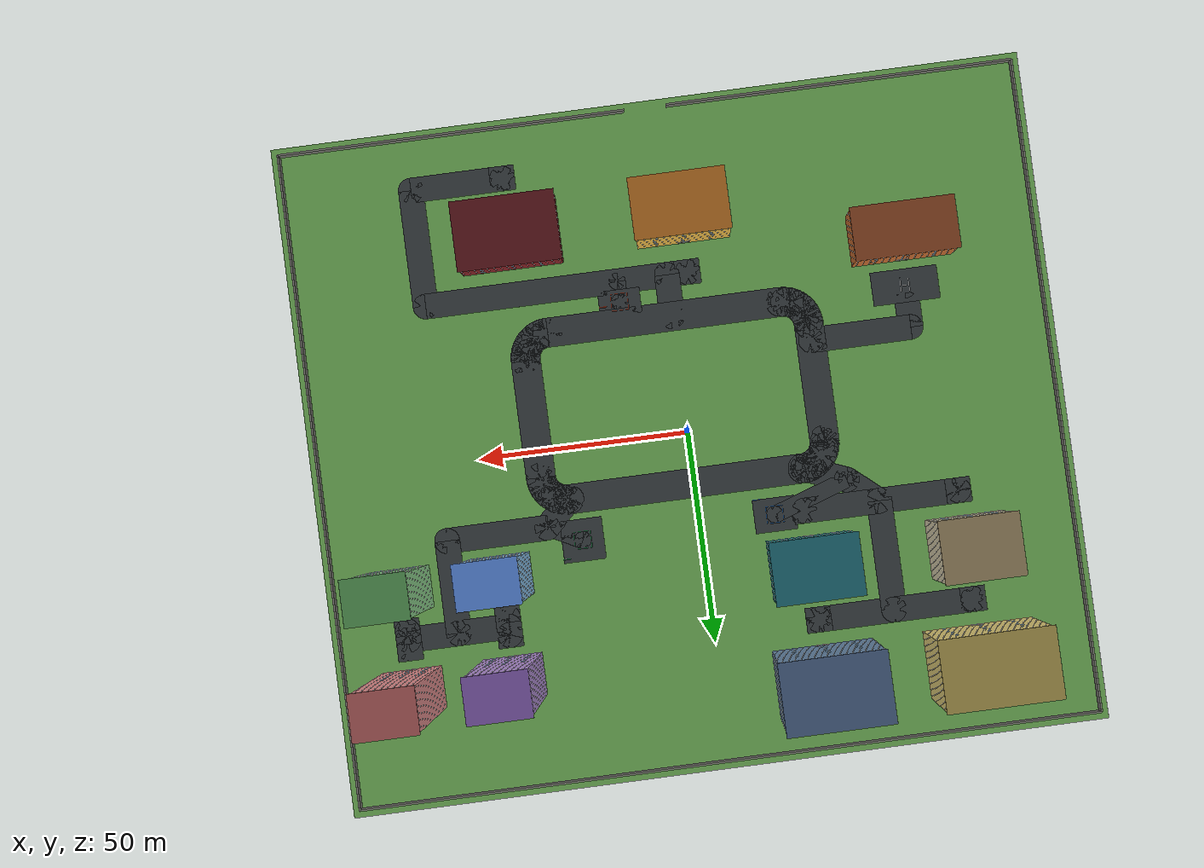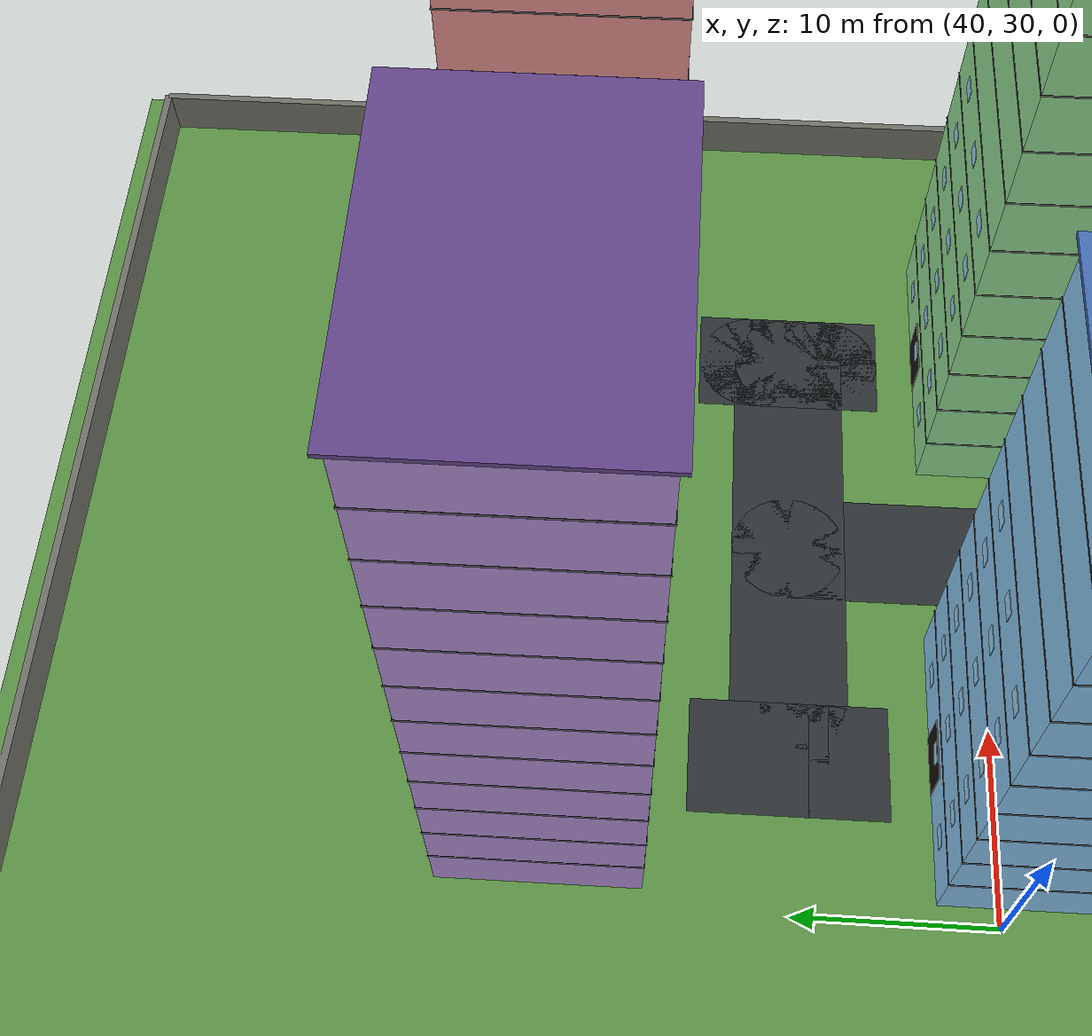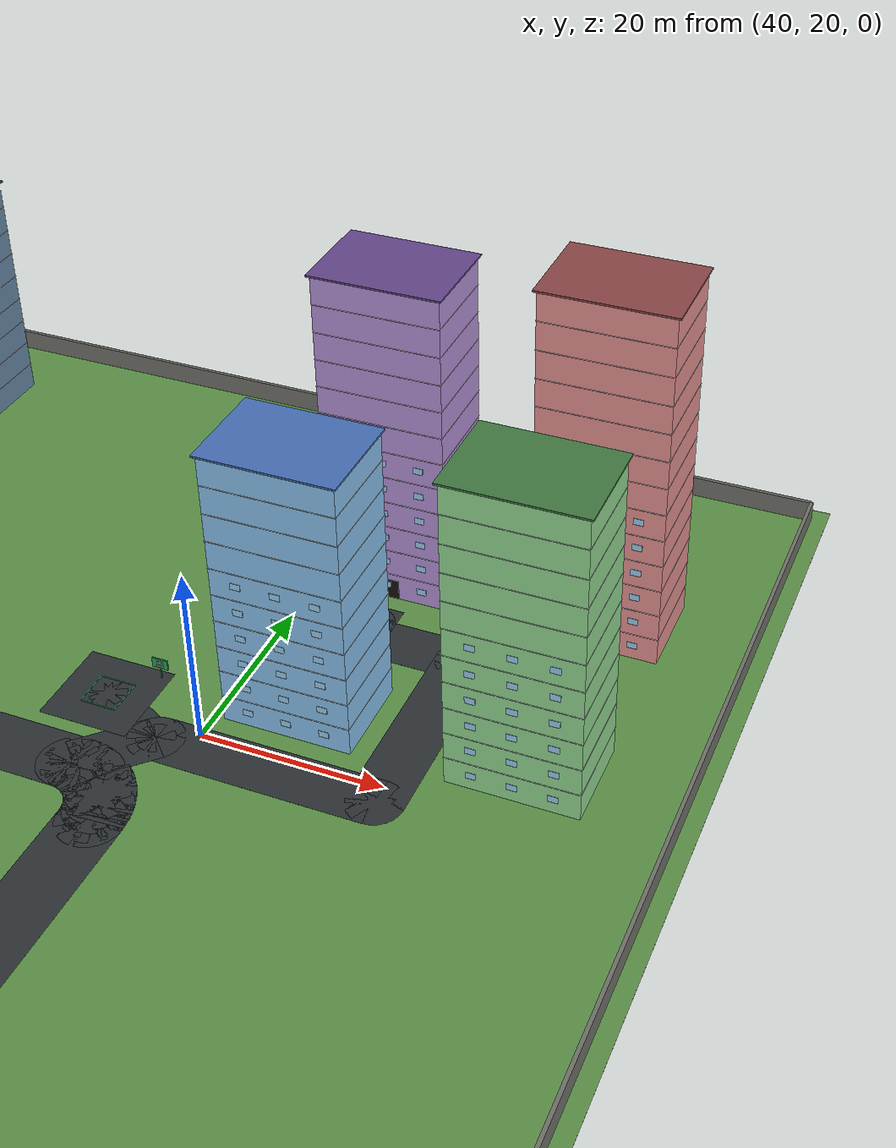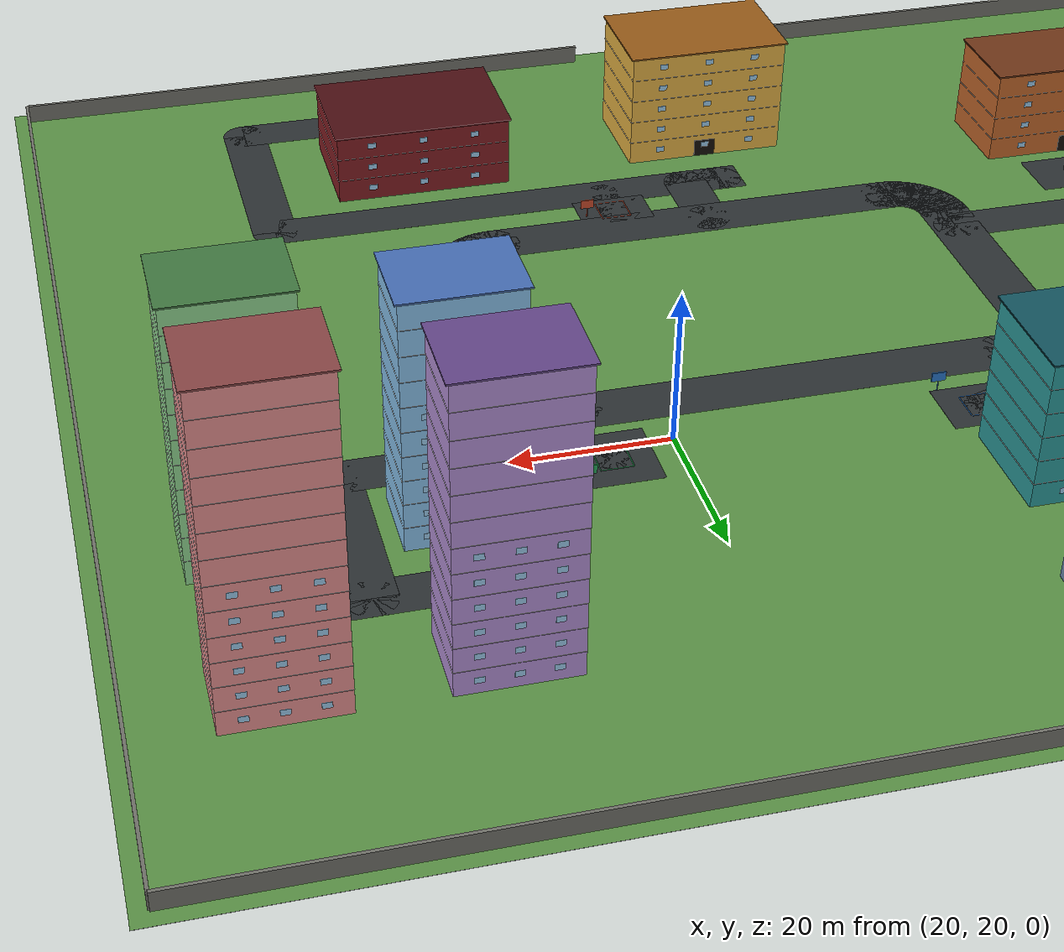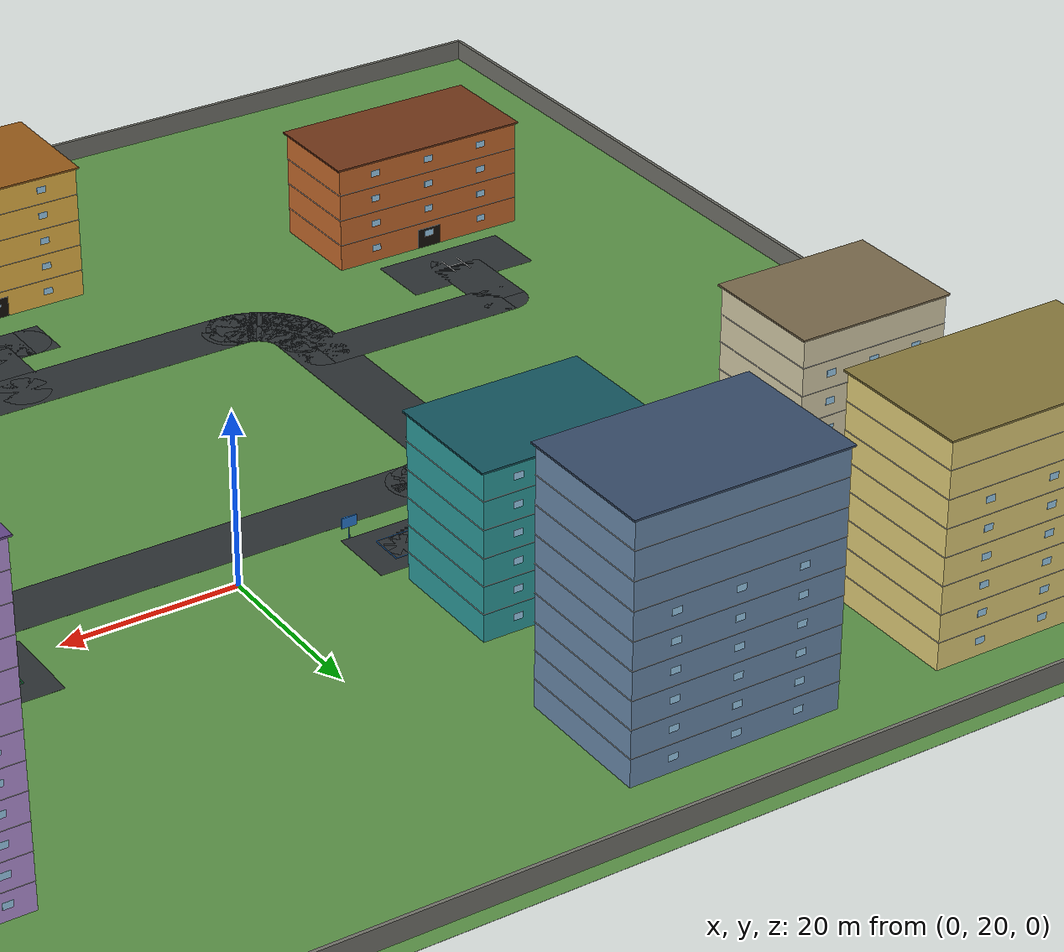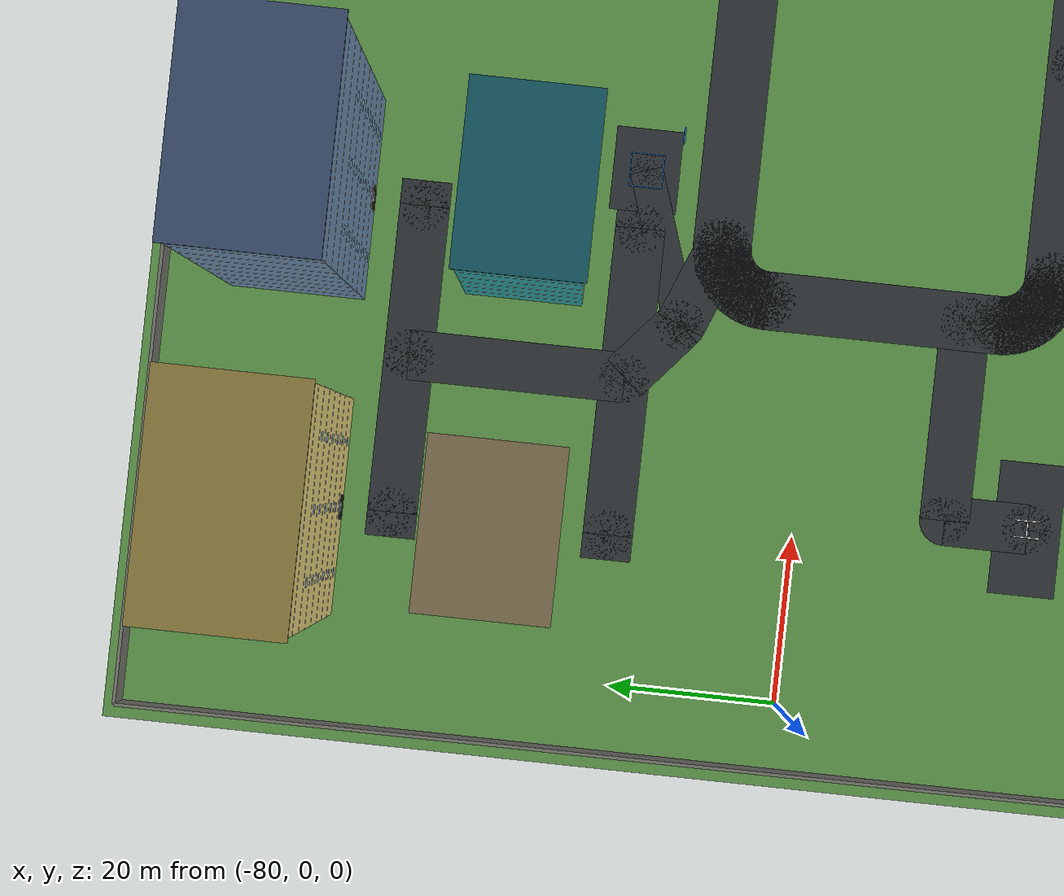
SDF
<sdf version="1.7">
  <world name="campus_regional">
    <physics name="default_physics" type="ode">
      <max_step_size>0.002</max_step_size>
      <real_time_update_rate>500</real_time_update_rate>
    </physics>
    <light name="sun" type="directional">
      <pose>0 0 80 0 0 0</pose>
      <cast_shadows>true</cast_shadows>
      <diffuse>0.9 0.9 0.85 1</diffuse>
      <specular>0.2 0.2 0.2 1</specular>
      <direction>-0.4 0.2 -1</direction>
    </light>
    <model name="campus_ground">
      <static>true</static>
      <link name="ground">
        <pose>0.000 0.000 -0.015 0 0 0</pose>
        <collision name="collision">
          <pose>0 0 0 0 0 0</pose>
          <geometry>
            <box>
              <size>180.000 160.000 0.030</size>
            </box>
          </geometry>
        </collision>
        <visual name="visual">
          <pose>0 0 0 0 0 0</pose>
          <geometry>
            <box>
              <size>180.000 160.000 0.030</size>
            </box>
          </geometry>
          <material>
            <ambient>0.360 0.580 0.280 1.000</ambient>
            <diffuse>0.360 0.580 0.280 1.000</diffuse>
          </material>
        </visual>
      </link>
    </model>
    <model name="campus_wall">
      <static>true</static>
      <link name="west_wall">
        <pose>-88.000 0.000 1.250 0 0 0</pose>
        <collision name="collision">
          <pose>0 0 0 0 0 0</pose>
          <geometry>
            <box>
              <size>0.400 156.000 2.500</size>
            </box>
          </geometry>
        </collision>
        <visual name="visual">
          <pose>0 0 0 0 0 0</pose>
          <geometry>
            <box>
              <size>0.400 156.000 2.500</size>
            </box>
          </geometry>
          <material>
            <ambient>0.450 0.450 0.420 1.000</ambient>
            <diffuse>0.450 0.450 0.420 1.000</diffuse>
          </material>
        </visual>
      </link>
      <link name="east_wall">
        <pose>88.000 0.000 1.250 0 0 0</pose>
        <collision name="collision">
          <pose>0 0 0 0 0 0</pose>
          <geometry>
            <box>
              <size>0.400 156.000 2.500</size>
            </box>
          </geometry>
        </collision>
        <visual name="visual">
          <pose>0 0 0 0 0 0</pose>
          <geometry>
            <box>
              <size>0.400 156.000 2.500</size>
            </box>
          </geometry>
          <material>
            <ambient>0.450 0.450 0.420 1.000</ambient>
            <diffuse>0.450 0.450 0.420 1.000</diffuse>
          </material>
        </visual>
      </link>
      <link name="north_wall">
        <pose>0.000 78.000 1.250 0 0 0</pose>
        <collision name="collision">
          <pose>0 0 0 0 0 0</pose>
          <geometry>
            <box>
              <size>176.000 0.400 2.500</size>
            </box>
          </geometry>
        </collision>
        <visual name="visual">
          <pose>0 0 0 0 0 0</pose>
          <geometry>
            <box>
              <size>176.000 0.400 2.500</size>
            </box>
          </geometry>
          <material>
            <ambient>0.450 0.450 0.420 1.000</ambient>
            <diffuse>0.450 0.450 0.420 1.000</diffuse>
          </material>
        </visual>
      </link>
      <link name="south_wall_west">
        <pose>-46.500 -78.000 1.250 0 0 0</pose>
        <collision name="collision">
          <pose>0 0 0 0 0 0</pose>
          <geometry>
            <box>
              <size>83.000 0.400 2.500</size>
            </box>
          </geometry>
        </collision>
        <visual name="visual">
          <pose>0 0 0 0 0 0</pose>
          <geometry>
            <box>
              <size>83.000 0.400 2.500</size>
            </box>
          </geometry>
          <material>
            <ambient>0.450 0.450 0.420 1.000</ambient>
            <diffuse>0.450 0.450 0.420 1.000</diffuse>
          </material>
        </visual>
      </link>
      <link name="south_wall_east">
        <pose>46.500 -78.000 1.250 0 0 0</pose>
        <collision name="collision">
          <pose>0 0 0 0 0 0</pose>
          <geometry>
            <box>
              <size>83.000 0.400 2.500</size>
            </box>
          </geometry>
        </collision>
        <visual name="visual">
          <pose>0 0 0 0 0 0</pose>
          <geometry>
            <box>
              <size>83.000 0.400 2.500</size>
            </box>
          </geometry>
          <material>
            <ambient>0.450 0.450 0.420 1.000</ambient>
            <diffuse>0.450 0.450 0.420 1.000</diffuse>
          </material>
        </visual>
      </link>
    </model>
    <model name="teaching_building">
      <static>true</static>
      <pose>-62.0 62.0 0 0 0 0</pose>
      <link name="body">
        <visual name="body">
          <pose>0 0 12.800 0 0 0</pose>
          <geometry>
            <box>
              <size>26.000 16.000 25.600</size>
            </box>
          </geometry>
          <material>
            <ambient>0.900 0.820 0.480 1.000</ambient>
            <diffuse>0.900 0.820 0.480 1.000</diffuse>
          </material>
        </visual>
        <collision name="body_collision">
          <pose>0 0 12.800 0 0 0</pose>
          <geometry>
            <box>
              <size>26.000 16.000 25.600</size>
            </box>
          </geometry>
        </collision>
        <visual name="roof">
          <pose>0 0 25.700 0 0 0</pose>
          <geometry>
            <box>
              <size>26.600 16.600 0.200</size>
            </box>
          </geometry>
          <material>
            <ambient>0.540 0.480 0.240 1.000</ambient>
            <diffuse>0.540 0.480 0.240 1.000</diffuse>
          </material>
        </visual>
        <visual name="floor_sep_n_1">
          <pose>0 8.018 3.200 0 0 0</pose>
          <geometry>
            <box>
              <size>26.100 0.035 0.060</size>
            </box>
          </geometry>
          <material>
            <ambient>0.080 0.080 0.080 1.000</ambient>
            <diffuse>0.080 0.080 0.080 1.000</diffuse>
          </material>
        </visual>
        <visual name="floor_sep_s_1">
          <pose>0 -8.018 3.200 0 0 0</pose>
          <geometry>
            <box>
              <size>26.100 0.035 0.060</size>
            </box>
          </geometry>
          <material>
            <ambient>0.080 0.080 0.080 1.000</ambient>
            <diffuse>0.080 0.080 0.080 1.000</diffuse>
          </material>
        </visual>
        <visual name="floor_sep_e_1">
          <pose>13.018 0 3.200 0 0 0</pose>
          <geometry>
            <box>
              <size>0.035 16.100 0.060</size>
            </box>
          </geometry>
          <material>
            <ambient>0.080 0.080 0.080 1.000</ambient>
            <diffuse>0.080 0.080 0.080 1.000</diffuse>
          </material>
        </visual>
        <visual name="floor_sep_w_1">
          <pose>-13.018 0 3.200 0 0 0</pose>
          <geometry>
            <box>
              <size>0.035 16.100 0.060</size>
            </box>
          </geometry>
          <material>
            <ambient>0.080 0.080 0.080 1.000</ambient>
            <diffuse>0.080 0.080 0.080 1.000</diffuse>
          </material>
        </visual>
        <visual name="floor_sep_n_2">
          <pose>0 8.018 6.400 0 0 0</pose>
          <geometry>
            <box>
              <size>26.100 0.035 0.060</size>
            </box>
          </geometry>
          <material>
            <ambient>0.080 0.080 0.080 1.000</ambient>
            <diffuse>0.080 0.080 0.080 1.000</diffuse>
          </material>
        </visual>
        <visual name="floor_sep_s_2">
          <pose>0 -8.018 6.400 0 0 0</pose>
          <geometry>
            <box>
              <size>26.100 0.035 0.060</size>
            </box>
          </geometry>
          <material>
            <ambient>0.080 0.080 0.080 1.000</ambient>
            <diffuse>0.080 0.080 0.080 1.000</diffuse>
          </material>
        </visual>
        <visual name="floor_sep_e_2">
          <pose>13.018 0 6.400 0 0 0</pose>
          <geometry>
            <box>
              <size>0.035 16.100 0.060</size>
            </box>
          </geometry>
          <material>
            <ambient>0.080 0.080 0.080 1.000</ambient>
            <diffuse>0.080 0.080 0.080 1.000</diffuse>
          </material>
        </visual>
        <visual name="floor_sep_w_2">
          <pose>-13.018 0 6.400 0 0 0</pose>
          <geometry>
            <box>
              <size>0.035 16.100 0.060</size>
            </box>
          </geometry>
          <material>
            <ambient>0.080 0.080 0.080 1.000</ambient>
            <diffuse>0.080 0.080 0.080 1.000</diffuse>
          </material>
        </visual>
        <visual name="floor_sep_n_3">
          <pose>0 8.018 9.600 0 0 0</pose>
          <geometry>
            <box>
              <size>26.100 0.035 0.060</size>
            </box>
          </geometry>
          <material>
            <ambient>0.080 0.080 0.080 1.000</ambient>
            <diffuse>0.080 0.080 0.080 1.000</diffuse>
          </material>
        </visual>
        <visual name="floor_sep_s_3">
          <pose>0 -8.018 9.600 0 0 0</pose>
          <geometry>
            <box>
              <size>26.100 0.035 0.060</size>
            </box>
          </geometry>
          <material>
            <ambient>0.080 0.080 0.080 1.000</ambient>
            <diffuse>0.080 0.080 0.080 1.000</diffuse>
          </material>
        </visual>
        <visual name="floor_sep_e_3">
          <pose>13.018 0 9.600 0 0 0</pose>
          <geometry>
            <box>
              <size>0.035 16.100 0.060</size>
            </box>
          </geometry>
          <material>
            <ambient>0.080 0.080 0.080 1.000</ambient>
            <diffuse>0.080 0.080 0.080 1.000</diffuse>
          </material>
        </visual>
        <visual name="floor_sep_w_3">
          <pose>-13.018 0 9.600 0 0 0</pose>
          <geometry>
            <box>
              <size>0.035 16.100 0.060</size>
            </box>
          </geometry>
          <material>
            <ambient>0.080 0.080 0.080 1.000</ambient>
            <diffuse>0.080 0.080 0.080 1.000</diffuse>
          </material>
        </visual>
        <visual name="floor_sep_n_4">
          <pose>0 8.018 12.800 0 0 0</pose>
          <geometry>
            <box>
              <size>26.100 0.035 0.060</size>
            </box>
          </geometry>
          <material>
            <ambient>0.080 0.080 0.080 1.000</ambient>
            <diffuse>0.080 0.080 0.080 1.000</diffuse>
          </material>
        </visual>
        <visual name="floor_sep_s_4">
          <pose>0 -8.018 12.800 0 0 0</pose>
          <geometry>
            <box>
              <size>26.100 0.035 0.060</size>
            </box>
          </geometry>
          <material>
            <ambient>0.080 0.080 0.080 1.000</ambient>
            <diffuse>0.080 0.080 0.080 1.000</diffuse>
          </material>
        </visual>
        <visual name="floor_sep_e_4">
          <pose>13.018 0 12.800 0 0 0</pose>
          <geometry>
            <box>
              <size>0.035 16.100 0.060</size>
            </box>
          </geometry>
          <material>
            <ambient>0.080 0.080 0.080 1.000</ambient>
            <diffuse>0.080 0.080 0.080 1.000</diffuse>
          </material>
        </visual>
        <visual name="floor_sep_w_4">
          <pose>-13.018 0 12.800 0 0 0</pose>
          <geometry>
            <box>
              <size>0.035 16.100 0.060</size>
            </box>
          </geometry>
          <material>
            <ambient>0.080 0.080 0.080 1.000</ambient>
            <diffuse>0.080 0.080 0.080 1.000</diffuse>
          </material>
        </visual>
        <visual name="floor_sep_n_5">
          <pose>0 8.018 16.000 0 0 0</pose>
          <geometry>
            <box>
              <size>26.100 0.035 0.060</size>
            </box>
          </geometry>
          <material>
            <ambient>0.080 0.080 0.080 1.000</ambient>
            <diffuse>0.080 0.080 0.080 1.000</diffuse>
          </material>
        </visual>
        <visual name="floor_sep_s_5">
          <pose>0 -8.018 16.000 0 0 0</pose>
          <geometry>
            <box>
              <size>26.100 0.035 0.060</size>
            </box>
          </geometry>
          <material>
            <ambient>0.080 0.080 0.080 1.000</ambient>
            <diffuse>0.080 0.080 0.080 1.000</diffuse>
          </material>
        </visual>
        <visual name="floor_sep_e_5">
          <pose>13.018 0 16.000 0 0 0</pose>
          <geometry>
            <box>
              <size>0.035 16.100 0.060</size>
            </box>
          </geometry>
          <material>
            <ambient>0.080 0.080 0.080 1.000</ambient>
            <diffuse>0.080 0.080 0.080 1.000</diffuse>
          </material>
        </visual>
        <visual name="floor_sep_w_5">
          <pose>-13.018 0 16.000 0 0 0</pose>
          <geometry>
            <box>
              <size>0.035 16.100 0.060</size>
            </box>
          </geometry>
          <material>
            <ambient>0.080 0.080 0.080 1.000</ambient>
            <diffuse>0.080 0.080 0.080 1.000</diffuse>
          </material>
        </visual>
        <visual name="floor_sep_n_6">
          <pose>0 8.018 19.200 0 0 0</pose>
          <geometry>
            <box>
              <size>26.100 0.035 0.060</size>
            </box>
          </geometry>
          <material>
            <ambient>0.080 0.080 0.080 1.000</ambient>
            <diffuse>0.080 0.080 0.080 1.000</diffuse>
          </material>
        </visual>
        <visual name="floor_sep_s_6">
          <pose>0 -8.018 19.200 0 0 0</pose>
          <geometry>
            <box>
              <size>26.100 0.035 0.060</size>
            </box>
          </geometry>
          <material>
            <ambient>0.080 0.080 0.080 1.000</ambient>
            <diffuse>0.080 0.080 0.080 1.000</diffuse>
          </material>
        </visual>
        <visual name="floor_sep_e_6">
          <pose>13.018 0 19.200 0 0 0</pose>
          <geometry>
            <box>
              <size>0.035 16.100 0.060</size>
            </box>
          </geometry>
          <material>
            <ambient>0.080 0.080 0.080 1.000</ambient>
            <diffuse>0.080 0.080 0.080 1.000</diffuse>
          </material>
        </visual>
        <visual name="floor_sep_w_6">
          <pose>-13.018 0 19.200 0 0 0</pose>
          <geometry>
            <box>
              <size>0.035 16.100 0.060</size>
            </box>
          </geometry>
          <material>
            <ambient>0.080 0.080 0.080 1.000</ambient>
            <diffuse>0.080 0.080 0.080 1.000</diffuse>
          </material>
        </visual>
        <visual name="floor_sep_n_7">
          <pose>0 8.018 22.400 0 0 0</pose>
          <geometry>
            <box>
              <size>26.100 0.035 0.060</size>
            </box>
          </geometry>
          <material>
            <ambient>0.080 0.080 0.080 1.000</ambient>
            <diffuse>0.080 0.080 0.080 1.000</diffuse>
          </material>
        </visual>
        <visual name="floor_sep_s_7">
          <pose>0 -8.018 22.400 0 0 0</pose>
          <geometry>
            <box>
              <size>26.100 0.035 0.060</size>
            </box>
          </geometry>
          <material>
            <ambient>0.080 0.080 0.080 1.000</ambient>
            <diffuse>0.080 0.080 0.080 1.000</diffuse>
          </material>
        </visual>
        <visual name="floor_sep_e_7">
          <pose>13.018 0 22.400 0 0 0</pose>
          <geometry>
            <box>
              <size>0.035 16.100 0.060</size>
            </box>
          </geometry>
          <material>
            <ambient>0.080 0.080 0.080 1.000</ambient>
            <diffuse>0.080 0.080 0.080 1.000</diffuse>
          </material>
        </visual>
        <visual name="floor_sep_w_7">
          <pose>-13.018 0 22.400 0 0 0</pose>
          <geometry>
            <box>
              <size>0.035 16.100 0.060</size>
            </box>
          </geometry>
          <material>
            <ambient>0.080 0.080 0.080 1.000</ambient>
            <diffuse>0.080 0.080 0.080 1.000</diffuse>
          </material>
        </visual>
        <visual name="front_door">
          <pose>0 -8.012 1.2 0 0 0</pose>
          <geometry>
            <box>
              <size>3.000 0.050 2.400</size>
            </box>
          </geometry>
          <material>
            <ambient>0.080 0.060 0.040 1.000</ambient>
            <diffuse>0.080 0.060 0.040 1.000</diffuse>
          </material>
        </visual>
        <visual name="win_n_1_-7.8">
          <pose>-7.800 8.020 1.700 0 0 0</pose>
          <geometry>
            <box>
              <size>1.100 0.035 0.750</size>
            </box>
          </geometry>
          <material>
            <ambient>0.620 0.820 0.950 1.000</ambient>
            <diffuse>0.620 0.820 0.950 1.000</diffuse>
          </material>
        </visual>
        <visual name="win_s_1_-7.8">
          <pose>-7.800 -8.020 1.700 0 0 0</pose>
          <geometry>
            <box>
              <size>1.100 0.035 0.750</size>
            </box>
          </geometry>
          <material>
            <ambient>0.620 0.820 0.950 1.000</ambient>
            <diffuse>0.620 0.820 0.950 1.000</diffuse>
          </material>
        </visual>
        <visual name="win_n_1_0.0">
          <pose>0.000 8.020 1.700 0 0 0</pose>
          <geometry>
            <box>
              <size>1.100 0.035 0.750</size>
            </box>
          </geometry>
          <material>
            <ambient>0.620 0.820 0.950 1.000</ambient>
            <diffuse>0.620 0.820 0.950 1.000</diffuse>
          </material>
        </visual>
        <visual name="win_s_1_0.0">
          <pose>0.000 -8.020 1.700 0 0 0</pose>
          <geometry>
            <box>
              <size>1.100 0.035 0.750</size>
            </box>
          </geometry>
          <material>
            <ambient>0.620 0.820 0.950 1.000</ambient>
            <diffuse>0.620 0.820 0.950 1.000</diffuse>
          </material>
        </visual>
        <visual name="win_n_1_7.8">
          <pose>7.800 8.020 1.700 0 0 0</pose>
          <geometry>
            <box>
              <size>1.100 0.035 0.750</size>
            </box>
          </geometry>
          <material>
            <ambient>0.620 0.820 0.950 1.000</ambient>
            <diffuse>0.620 0.820 0.950 1.000</diffuse>
          </material>
        </visual>
        <visual name="win_s_1_7.8">
          <pose>7.800 -8.020 1.700 0 0 0</pose>
          <geometry>
            <box>
              <size>1.100 0.035 0.750</size>
            </box>
          </geometry>
          <material>
            <ambient>0.620 0.820 0.950 1.000</ambient>
            <diffuse>0.620 0.820 0.950 1.000</diffuse>
          </material>
        </visual>
        <visual name="win_n_2_-7.8">
          <pose>-7.800 8.020 4.900 0 0 0</pose>
          <geometry>
            <box>
              <size>1.100 0.035 0.750</size>
            </box>
          </geometry>
          <material>
            <ambient>0.620 0.820 0.950 1.000</ambient>
            <diffuse>0.620 0.820 0.950 1.000</diffuse>
          </material>
        </visual>
        <visual name="win_s_2_-7.8">
          <pose>-7.800 -8.020 4.900 0 0 0</pose>
          <geometry>
            <box>
              <size>1.100 0.035 0.750</size>
            </box>
          </geometry>
          <material>
            <ambient>0.620 0.820 0.950 1.000</ambient>
            <diffuse>0.620 0.820 0.950 1.000</diffuse>
          </material>
        </visual>
        <visual name="win_n_2_0.0">
          <pose>0.000 8.020 4.900 0 0 0</pose>
          <geometry>
            <box>
              <size>1.100 0.035 0.750</size>
            </box>
          </geometry>
          <material>
            <ambient>0.620 0.820 0.950 1.000</ambient>
            <diffuse>0.620 0.820 0.950 1.000</diffuse>
          </material>
        </visual>
        <visual name="win_s_2_0.0">
          <pose>0.000 -8.020 4.900 0 0 0</pose>
          <geometry>
            <box>
              <size>1.100 0.035 0.750</size>
            </box>
          </geometry>
          <material>
            <ambient>0.620 0.820 0.950 1.000</ambient>
            <diffuse>0.620 0.820 0.950 1.000</diffuse>
          </material>
        </visual>
        <visual name="win_n_2_7.8">
          <pose>7.800 8.020 4.900 0 0 0</pose>
          <geometry>
            <box>
              <size>1.100 0.035 0.750</size>
            </box>
          </geometry>
          <material>
            <ambient>0.620 0.820 0.950 1.000</ambient>
            <diffuse>0.620 0.820 0.950 1.000</diffuse>
          </material>
        </visual>
        <visual name="win_s_2_7.8">
          <pose>7.800 -8.020 4.900 0 0 0</pose>
          <geometry>
            <box>
              <size>1.100 0.035 0.750</size>
            </box>
          </geometry>
          <material>
            <ambient>0.620 0.820 0.950 1.000</ambient>
            <diffuse>0.620 0.820 0.950 1.000</diffuse>
          </material>
        </visual>
        <visual name="win_n_3_-7.8">
          <pose>-7.800 8.020 8.100 0 0 0</pose>
          <geometry>
            <box>
              <size>1.100 0.035 0.750</size>
            </box>
          </geometry>
          <material>
            <ambient>0.620 0.820 0.950 1.000</ambient>
            <diffuse>0.620 0.820 0.950 1.000</diffuse>
          </material>
        </visual>
        <visual name="win_s_3_-7.8">
          <pose>-7.800 -8.020 8.100 0 0 0</pose>
          <geometry>
            <box>
              <size>1.100 0.035 0.750</size>
            </box>
          </geometry>
          <material>
            <ambient>0.620 0.820 0.950 1.000</ambient>
            <diffuse>0.620 0.820 0.950 1.000</diffuse>
          </material>
        </visual>
        <visual name="win_n_3_0.0">
          <pose>0.000 8.020 8.100 0 0 0</pose>
          <geometry>
            <box>
              <size>1.100 0.035 0.750</size>
            </box>
          </geometry>
          <material>
            <ambient>0.620 0.820 0.950 1.000</ambient>
            <diffuse>0.620 0.820 0.950 1.000</diffuse>
          </material>
        </visual>
        <visual name="win_s_3_0.0">
          <pose>0.000 -8.020 8.100 0 0 0</pose>
          <geometry>
            <box>
              <size>1.100 0.035 0.750</size>
            </box>
          </geometry>
          <material>
            <ambient>0.620 0.820 0.950 1.000</ambient>
            <diffuse>0.620 0.820 0.950 1.000</diffuse>
          </material>
        </visual>
        <visual name="win_n_3_7.8">
          <pose>7.800 8.020 8.100 0 0 0</pose>
          <geometry>
            <box>
              <size>1.100 0.035 0.750</size>
            </box>
          </geometry>
          <material>
            <ambient>0.620 0.820 0.950 1.000</ambient>
            <diffuse>0.620 0.820 0.950 1.000</diffuse>
          </material>
        </visual>
        <visual name="win_s_3_7.8">
          <pose>7.800 -8.020 8.100 0 0 0</pose>
          <geometry>
            <box>
              <size>1.100 0.035 0.750</size>
            </box>
          </geometry>
          <material>
            <ambient>0.620 0.820 0.950 1.000</ambient>
            <diffuse>0.620 0.820 0.950 1.000</diffuse>
          </material>
        </visual>
        <visual name="win_n_4_-7.8">
          <pose>-7.800 8.020 11.300 0 0 0</pose>
          <geometry>
            <box>
              <size>1.100 0.035 0.750</size>
            </box>
          </geometry>
          <material>
            <ambient>0.620 0.820 0.950 1.000</ambient>
            <diffuse>0.620 0.820 0.950 1.000</diffuse>
          </material>
        </visual>
        <visual name="win_s_4_-7.8">
          <pose>-7.800 -8.020 11.300 0 0 0</pose>
          <geometry>
            <box>
              <size>1.100 0.035 0.750</size>
            </box>
          </geometry>
          <material>
            <ambient>0.620 0.820 0.950 1.000</ambient>
            <diffuse>0.620 0.820 0.950 1.000</diffuse>
          </material>
        </visual>
        <visual name="win_n_4_0.0">
          <pose>0.000 8.020 11.300 0 0 0</pose>
          <geometry>
            <box>
              <size>1.100 0.035 0.750</size>
            </box>
          </geometry>
          <material>
            <ambient>0.620 0.820 0.950 1.000</ambient>
            <diffuse>0.620 0.820 0.950 1.000</diffuse>
          </material>
        </visual>
        <visual name="win_s_4_0.0">
          <pose>0.000 -8.020 11.300 0 0 0</pose>
          <geometry>
            <box>
              <size>1.100 0.035 0.750</size>
            </box>
          </geometry>
          <material>
            <ambient>0.620 0.820 0.950 1.000</ambient>
            <diffuse>0.620 0.820 0.950 1.000</diffuse>
          </material>
        </visual>
        <visual name="win_n_4_7.8">
          <pose>7.800 8.020 11.300 0 0 0</pose>
          <geometry>
            <box>
              <size>1.100 0.035 0.750</size>
            </box>
          </geometry>
          <material>
            <ambient>0.620 0.820 0.950 1.000</ambient>
            <diffuse>0.620 0.820 0.950 1.000</diffuse>
          </material>
        </visual>
        <visual name="win_s_4_7.8">
          <pose>7.800 -8.020 11.300 0 0 0</pose>
          <geometry>
            <box>
              <size>1.100 0.035 0.750</size>
            </box>
          </geometry>
          <material>
            <ambient>0.620 0.820 0.950 1.000</ambient>
            <diffuse>0.620 0.820 0.950 1.000</diffuse>
          </material>
        </visual>
        <visual name="win_n_5_-7.8">
          <pose>-7.800 8.020 14.500 0 0 0</pose>
          <geometry>
            <box>
              <size>1.100 0.035 0.750</size>
            </box>
          </geometry>
          <material>
            <ambient>0.620 0.820 0.950 1.000</ambient>
            <diffuse>0.620 0.820 0.950 1.000</diffuse>
          </material>
        </visual>
        <visual name="win_s_5_-7.8">
          <pose>-7.800 -8.020 14.500 0 0 0</pose>
          <geometry>
            <box>
              <size>1.100 0.035 0.750</size>
            </box>
          </geometry>
          <material>
            <ambient>0.620 0.820 0.950 1.000</ambient>
            <diffuse>0.620 0.820 0.950 1.000</diffuse>
          </material>
        </visual>
        <visual name="win_n_5_0.0">
          <pose>0.000 8.020 14.500 0 0 0</pose>
          <geometry>
            <box>
              <size>1.100 0.035 0.750</size>
            </box>
          </geometry>
          <material>
            <ambient>0.620 0.820 0.950 1.000</ambient>
            <diffuse>0.620 0.820 0.950 1.000</diffuse>
          </material>
        </visual>
        <visual name="win_s_5_0.0">
          <pose>0.000 -8.020 14.500 0 0 0</pose>
          <geometry>
            <box>
              <size>1.100 0.035 0.750</size>
            </box>
          </geometry>
          <material>
            <ambient>0.620 0.820 0.950 1.000</ambient>
            <diffuse>0.620 0.820 0.950 1.000</diffuse>
          </material>
        </visual>
        <visual name="win_n_5_7.8">
          <pose>7.800 8.020 14.500 0 0 0</pose>
          <geometry>
            <box>
              <size>1.100 0.035 0.750</size>
            </box>
          </geometry>
          <material>
            <ambient>0.620 0.820 0.950 1.000</ambient>
            <diffuse>0.620 0.820 0.950 1.000</diffuse>
          </material>
        </visual>
        <visual name="win_s_5_7.8">
          <pose>7.800 -8.020 14.500 0 0 0</pose>
          <geometry>
            <box>
              <size>1.100 0.035 0.750</size>
            </box>
          </geometry>
          <material>
            <ambient>0.620 0.820 0.950 1.000</ambient>
            <diffuse>0.620 0.820 0.950 1.000</diffuse>
          </material>
        </visual>
        <visual name="win_n_6_-7.8">
          <pose>-7.800 8.020 17.700 0 0 0</pose>
          <geometry>
            <box>
              <size>1.100 0.035 0.750</size>
            </box>
          </geometry>
          <material>
            <ambient>0.620 0.820 0.950 1.000</ambient>
            <diffuse>0.620 0.820 0.950 1.000</diffuse>
          </material>
        </visual>
        <visual name="win_s_6_-7.8">
          <pose>-7.800 -8.020 17.700 0 0 0</pose>
          <geometry>
            <box>
              <size>1.100 0.035 0.750</size>
            </box>
          </geometry>
          <material>
            <ambient>0.620 0.820 0.950 1.000</ambient>
            <diffuse>0.620 0.820 0.950 1.000</diffuse>
          </material>
        </visual>
        <visual name="win_n_6_0.0">
          <pose>0.000 8.020 17.700 0 0 0</pose>
          <geometry>
            <box>
              <size>1.100 0.035 0.750</size>
            </box>
          </geometry>
          <material>
            <ambient>0.620 0.820 0.950 1.000</ambient>
            <diffuse>0.620 0.820 0.950 1.000</diffuse>
          </material>
        </visual>
        <visual name="win_s_6_0.0">
          <pose>0.000 -8.020 17.700 0 0 0</pose>
          <geometry>
            <box>
              <size>1.100 0.035 0.750</size>
            </box>
          </geometry>
          <material>
            <ambient>0.620 0.820 0.950 1.000</ambient>
            <diffuse>0.620 0.820 0.950 1.000</diffuse>
          </material>
        </visual>
        <visual name="win_n_6_7.8">
          <pose>7.800 8.020 17.700 0 0 0</pose>
          <geometry>
            <box>
              <size>1.100 0.035 0.750</size>
            </box>
          </geometry>
          <material>
            <ambient>0.620 0.820 0.950 1.000</ambient>
            <diffuse>0.620 0.820 0.950 1.000</diffuse>
          </material>
        </visual>
        <visual name="win_s_6_7.8">
          <pose>7.800 -8.020 17.700 0 0 0</pose>
          <geometry>
            <box>
              <size>1.100 0.035 0.750</size>
            </box>
          </geometry>
          <material>
            <ambient>0.620 0.820 0.950 1.000</ambient>
            <diffuse>0.620 0.820 0.950 1.000</diffuse>
          </material>
        </visual>
      </link>
    </model>
    <model name="library">
      <static>true</static>
      <pose>-62.0 35.0 0 0 0 0</pose>
      <link name="body">
        <visual name="body">
          <pose>0 0 11.200 0 0 0</pose>
          <geometry>
            <box>
              <size>18.000 14.000 22.400</size>
            </box>
          </geometry>
          <material>
            <ambient>0.860 0.820 0.680 1.000</ambient>
            <diffuse>0.860 0.820 0.680 1.000</diffuse>
          </material>
        </visual>
        <collision name="body_collision">
          <pose>0 0 11.200 0 0 0</pose>
          <geometry>
            <box>
              <size>18.000 14.000 22.400</size>
            </box>
          </geometry>
        </collision>
        <visual name="roof">
          <pose>0 0 22.500 0 0 0</pose>
          <geometry>
            <box>
              <size>18.600 14.600 0.200</size>
            </box>
          </geometry>
          <material>
            <ambient>0.480 0.420 0.300 1.000</ambient>
            <diffuse>0.480 0.420 0.300 1.000</diffuse>
          </material>
        </visual>
        <visual name="floor_sep_n_1">
          <pose>0 7.018 3.200 0 0 0</pose>
          <geometry>
            <box>
              <size>18.100 0.035 0.060</size>
            </box>
          </geometry>
          <material>
            <ambient>0.080 0.080 0.080 1.000</ambient>
            <diffuse>0.080 0.080 0.080 1.000</diffuse>
          </material>
        </visual>
        <visual name="floor_sep_s_1">
          <pose>0 -7.018 3.200 0 0 0</pose>
          <geometry>
            <box>
              <size>18.100 0.035 0.060</size>
            </box>
          </geometry>
          <material>
            <ambient>0.080 0.080 0.080 1.000</ambient>
            <diffuse>0.080 0.080 0.080 1.000</diffuse>
          </material>
        </visual>
        <visual name="floor_sep_e_1">
          <pose>9.018 0 3.200 0 0 0</pose>
          <geometry>
            <box>
              <size>0.035 14.100 0.060</size>
            </box>
          </geometry>
          <material>
            <ambient>0.080 0.080 0.080 1.000</ambient>
            <diffuse>0.080 0.080 0.080 1.000</diffuse>
          </material>
        </visual>
        <visual name="floor_sep_w_1">
          <pose>-9.018 0 3.200 0 0 0</pose>
          <geometry>
            <box>
              <size>0.035 14.100 0.060</size>
            </box>
          </geometry>
          <material>
            <ambient>0.080 0.080 0.080 1.000</ambient>
            <diffuse>0.080 0.080 0.080 1.000</diffuse>
          </material>
        </visual>
        <visual name="floor_sep_n_2">
          <pose>0 7.018 6.400 0 0 0</pose>
          <geometry>
            <box>
              <size>18.100 0.035 0.060</size>
            </box>
          </geometry>
          <material>
            <ambient>0.080 0.080 0.080 1.000</ambient>
            <diffuse>0.080 0.080 0.080 1.000</diffuse>
          </material>
        </visual>
        <visual name="floor_sep_s_2">
          <pose>0 -7.018 6.400 0 0 0</pose>
          <geometry>
            <box>
              <size>18.100 0.035 0.060</size>
            </box>
          </geometry>
          <material>
            <ambient>0.080 0.080 0.080 1.000</ambient>
            <diffuse>0.080 0.080 0.080 1.000</diffuse>
          </material>
        </visual>
        <visual name="floor_sep_e_2">
          <pose>9.018 0 6.400 0 0 0</pose>
          <geometry>
            <box>
              <size>0.035 14.100 0.060</size>
            </box>
          </geometry>
          <material>
            <ambient>0.080 0.080 0.080 1.000</ambient>
            <diffuse>0.080 0.080 0.080 1.000</diffuse>
          </material>
        </visual>
        <visual name="floor_sep_w_2">
          <pose>-9.018 0 6.400 0 0 0</pose>
          <geometry>
            <box>
              <size>0.035 14.100 0.060</size>
            </box>
          </geometry>
          <material>
            <ambient>0.080 0.080 0.080 1.000</ambient>
            <diffuse>0.080 0.080 0.080 1.000</diffuse>
          </material>
        </visual>
        <visual name="floor_sep_n_3">
          <pose>0 7.018 9.600 0 0 0</pose>
          <geometry>
            <box>
              <size>18.100 0.035 0.060</size>
            </box>
          </geometry>
          <material>
            <ambient>0.080 0.080 0.080 1.000</ambient>
            <diffuse>0.080 0.080 0.080 1.000</diffuse>
          </material>
        </visual>
        <visual name="floor_sep_s_3">
          <pose>0 -7.018 9.600 0 0 0</pose>
          <geometry>
            <box>
              <size>18.100 0.035 0.060</size>
            </box>
          </geometry>
          <material>
            <ambient>0.080 0.080 0.080 1.000</ambient>
            <diffuse>0.080 0.080 0.080 1.000</diffuse>
          </material>
        </visual>
        <visual name="floor_sep_e_3">
          <pose>9.018 0 9.600 0 0 0</pose>
          <geometry>
            <box>
              <size>0.035 14.100 0.060</size>
            </box>
          </geometry>
          <material>
            <ambient>0.080 0.080 0.080 1.000</ambient>
            <diffuse>0.080 0.080 0.080 1.000</diffuse>
          </material>
        </visual>
        <visual name="floor_sep_w_3">
          <pose>-9.018 0 9.600 0 0 0</pose>
          <geometry>
            <box>
              <size>0.035 14.100 0.060</size>
            </box>
          </geometry>
          <material>
            <ambient>0.080 0.080 0.080 1.000</ambient>
            <diffuse>0.080 0.080 0.080 1.000</diffuse>
          </material>
        </visual>
        <visual name="floor_sep_n_4">
          <pose>0 7.018 12.800 0 0 0</pose>
          <geometry>
            <box>
              <size>18.100 0.035 0.060</size>
            </box>
          </geometry>
          <material>
            <ambient>0.080 0.080 0.080 1.000</ambient>
            <diffuse>0.080 0.080 0.080 1.000</diffuse>
          </material>
        </visual>
        <visual name="floor_sep_s_4">
          <pose>0 -7.018 12.800 0 0 0</pose>
          <geometry>
            <box>
              <size>18.100 0.035 0.060</size>
            </box>
          </geometry>
          <material>
            <ambient>0.080 0.080 0.080 1.000</ambient>
            <diffuse>0.080 0.080 0.080 1.000</diffuse>
          </material>
        </visual>
        <visual name="floor_sep_e_4">
          <pose>9.018 0 12.800 0 0 0</pose>
          <geometry>
            <box>
              <size>0.035 14.100 0.060</size>
            </box>
          </geometry>
          <material>
            <ambient>0.080 0.080 0.080 1.000</ambient>
            <diffuse>0.080 0.080 0.080 1.000</diffuse>
          </material>
        </visual>
        <visual name="floor_sep_w_4">
          <pose>-9.018 0 12.800 0 0 0</pose>
          <geometry>
            <box>
              <size>0.035 14.100 0.060</size>
            </box>
          </geometry>
          <material>
            <ambient>0.080 0.080 0.080 1.000</ambient>
            <diffuse>0.080 0.080 0.080 1.000</diffuse>
          </material>
        </visual>
        <visual name="floor_sep_n_5">
          <pose>0 7.018 16.000 0 0 0</pose>
          <geometry>
            <box>
              <size>18.100 0.035 0.060</size>
            </box>
          </geometry>
          <material>
            <ambient>0.080 0.080 0.080 1.000</ambient>
            <diffuse>0.080 0.080 0.080 1.000</diffuse>
          </material>
        </visual>
        <visual name="floor_sep_s_5">
          <pose>0 -7.018 16.000 0 0 0</pose>
          <geometry>
            <box>
              <size>18.100 0.035 0.060</size>
            </box>
          </geometry>
          <material>
            <ambient>0.080 0.080 0.080 1.000</ambient>
            <diffuse>0.080 0.080 0.080 1.000</diffuse>
          </material>
        </visual>
        <visual name="floor_sep_e_5">
          <pose>9.018 0 16.000 0 0 0</pose>
          <geometry>
            <box>
              <size>0.035 14.100 0.060</size>
            </box>
          </geometry>
          <material>
            <ambient>0.080 0.080 0.080 1.000</ambient>
            <diffuse>0.080 0.080 0.080 1.000</diffuse>
          </material>
        </visual>
        <visual name="floor_sep_w_5">
          <pose>-9.018 0 16.000 0 0 0</pose>
          <geometry>
            <box>
              <size>0.035 14.100 0.060</size>
            </box>
          </geometry>
          <material>
            <ambient>0.080 0.080 0.080 1.000</ambient>
            <diffuse>0.080 0.080 0.080 1.000</diffuse>
          </material>
        </visual>
        <visual name="floor_sep_n_6">
          <pose>0 7.018 19.200 0 0 0</pose>
          <geometry>
            <box>
              <size>18.100 0.035 0.060</size>
            </box>
          </geometry>
          <material>
            <ambient>0.080 0.080 0.080 1.000</ambient>
            <diffuse>0.080 0.080 0.080 1.000</diffuse>
          </material>
        </visual>
        <visual name="floor_sep_s_6">
          <pose>0 -7.018 19.200 0 0 0</pose>
          <geometry>
            <box>
              <size>18.100 0.035 0.060</size>
            </box>
          </geometry>
          <material>
            <ambient>0.080 0.080 0.080 1.000</ambient>
            <diffuse>0.080 0.080 0.080 1.000</diffuse>
          </material>
        </visual>
        <visual name="floor_sep_e_6">
          <pose>9.018 0 19.200 0 0 0</pose>
          <geometry>
            <box>
              <size>0.035 14.100 0.060</size>
            </box>
          </geometry>
          <material>
            <ambient>0.080 0.080 0.080 1.000</ambient>
            <diffuse>0.080 0.080 0.080 1.000</diffuse>
          </material>
        </visual>
        <visual name="floor_sep_w_6">
          <pose>-9.018 0 19.200 0 0 0</pose>
          <geometry>
            <box>
              <size>0.035 14.100 0.060</size>
            </box>
          </geometry>
          <material>
            <ambient>0.080 0.080 0.080 1.000</ambient>
            <diffuse>0.080 0.080 0.080 1.000</diffuse>
          </material>
        </visual>
        <visual name="front_door">
          <pose>0 -7.012 1.2 0 0 0</pose>
          <geometry>
            <box>
              <size>3.000 0.050 2.400</size>
            </box>
          </geometry>
          <material>
            <ambient>0.080 0.060 0.040 1.000</ambient>
            <diffuse>0.080 0.060 0.040 1.000</diffuse>
          </material>
        </visual>
        <visual name="win_n_1_-5.4">
          <pose>-5.400 7.020 1.700 0 0 0</pose>
          <geometry>
            <box>
              <size>1.100 0.035 0.750</size>
            </box>
          </geometry>
          <material>
            <ambient>0.620 0.820 0.950 1.000</ambient>
            <diffuse>0.620 0.820 0.950 1.000</diffuse>
          </material>
        </visual>
        <visual name="win_s_1_-5.4">
          <pose>-5.400 -7.020 1.700 0 0 0</pose>
          <geometry>
            <box>
              <size>1.100 0.035 0.750</size>
            </box>
          </geometry>
          <material>
            <ambient>0.620 0.820 0.950 1.000</ambient>
            <diffuse>0.620 0.820 0.950 1.000</diffuse>
          </material>
        </visual>
        <visual name="win_n_1_0.0">
          <pose>0.000 7.020 1.700 0 0 0</pose>
          <geometry>
            <box>
              <size>1.100 0.035 0.750</size>
            </box>
          </geometry>
          <material>
            <ambient>0.620 0.820 0.950 1.000</ambient>
            <diffuse>0.620 0.820 0.950 1.000</diffuse>
          </material>
        </visual>
        <visual name="win_s_1_0.0">
          <pose>0.000 -7.020 1.700 0 0 0</pose>
          <geometry>
            <box>
              <size>1.100 0.035 0.750</size>
            </box>
          </geometry>
          <material>
            <ambient>0.620 0.820 0.950 1.000</ambient>
            <diffuse>0.620 0.820 0.950 1.000</diffuse>
          </material>
        </visual>
        <visual name="win_n_1_5.4">
          <pose>5.400 7.020 1.700 0 0 0</pose>
          <geometry>
            <box>
              <size>1.100 0.035 0.750</size>
            </box>
          </geometry>
          <material>
            <ambient>0.620 0.820 0.950 1.000</ambient>
            <diffuse>0.620 0.820 0.950 1.000</diffuse>
          </material>
        </visual>
        <visual name="win_s_1_5.4">
          <pose>5.400 -7.020 1.700 0 0 0</pose>
          <geometry>
            <box>
              <size>1.100 0.035 0.750</size>
            </box>
          </geometry>
          <material>
            <ambient>0.620 0.820 0.950 1.000</ambient>
            <diffuse>0.620 0.820 0.950 1.000</diffuse>
          </material>
        </visual>
        <visual name="win_n_2_-5.4">
          <pose>-5.400 7.020 4.900 0 0 0</pose>
          <geometry>
            <box>
              <size>1.100 0.035 0.750</size>
            </box>
          </geometry>
          <material>
            <ambient>0.620 0.820 0.950 1.000</ambient>
            <diffuse>0.620 0.820 0.950 1.000</diffuse>
          </material>
        </visual>
        <visual name="win_s_2_-5.4">
          <pose>-5.400 -7.020 4.900 0 0 0</pose>
          <geometry>
            <box>
              <size>1.100 0.035 0.750</size>
            </box>
          </geometry>
          <material>
            <ambient>0.620 0.820 0.950 1.000</ambient>
            <diffuse>0.620 0.820 0.950 1.000</diffuse>
          </material>
        </visual>
        <visual name="win_n_2_0.0">
          <pose>0.000 7.020 4.900 0 0 0</pose>
          <geometry>
            <box>
              <size>1.100 0.035 0.750</size>
            </box>
          </geometry>
          <material>
            <ambient>0.620 0.820 0.950 1.000</ambient>
            <diffuse>0.620 0.820 0.950 1.000</diffuse>
          </material>
        </visual>
        <visual name="win_s_2_0.0">
          <pose>0.000 -7.020 4.900 0 0 0</pose>
          <geometry>
            <box>
              <size>1.100 0.035 0.750</size>
            </box>
          </geometry>
          <material>
            <ambient>0.620 0.820 0.950 1.000</ambient>
            <diffuse>0.620 0.820 0.950 1.000</diffuse>
          </material>
        </visual>
        <visual name="win_n_2_5.4">
          <pose>5.400 7.020 4.900 0 0 0</pose>
          <geometry>
            <box>
              <size>1.100 0.035 0.750</size>
            </box>
          </geometry>
          <material>
            <ambient>0.620 0.820 0.950 1.000</ambient>
            <diffuse>0.620 0.820 0.950 1.000</diffuse>
          </material>
        </visual>
        <visual name="win_s_2_5.4">
          <pose>5.400 -7.020 4.900 0 0 0</pose>
          <geometry>
            <box>
              <size>1.100 0.035 0.750</size>
            </box>
          </geometry>
          <material>
            <ambient>0.620 0.820 0.950 1.000</ambient>
            <diffuse>0.620 0.820 0.950 1.000</diffuse>
          </material>
        </visual>
        <visual name="win_n_3_-5.4">
          <pose>-5.400 7.020 8.100 0 0 0</pose>
          <geometry>
            <box>
              <size>1.100 0.035 0.750</size>
            </box>
          </geometry>
          <material>
            <ambient>0.620 0.820 0.950 1.000</ambient>
            <diffuse>0.620 0.820 0.950 1.000</diffuse>
          </material>
        </visual>
        <visual name="win_s_3_-5.4">
          <pose>-5.400 -7.020 8.100 0 0 0</pose>
          <geometry>
            <box>
              <size>1.100 0.035 0.750</size>
            </box>
          </geometry>
          <material>
            <ambient>0.620 0.820 0.950 1.000</ambient>
            <diffuse>0.620 0.820 0.950 1.000</diffuse>
          </material>
        </visual>
        <visual name="win_n_3_0.0">
          <pose>0.000 7.020 8.100 0 0 0</pose>
          <geometry>
            <box>
              <size>1.100 0.035 0.750</size>
            </box>
          </geometry>
          <material>
            <ambient>0.620 0.820 0.950 1.000</ambient>
            <diffuse>0.620 0.820 0.950 1.000</diffuse>
          </material>
        </visual>
        <visual name="win_s_3_0.0">
          <pose>0.000 -7.020 8.100 0 0 0</pose>
          <geometry>
            <box>
              <size>1.100 0.035 0.750</size>
            </box>
          </geometry>
          <material>
            <ambient>0.620 0.820 0.950 1.000</ambient>
            <diffuse>0.620 0.820 0.950 1.000</diffuse>
          </material>
        </visual>
        <visual name="win_n_3_5.4">
          <pose>5.400 7.020 8.100 0 0 0</pose>
          <geometry>
            <box>
              <size>1.100 0.035 0.750</size>
            </box>
          </geometry>
          <material>
            <ambient>0.620 0.820 0.950 1.000</ambient>
            <diffuse>0.620 0.820 0.950 1.000</diffuse>
          </material>
        </visual>
        <visual name="win_s_3_5.4">
          <pose>5.400 -7.020 8.100 0 0 0</pose>
          <geometry>
            <box>
              <size>1.100 0.035 0.750</size>
            </box>
          </geometry>
          <material>
            <ambient>0.620 0.820 0.950 1.000</ambient>
            <diffuse>0.620 0.820 0.950 1.000</diffuse>
          </material>
        </visual>
        <visual name="win_n_4_-5.4">
          <pose>-5.400 7.020 11.300 0 0 0</pose>
          <geometry>
            <box>
              <size>1.100 0.035 0.750</size>
            </box>
          </geometry>
          <material>
            <ambient>0.620 0.820 0.950 1.000</ambient>
            <diffuse>0.620 0.820 0.950 1.000</diffuse>
          </material>
        </visual>
        <visual name="win_s_4_-5.4">
          <pose>-5.400 -7.020 11.300 0 0 0</pose>
          <geometry>
            <box>
              <size>1.100 0.035 0.750</size>
            </box>
          </geometry>
          <material>
            <ambient>0.620 0.820 0.950 1.000</ambient>
            <diffuse>0.620 0.820 0.950 1.000</diffuse>
          </material>
        </visual>
        <visual name="win_n_4_0.0">
          <pose>0.000 7.020 11.300 0 0 0</pose>
          <geometry>
            <box>
              <size>1.100 0.035 0.750</size>
            </box>
          </geometry>
          <material>
            <ambient>0.620 0.820 0.950 1.000</ambient>
            <diffuse>0.620 0.820 0.950 1.000</diffuse>
          </material>
        </visual>
        <visual name="win_s_4_0.0">
          <pose>0.000 -7.020 11.300 0 0 0</pose>
          <geometry>
            <box>
              <size>1.100 0.035 0.750</size>
            </box>
          </geometry>
          <material>
            <ambient>0.620 0.820 0.950 1.000</ambient>
            <diffuse>0.620 0.820 0.950 1.000</diffuse>
          </material>
        </visual>
        <visual name="win_n_4_5.4">
          <pose>5.400 7.020 11.300 0 0 0</pose>
          <geometry>
            <box>
              <size>1.100 0.035 0.750</size>
            </box>
          </geometry>
          <material>
            <ambient>0.620 0.820 0.950 1.000</ambient>
            <diffuse>0.620 0.820 0.950 1.000</diffuse>
          </material>
        </visual>
        <visual name="win_s_4_5.4">
          <pose>5.400 -7.020 11.300 0 0 0</pose>
          <geometry>
            <box>
              <size>1.100 0.035 0.750</size>
            </box>
          </geometry>
          <material>
            <ambient>0.620 0.820 0.950 1.000</ambient>
            <diffuse>0.620 0.820 0.950 1.000</diffuse>
          </material>
        </visual>
        <visual name="win_n_5_-5.4">
          <pose>-5.400 7.020 14.500 0 0 0</pose>
          <geometry>
            <box>
              <size>1.100 0.035 0.750</size>
            </box>
          </geometry>
          <material>
            <ambient>0.620 0.820 0.950 1.000</ambient>
            <diffuse>0.620 0.820 0.950 1.000</diffuse>
          </material>
        </visual>
        <visual name="win_s_5_-5.4">
          <pose>-5.400 -7.020 14.500 0 0 0</pose>
          <geometry>
            <box>
              <size>1.100 0.035 0.750</size>
            </box>
          </geometry>
          <material>
            <ambient>0.620 0.820 0.950 1.000</ambient>
            <diffuse>0.620 0.820 0.950 1.000</diffuse>
          </material>
        </visual>
        <visual name="win_n_5_0.0">
          <pose>0.000 7.020 14.500 0 0 0</pose>
          <geometry>
            <box>
              <size>1.100 0.035 0.750</size>
            </box>
          </geometry>
          <material>
            <ambient>0.620 0.820 0.950 1.000</ambient>
            <diffuse>0.620 0.820 0.950 1.000</diffuse>
          </material>
        </visual>
        <visual name="win_s_5_0.0">
          <pose>0.000 -7.020 14.500 0 0 0</pose>
          <geometry>
            <box>
              <size>1.100 0.035 0.750</size>
            </box>
          </geometry>
          <material>
            <ambient>0.620 0.820 0.950 1.000</ambient>
            <diffuse>0.620 0.820 0.950 1.000</diffuse>
          </material>
        </visual>
        <visual name="win_n_5_5.4">
          <pose>5.400 7.020 14.500 0 0 0</pose>
          <geometry>
            <box>
              <size>1.100 0.035 0.750</size>
            </box>
          </geometry>
          <material>
            <ambient>0.620 0.820 0.950 1.000</ambient>
            <diffuse>0.620 0.820 0.950 1.000</diffuse>
          </material>
        </visual>
        <visual name="win_s_5_5.4">
          <pose>5.400 -7.020 14.500 0 0 0</pose>
          <geometry>
            <box>
              <size>1.100 0.035 0.750</size>
            </box>
          </geometry>
          <material>
            <ambient>0.620 0.820 0.950 1.000</ambient>
            <diffuse>0.620 0.820 0.950 1.000</diffuse>
          </material>
        </visual>
        <visual name="win_n_6_-5.4">
          <pose>-5.400 7.020 17.700 0 0 0</pose>
          <geometry>
            <box>
              <size>1.100 0.035 0.750</size>
            </box>
          </geometry>
          <material>
            <ambient>0.620 0.820 0.950 1.000</ambient>
            <diffuse>0.620 0.820 0.950 1.000</diffuse>
          </material>
        </visual>
        <visual name="win_s_6_-5.4">
          <pose>-5.400 -7.020 17.700 0 0 0</pose>
          <geometry>
            <box>
              <size>1.100 0.035 0.750</size>
            </box>
          </geometry>
          <material>
            <ambient>0.620 0.820 0.950 1.000</ambient>
            <diffuse>0.620 0.820 0.950 1.000</diffuse>
          </material>
        </visual>
        <visual name="win_n_6_0.0">
          <pose>0.000 7.020 17.700 0 0 0</pose>
          <geometry>
            <box>
              <size>1.100 0.035 0.750</size>
            </box>
          </geometry>
          <material>
            <ambient>0.620 0.820 0.950 1.000</ambient>
            <diffuse>0.620 0.820 0.950 1.000</diffuse>
          </material>
        </visual>
        <visual name="win_s_6_0.0">
          <pose>0.000 -7.020 17.700 0 0 0</pose>
          <geometry>
            <box>
              <size>1.100 0.035 0.750</size>
            </box>
          </geometry>
          <material>
            <ambient>0.620 0.820 0.950 1.000</ambient>
            <diffuse>0.620 0.820 0.950 1.000</diffuse>
          </material>
        </visual>
        <visual name="win_n_6_5.4">
          <pose>5.400 7.020 17.700 0 0 0</pose>
          <geometry>
            <box>
              <size>1.100 0.035 0.750</size>
            </box>
          </geometry>
          <material>
            <ambient>0.620 0.820 0.950 1.000</ambient>
            <diffuse>0.620 0.820 0.950 1.000</diffuse>
          </material>
        </visual>
        <visual name="win_s_6_5.4">
          <pose>5.400 -7.020 17.700 0 0 0</pose>
          <geometry>
            <box>
              <size>1.100 0.035 0.750</size>
            </box>
          </geometry>
          <material>
            <ambient>0.620 0.820 0.950 1.000</ambient>
            <diffuse>0.620 0.820 0.950 1.000</diffuse>
          </material>
        </visual>
      </link>
    </model>
    <model name="laboratory_building">
      <static>true</static>
      <pose>-25.0 62.0 0 0 0 0</pose>
      <link name="body">
        <visual name="body">
          <pose>0 0 14.400 0 0 0</pose>
          <geometry>
            <box>
              <size>24.000 16.000 28.800</size>
            </box>
          </geometry>
          <material>
            <ambient>0.420 0.550 0.680 1.000</ambient>
            <diffuse>0.420 0.550 0.680 1.000</diffuse>
          </material>
        </visual>
        <collision name="body_collision">
          <pose>0 0 14.400 0 0 0</pose>
          <geometry>
            <box>
              <size>24.000 16.000 28.800</size>
            </box>
          </geometry>
        </collision>
        <visual name="roof">
          <pose>0 0 28.900 0 0 0</pose>
          <geometry>
            <box>
              <size>24.600 16.600 0.200</size>
            </box>
          </geometry>
          <material>
            <ambient>0.220 0.300 0.420 1.000</ambient>
            <diffuse>0.220 0.300 0.420 1.000</diffuse>
          </material>
        </visual>
        <visual name="floor_sep_n_1">
          <pose>0 8.018 3.200 0 0 0</pose>
          <geometry>
            <box>
              <size>24.100 0.035 0.060</size>
            </box>
          </geometry>
          <material>
            <ambient>0.080 0.080 0.080 1.000</ambient>
            <diffuse>0.080 0.080 0.080 1.000</diffuse>
          </material>
        </visual>
        <visual name="floor_sep_s_1">
          <pose>0 -8.018 3.200 0 0 0</pose>
          <geometry>
            <box>
              <size>24.100 0.035 0.060</size>
            </box>
          </geometry>
          <material>
            <ambient>0.080 0.080 0.080 1.000</ambient>
            <diffuse>0.080 0.080 0.080 1.000</diffuse>
          </material>
        </visual>
        <visual name="floor_sep_e_1">
          <pose>12.018 0 3.200 0 0 0</pose>
          <geometry>
            <box>
              <size>0.035 16.100 0.060</size>
            </box>
          </geometry>
          <material>
            <ambient>0.080 0.080 0.080 1.000</ambient>
            <diffuse>0.080 0.080 0.080 1.000</diffuse>
          </material>
        </visual>
        <visual name="floor_sep_w_1">
          <pose>-12.018 0 3.200 0 0 0</pose>
          <geometry>
            <box>
              <size>0.035 16.100 0.060</size>
            </box>
          </geometry>
          <material>
            <ambient>0.080 0.080 0.080 1.000</ambient>
            <diffuse>0.080 0.080 0.080 1.000</diffuse>
          </material>
        </visual>
        <visual name="floor_sep_n_2">
          <pose>0 8.018 6.400 0 0 0</pose>
          <geometry>
            <box>
              <size>24.100 0.035 0.060</size>
            </box>
          </geometry>
          <material>
            <ambient>0.080 0.080 0.080 1.000</ambient>
            <diffuse>0.080 0.080 0.080 1.000</diffuse>
          </material>
        </visual>
        <visual name="floor_sep_s_2">
          <pose>0 -8.018 6.400 0 0 0</pose>
          <geometry>
            <box>
              <size>24.100 0.035 0.060</size>
            </box>
          </geometry>
          <material>
            <ambient>0.080 0.080 0.080 1.000</ambient>
            <diffuse>0.080 0.080 0.080 1.000</diffuse>
          </material>
        </visual>
        <visual name="floor_sep_e_2">
          <pose>12.018 0 6.400 0 0 0</pose>
          <geometry>
            <box>
              <size>0.035 16.100 0.060</size>
            </box>
          </geometry>
          <material>
            <ambient>0.080 0.080 0.080 1.000</ambient>
            <diffuse>0.080 0.080 0.080 1.000</diffuse>
          </material>
        </visual>
        <visual name="floor_sep_w_2">
          <pose>-12.018 0 6.400 0 0 0</pose>
          <geometry>
            <box>
              <size>0.035 16.100 0.060</size>
            </box>
          </geometry>
          <material>
            <ambient>0.080 0.080 0.080 1.000</ambient>
            <diffuse>0.080 0.080 0.080 1.000</diffuse>
          </material>
        </visual>
        <visual name="floor_sep_n_3">
          <pose>0 8.018 9.600 0 0 0</pose>
          <geometry>
            <box>
              <size>24.100 0.035 0.060</size>
            </box>
          </geometry>
          <material>
            <ambient>0.080 0.080 0.080 1.000</ambient>
            <diffuse>0.080 0.080 0.080 1.000</diffuse>
          </material>
        </visual>
        <visual name="floor_sep_s_3">
          <pose>0 -8.018 9.600 0 0 0</pose>
          <geometry>
            <box>
              <size>24.100 0.035 0.060</size>
            </box>
          </geometry>
          <material>
            <ambient>0.080 0.080 0.080 1.000</ambient>
            <diffuse>0.080 0.080 0.080 1.000</diffuse>
          </material>
        </visual>
        <visual name="floor_sep_e_3">
          <pose>12.018 0 9.600 0 0 0</pose>
          <geometry>
            <box>
              <size>0.035 16.100 0.060</size>
            </box>
          </geometry>
          <material>
            <ambient>0.080 0.080 0.080 1.000</ambient>
            <diffuse>0.080 0.080 0.080 1.000</diffuse>
          </material>
        </visual>
        <visual name="floor_sep_w_3">
          <pose>-12.018 0 9.600 0 0 0</pose>
          <geometry>
            <box>
              <size>0.035 16.100 0.060</size>
            </box>
          </geometry>
          <material>
            <ambient>0.080 0.080 0.080 1.000</ambient>
            <diffuse>0.080 0.080 0.080 1.000</diffuse>
          </material>
        </visual>
        <visual name="floor_sep_n_4">
          <pose>0 8.018 12.800 0 0 0</pose>
          <geometry>
            <box>
              <size>24.100 0.035 0.060</size>
            </box>
          </geometry>
          <material>
            <ambient>0.080 0.080 0.080 1.000</ambient>
            <diffuse>0.080 0.080 0.080 1.000</diffuse>
          </material>
        </visual>
        <visual name="floor_sep_s_4">
          <pose>0 -8.018 12.800 0 0 0</pose>
          <geometry>
            <box>
              <size>24.100 0.035 0.060</size>
            </box>
          </geometry>
          <material>
            <ambient>0.080 0.080 0.080 1.000</ambient>
            <diffuse>0.080 0.080 0.080 1.000</diffuse>
          </material>
        </visual>
        <visual name="floor_sep_e_4">
          <pose>12.018 0 12.800 0 0 0</pose>
          <geometry>
            <box>
              <size>0.035 16.100 0.060</size>
            </box>
          </geometry>
          <material>
            <ambient>0.080 0.080 0.080 1.000</ambient>
            <diffuse>0.080 0.080 0.080 1.000</diffuse>
          </material>
        </visual>
        <visual name="floor_sep_w_4">
          <pose>-12.018 0 12.800 0 0 0</pose>
          <geometry>
            <box>
              <size>0.035 16.100 0.060</size>
            </box>
          </geometry>
          <material>
            <ambient>0.080 0.080 0.080 1.000</ambient>
            <diffuse>0.080 0.080 0.080 1.000</diffuse>
          </material>
        </visual>
        <visual name="floor_sep_n_5">
          <pose>0 8.018 16.000 0 0 0</pose>
          <geometry>
            <box>
              <size>24.100 0.035 0.060</size>
            </box>
          </geometry>
          <material>
            <ambient>0.080 0.080 0.080 1.000</ambient>
            <diffuse>0.080 0.080 0.080 1.000</diffuse>
          </material>
        </visual>
        <visual name="floor_sep_s_5">
          <pose>0 -8.018 16.000 0 0 0</pose>
          <geometry>
            <box>
              <size>24.100 0.035 0.060</size>
            </box>
          </geometry>
          <material>
            <ambient>0.080 0.080 0.080 1.000</ambient>
            <diffuse>0.080 0.080 0.080 1.000</diffuse>
          </material>
        </visual>
        <visual name="floor_sep_e_5">
          <pose>12.018 0 16.000 0 0 0</pose>
          <geometry>
            <box>
              <size>0.035 16.100 0.060</size>
            </box>
          </geometry>
          <material>
            <ambient>0.080 0.080 0.080 1.000</ambient>
            <diffuse>0.080 0.080 0.080 1.000</diffuse>
          </material>
        </visual>
        <visual name="floor_sep_w_5">
          <pose>-12.018 0 16.000 0 0 0</pose>
          <geometry>
            <box>
              <size>0.035 16.100 0.060</size>
            </box>
          </geometry>
          <material>
            <ambient>0.080 0.080 0.080 1.000</ambient>
            <diffuse>0.080 0.080 0.080 1.000</diffuse>
          </material>
        </visual>
        <visual name="floor_sep_n_6">
          <pose>0 8.018 19.200 0 0 0</pose>
          <geometry>
            <box>
              <size>24.100 0.035 0.060</size>
            </box>
          </geometry>
          <material>
            <ambient>0.080 0.080 0.080 1.000</ambient>
            <diffuse>0.080 0.080 0.080 1.000</diffuse>
          </material>
        </visual>
        <visual name="floor_sep_s_6">
          <pose>0 -8.018 19.200 0 0 0</pose>
          <geometry>
            <box>
              <size>24.100 0.035 0.060</size>
            </box>
          </geometry>
          <material>
            <ambient>0.080 0.080 0.080 1.000</ambient>
            <diffuse>0.080 0.080 0.080 1.000</diffuse>
          </material>
        </visual>
        <visual name="floor_sep_e_6">
          <pose>12.018 0 19.200 0 0 0</pose>
          <geometry>
            <box>
              <size>0.035 16.100 0.060</size>
            </box>
          </geometry>
          <material>
            <ambient>0.080 0.080 0.080 1.000</ambient>
            <diffuse>0.080 0.080 0.080 1.000</diffuse>
          </material>
        </visual>
        <visual name="floor_sep_w_6">
          <pose>-12.018 0 19.200 0 0 0</pose>
          <geometry>
            <box>
              <size>0.035 16.100 0.060</size>
            </box>
          </geometry>
          <material>
            <ambient>0.080 0.080 0.080 1.000</ambient>
            <diffuse>0.080 0.080 0.080 1.000</diffuse>
          </material>
        </visual>
        <visual name="floor_sep_n_7">
          <pose>0 8.018 22.400 0 0 0</pose>
          <geometry>
            <box>
              <size>24.100 0.035 0.060</size>
            </box>
          </geometry>
          <material>
            <ambient>0.080 0.080 0.080 1.000</ambient>
            <diffuse>0.080 0.080 0.080 1.000</diffuse>
          </material>
        </visual>
        <visual name="floor_sep_s_7">
          <pose>0 -8.018 22.400 0 0 0</pose>
          <geometry>
            <box>
              <size>24.100 0.035 0.060</size>
            </box>
          </geometry>
          <material>
            <ambient>0.080 0.080 0.080 1.000</ambient>
            <diffuse>0.080 0.080 0.080 1.000</diffuse>
          </material>
        </visual>
        <visual name="floor_sep_e_7">
          <pose>12.018 0 22.400 0 0 0</pose>
          <geometry>
            <box>
              <size>0.035 16.100 0.060</size>
            </box>
          </geometry>
          <material>
            <ambient>0.080 0.080 0.080 1.000</ambient>
            <diffuse>0.080 0.080 0.080 1.000</diffuse>
          </material>
        </visual>
        <visual name="floor_sep_w_7">
          <pose>-12.018 0 22.400 0 0 0</pose>
          <geometry>
            <box>
              <size>0.035 16.100 0.060</size>
            </box>
          </geometry>
          <material>
            <ambient>0.080 0.080 0.080 1.000</ambient>
            <diffuse>0.080 0.080 0.080 1.000</diffuse>
          </material>
        </visual>
        <visual name="floor_sep_n_8">
          <pose>0 8.018 25.600 0 0 0</pose>
          <geometry>
            <box>
              <size>24.100 0.035 0.060</size>
            </box>
          </geometry>
          <material>
            <ambient>0.080 0.080 0.080 1.000</ambient>
            <diffuse>0.080 0.080 0.080 1.000</diffuse>
          </material>
        </visual>
        <visual name="floor_sep_s_8">
          <pose>0 -8.018 25.600 0 0 0</pose>
          <geometry>
            <box>
              <size>24.100 0.035 0.060</size>
            </box>
          </geometry>
          <material>
            <ambient>0.080 0.080 0.080 1.000</ambient>
            <diffuse>0.080 0.080 0.080 1.000</diffuse>
          </material>
        </visual>
        <visual name="floor_sep_e_8">
          <pose>12.018 0 25.600 0 0 0</pose>
          <geometry>
            <box>
              <size>0.035 16.100 0.060</size>
            </box>
          </geometry>
          <material>
            <ambient>0.080 0.080 0.080 1.000</ambient>
            <diffuse>0.080 0.080 0.080 1.000</diffuse>
          </material>
        </visual>
        <visual name="floor_sep_w_8">
          <pose>-12.018 0 25.600 0 0 0</pose>
          <geometry>
            <box>
              <size>0.035 16.100 0.060</size>
            </box>
          </geometry>
          <material>
            <ambient>0.080 0.080 0.080 1.000</ambient>
            <diffuse>0.080 0.080 0.080 1.000</diffuse>
          </material>
        </visual>
        <visual name="front_door">
          <pose>0 -8.012 1.2 0 0 0</pose>
          <geometry>
            <box>
              <size>3.000 0.050 2.400</size>
            </box>
          </geometry>
          <material>
            <ambient>0.080 0.060 0.040 1.000</ambient>
            <diffuse>0.080 0.060 0.040 1.000</diffuse>
          </material>
        </visual>
        <visual name="win_n_1_-7.2">
          <pose>-7.200 8.020 1.700 0 0 0</pose>
          <geometry>
            <box>
              <size>1.100 0.035 0.750</size>
            </box>
          </geometry>
          <material>
            <ambient>0.620 0.820 0.950 1.000</ambient>
            <diffuse>0.620 0.820 0.950 1.000</diffuse>
          </material>
        </visual>
        <visual name="win_s_1_-7.2">
          <pose>-7.200 -8.020 1.700 0 0 0</pose>
          <geometry>
            <box>
              <size>1.100 0.035 0.750</size>
            </box>
          </geometry>
          <material>
            <ambient>0.620 0.820 0.950 1.000</ambient>
            <diffuse>0.620 0.820 0.950 1.000</diffuse>
          </material>
        </visual>
        <visual name="win_n_1_0.0">
          <pose>0.000 8.020 1.700 0 0 0</pose>
          <geometry>
            <box>
              <size>1.100 0.035 0.750</size>
            </box>
          </geometry>
          <material>
            <ambient>0.620 0.820 0.950 1.000</ambient>
            <diffuse>0.620 0.820 0.950 1.000</diffuse>
          </material>
        </visual>
        <visual name="win_s_1_0.0">
          <pose>0.000 -8.020 1.700 0 0 0</pose>
          <geometry>
            <box>
              <size>1.100 0.035 0.750</size>
            </box>
          </geometry>
          <material>
            <ambient>0.620 0.820 0.950 1.000</ambient>
            <diffuse>0.620 0.820 0.950 1.000</diffuse>
          </material>
        </visual>
        <visual name="win_n_1_7.2">
          <pose>7.200 8.020 1.700 0 0 0</pose>
          <geometry>
            <box>
              <size>1.100 0.035 0.750</size>
            </box>
          </geometry>
          <material>
            <ambient>0.620 0.820 0.950 1.000</ambient>
            <diffuse>0.620 0.820 0.950 1.000</diffuse>
          </material>
        </visual>
        <visual name="win_s_1_7.2">
          <pose>7.200 -8.020 1.700 0 0 0</pose>
          <geometry>
            <box>
              <size>1.100 0.035 0.750</size>
            </box>
          </geometry>
          <material>
            <ambient>0.620 0.820 0.950 1.000</ambient>
            <diffuse>0.620 0.820 0.950 1.000</diffuse>
          </material>
        </visual>
        <visual name="win_n_2_-7.2">
          <pose>-7.200 8.020 4.900 0 0 0</pose>
          <geometry>
            <box>
              <size>1.100 0.035 0.750</size>
            </box>
          </geometry>
          <material>
            <ambient>0.620 0.820 0.950 1.000</ambient>
            <diffuse>0.620 0.820 0.950 1.000</diffuse>
          </material>
        </visual>
        <visual name="win_s_2_-7.2">
          <pose>-7.200 -8.020 4.900 0 0 0</pose>
          <geometry>
            <box>
              <size>1.100 0.035 0.750</size>
            </box>
          </geometry>
          <material>
            <ambient>0.620 0.820 0.950 1.000</ambient>
            <diffuse>0.620 0.820 0.950 1.000</diffuse>
          </material>
        </visual>
        <visual name="win_n_2_0.0">
          <pose>0.000 8.020 4.900 0 0 0</pose>
          <geometry>
            <box>
              <size>1.100 0.035 0.750</size>
            </box>
          </geometry>
          <material>
            <ambient>0.620 0.820 0.950 1.000</ambient>
            <diffuse>0.620 0.820 0.950 1.000</diffuse>
          </material>
        </visual>
        <visual name="win_s_2_0.0">
          <pose>0.000 -8.020 4.900 0 0 0</pose>
          <geometry>
            <box>
              <size>1.100 0.035 0.750</size>
            </box>
          </geometry>
          <material>
            <ambient>0.620 0.820 0.950 1.000</ambient>
            <diffuse>0.620 0.820 0.950 1.000</diffuse>
          </material>
        </visual>
        <visual name="win_n_2_7.2">
          <pose>7.200 8.020 4.900 0 0 0</pose>
          <geometry>
            <box>
              <size>1.100 0.035 0.750</size>
            </box>
          </geometry>
          <material>
            <ambient>0.620 0.820 0.950 1.000</ambient>
            <diffuse>0.620 0.820 0.950 1.000</diffuse>
          </material>
        </visual>
        <visual name="win_s_2_7.2">
          <pose>7.200 -8.020 4.900 0 0 0</pose>
          <geometry>
            <box>
              <size>1.100 0.035 0.750</size>
            </box>
          </geometry>
          <material>
            <ambient>0.620 0.820 0.950 1.000</ambient>
            <diffuse>0.620 0.820 0.950 1.000</diffuse>
          </material>
        </visual>
        <visual name="win_n_3_-7.2">
          <pose>-7.200 8.020 8.100 0 0 0</pose>
          <geometry>
            <box>
              <size>1.100 0.035 0.750</size>
            </box>
          </geometry>
          <material>
            <ambient>0.620 0.820 0.950 1.000</ambient>
            <diffuse>0.620 0.820 0.950 1.000</diffuse>
          </material>
        </visual>
        <visual name="win_s_3_-7.2">
          <pose>-7.200 -8.020 8.100 0 0 0</pose>
          <geometry>
            <box>
              <size>1.100 0.035 0.750</size>
            </box>
          </geometry>
          <material>
            <ambient>0.620 0.820 0.950 1.000</ambient>
            <diffuse>0.620 0.820 0.950 1.000</diffuse>
          </material>
        </visual>
        <visual name="win_n_3_0.0">
          <pose>0.000 8.020 8.100 0 0 0</pose>
          <geometry>
            <box>
              <size>1.100 0.035 0.750</size>
            </box>
          </geometry>
          <material>
            <ambient>0.620 0.820 0.950 1.000</ambient>
            <diffuse>0.620 0.820 0.950 1.000</diffuse>
          </material>
        </visual>
        <visual name="win_s_3_0.0">
          <pose>0.000 -8.020 8.100 0 0 0</pose>
          <geometry>
            <box>
              <size>1.100 0.035 0.750</size>
            </box>
          </geometry>
          <material>
            <ambient>0.620 0.820 0.950 1.000</ambient>
            <diffuse>0.620 0.820 0.950 1.000</diffuse>
          </material>
        </visual>
        <visual name="win_n_3_7.2">
          <pose>7.200 8.020 8.100 0 0 0</pose>
          <geometry>
            <box>
              <size>1.100 0.035 0.750</size>
            </box>
          </geometry>
          <material>
            <ambient>0.620 0.820 0.950 1.000</ambient>
            <diffuse>0.620 0.820 0.950 1.000</diffuse>
          </material>
        </visual>
        <visual name="win_s_3_7.2">
          <pose>7.200 -8.020 8.100 0 0 0</pose>
          <geometry>
            <box>
              <size>1.100 0.035 0.750</size>
            </box>
          </geometry>
          <material>
            <ambient>0.620 0.820 0.950 1.000</ambient>
            <diffuse>0.620 0.820 0.950 1.000</diffuse>
          </material>
        </visual>
        <visual name="win_n_4_-7.2">
          <pose>-7.200 8.020 11.300 0 0 0</pose>
          <geometry>
            <box>
              <size>1.100 0.035 0.750</size>
            </box>
          </geometry>
          <material>
            <ambient>0.620 0.820 0.950 1.000</ambient>
            <diffuse>0.620 0.820 0.950 1.000</diffuse>
          </material>
        </visual>
        <visual name="win_s_4_-7.2">
          <pose>-7.200 -8.020 11.300 0 0 0</pose>
          <geometry>
            <box>
              <size>1.100 0.035 0.750</size>
            </box>
          </geometry>
          <material>
            <ambient>0.620 0.820 0.950 1.000</ambient>
            <diffuse>0.620 0.820 0.950 1.000</diffuse>
          </material>
        </visual>
        <visual name="win_n_4_0.0">
          <pose>0.000 8.020 11.300 0 0 0</pose>
          <geometry>
            <box>
              <size>1.100 0.035 0.750</size>
            </box>
          </geometry>
          <material>
            <ambient>0.620 0.820 0.950 1.000</ambient>
            <diffuse>0.620 0.820 0.950 1.000</diffuse>
          </material>
        </visual>
        <visual name="win_s_4_0.0">
          <pose>0.000 -8.020 11.300 0 0 0</pose>
          <geometry>
            <box>
              <size>1.100 0.035 0.750</size>
            </box>
          </geometry>
          <material>
            <ambient>0.620 0.820 0.950 1.000</ambient>
            <diffuse>0.620 0.820 0.950 1.000</diffuse>
          </material>
        </visual>
        <visual name="win_n_4_7.2">
          <pose>7.200 8.020 11.300 0 0 0</pose>
          <geometry>
            <box>
              <size>1.100 0.035 0.750</size>
            </box>
          </geometry>
          <material>
            <ambient>0.620 0.820 0.950 1.000</ambient>
            <diffuse>0.620 0.820 0.950 1.000</diffuse>
          </material>
        </visual>
        <visual name="win_s_4_7.2">
          <pose>7.200 -8.020 11.300 0 0 0</pose>
          <geometry>
            <box>
              <size>1.100 0.035 0.750</size>
            </box>
          </geometry>
          <material>
            <ambient>0.620 0.820 0.950 1.000</ambient>
            <diffuse>0.620 0.820 0.950 1.000</diffuse>
          </material>
        </visual>
        <visual name="win_n_5_-7.2">
          <pose>-7.200 8.020 14.500 0 0 0</pose>
          <geometry>
            <box>
              <size>1.100 0.035 0.750</size>
            </box>
          </geometry>
          <material>
            <ambient>0.620 0.820 0.950 1.000</ambient>
            <diffuse>0.620 0.820 0.950 1.000</diffuse>
          </material>
        </visual>
        <visual name="win_s_5_-7.2">
          <pose>-7.200 -8.020 14.500 0 0 0</pose>
          <geometry>
            <box>
              <size>1.100 0.035 0.750</size>
            </box>
          </geometry>
          <material>
            <ambient>0.620 0.820 0.950 1.000</ambient>
            <diffuse>0.620 0.820 0.950 1.000</diffuse>
          </material>
        </visual>
        <visual name="win_n_5_0.0">
          <pose>0.000 8.020 14.500 0 0 0</pose>
          <geometry>
            <box>
              <size>1.100 0.035 0.750</size>
            </box>
          </geometry>
          <material>
            <ambient>0.620 0.820 0.950 1.000</ambient>
            <diffuse>0.620 0.820 0.950 1.000</diffuse>
          </material>
        </visual>
        <visual name="win_s_5_0.0">
          <pose>0.000 -8.020 14.500 0 0 0</pose>
          <geometry>
            <box>
              <size>1.100 0.035 0.750</size>
            </box>
          </geometry>
          <material>
            <ambient>0.620 0.820 0.950 1.000</ambient>
            <diffuse>0.620 0.820 0.950 1.000</diffuse>
          </material>
        </visual>
        <visual name="win_n_5_7.2">
          <pose>7.200 8.020 14.500 0 0 0</pose>
          <geometry>
            <box>
              <size>1.100 0.035 0.750</size>
            </box>
          </geometry>
          <material>
            <ambient>0.620 0.820 0.950 1.000</ambient>
            <diffuse>0.620 0.820 0.950 1.000</diffuse>
          </material>
        </visual>
        <visual name="win_s_5_7.2">
          <pose>7.200 -8.020 14.500 0 0 0</pose>
          <geometry>
            <box>
              <size>1.100 0.035 0.750</size>
            </box>
          </geometry>
          <material>
            <ambient>0.620 0.820 0.950 1.000</ambient>
            <diffuse>0.620 0.820 0.950 1.000</diffuse>
          </material>
        </visual>
        <visual name="win_n_6_-7.2">
          <pose>-7.200 8.020 17.700 0 0 0</pose>
          <geometry>
            <box>
              <size>1.100 0.035 0.750</size>
            </box>
          </geometry>
          <material>
            <ambient>0.620 0.820 0.950 1.000</ambient>
            <diffuse>0.620 0.820 0.950 1.000</diffuse>
          </material>
        </visual>
        <visual name="win_s_6_-7.2">
          <pose>-7.200 -8.020 17.700 0 0 0</pose>
          <geometry>
            <box>
              <size>1.100 0.035 0.750</size>
            </box>
          </geometry>
          <material>
            <ambient>0.620 0.820 0.950 1.000</ambient>
            <diffuse>0.620 0.820 0.950 1.000</diffuse>
          </material>
        </visual>
        <visual name="win_n_6_0.0">
          <pose>0.000 8.020 17.700 0 0 0</pose>
          <geometry>
            <box>
              <size>1.100 0.035 0.750</size>
            </box>
          </geometry>
          <material>
            <ambient>0.620 0.820 0.950 1.000</ambient>
            <diffuse>0.620 0.820 0.950 1.000</diffuse>
          </material>
        </visual>
        <visual name="win_s_6_0.0">
          <pose>0.000 -8.020 17.700 0 0 0</pose>
          <geometry>
            <box>
              <size>1.100 0.035 0.750</size>
            </box>
          </geometry>
          <material>
            <ambient>0.620 0.820 0.950 1.000</ambient>
            <diffuse>0.620 0.820 0.950 1.000</diffuse>
          </material>
        </visual>
        <visual name="win_n_6_7.2">
          <pose>7.200 8.020 17.700 0 0 0</pose>
          <geometry>
            <box>
              <size>1.100 0.035 0.750</size>
            </box>
          </geometry>
          <material>
            <ambient>0.620 0.820 0.950 1.000</ambient>
            <diffuse>0.620 0.820 0.950 1.000</diffuse>
          </material>
        </visual>
        <visual name="win_s_6_7.2">
          <pose>7.200 -8.020 17.700 0 0 0</pose>
          <geometry>
            <box>
              <size>1.100 0.035 0.750</size>
            </box>
          </geometry>
          <material>
            <ambient>0.620 0.820 0.950 1.000</ambient>
            <diffuse>0.620 0.820 0.950 1.000</diffuse>
          </material>
        </visual>
      </link>
    </model>
    <model name="innovation_center">
      <static>true</static>
      <pose>-25.0 35.0 0 0 0 0</pose>
      <link name="body">
        <visual name="body">
          <pose>0 0 9.600 0 0 0</pose>
          <geometry>
            <box>
              <size>20.000 14.000 19.200</size>
            </box>
          </geometry>
          <material>
            <ambient>0.180 0.620 0.620 1.000</ambient>
            <diffuse>0.180 0.620 0.620 1.000</diffuse>
          </material>
        </visual>
        <collision name="body_collision">
          <pose>0 0 9.600 0 0 0</pose>
          <geometry>
            <box>
              <size>20.000 14.000 19.200</size>
            </box>
          </geometry>
        </collision>
        <visual name="roof">
          <pose>0 0 19.300 0 0 0</pose>
          <geometry>
            <box>
              <size>20.600 14.600 0.200</size>
            </box>
          </geometry>
          <material>
            <ambient>0.080 0.340 0.380 1.000</ambient>
            <diffuse>0.080 0.340 0.380 1.000</diffuse>
          </material>
        </visual>
        <visual name="floor_sep_n_1">
          <pose>0 7.018 3.200 0 0 0</pose>
          <geometry>
            <box>
              <size>20.100 0.035 0.060</size>
            </box>
          </geometry>
          <material>
            <ambient>0.080 0.080 0.080 1.000</ambient>
            <diffuse>0.080 0.080 0.080 1.000</diffuse>
          </material>
        </visual>
        <visual name="floor_sep_s_1">
          <pose>0 -7.018 3.200 0 0 0</pose>
          <geometry>
            <box>
              <size>20.100 0.035 0.060</size>
            </box>
          </geometry>
          <material>
            <ambient>0.080 0.080 0.080 1.000</ambient>
            <diffuse>0.080 0.080 0.080 1.000</diffuse>
          </material>
        </visual>
        <visual name="floor_sep_e_1">
          <pose>10.018 0 3.200 0 0 0</pose>
          <geometry>
            <box>
              <size>0.035 14.100 0.060</size>
            </box>
          </geometry>
          <material>
            <ambient>0.080 0.080 0.080 1.000</ambient>
            <diffuse>0.080 0.080 0.080 1.000</diffuse>
          </material>
        </visual>
        <visual name="floor_sep_w_1">
          <pose>-10.018 0 3.200 0 0 0</pose>
          <geometry>
            <box>
              <size>0.035 14.100 0.060</size>
            </box>
          </geometry>
          <material>
            <ambient>0.080 0.080 0.080 1.000</ambient>
            <diffuse>0.080 0.080 0.080 1.000</diffuse>
          </material>
        </visual>
        <visual name="floor_sep_n_2">
          <pose>0 7.018 6.400 0 0 0</pose>
          <geometry>
            <box>
              <size>20.100 0.035 0.060</size>
            </box>
          </geometry>
          <material>
            <ambient>0.080 0.080 0.080 1.000</ambient>
            <diffuse>0.080 0.080 0.080 1.000</diffuse>
          </material>
        </visual>
        <visual name="floor_sep_s_2">
          <pose>0 -7.018 6.400 0 0 0</pose>
          <geometry>
            <box>
              <size>20.100 0.035 0.060</size>
            </box>
          </geometry>
          <material>
            <ambient>0.080 0.080 0.080 1.000</ambient>
            <diffuse>0.080 0.080 0.080 1.000</diffuse>
          </material>
        </visual>
        <visual name="floor_sep_e_2">
          <pose>10.018 0 6.400 0 0 0</pose>
          <geometry>
            <box>
              <size>0.035 14.100 0.060</size>
            </box>
          </geometry>
          <material>
            <ambient>0.080 0.080 0.080 1.000</ambient>
            <diffuse>0.080 0.080 0.080 1.000</diffuse>
          </material>
        </visual>
        <visual name="floor_sep_w_2">
          <pose>-10.018 0 6.400 0 0 0</pose>
          <geometry>
            <box>
              <size>0.035 14.100 0.060</size>
            </box>
          </geometry>
          <material>
            <ambient>0.080 0.080 0.080 1.000</ambient>
            <diffuse>0.080 0.080 0.080 1.000</diffuse>
          </material>
        </visual>
        <visual name="floor_sep_n_3">
          <pose>0 7.018 9.600 0 0 0</pose>
          <geometry>
            <box>
              <size>20.100 0.035 0.060</size>
            </box>
          </geometry>
          <material>
            <ambient>0.080 0.080 0.080 1.000</ambient>
            <diffuse>0.080 0.080 0.080 1.000</diffuse>
          </material>
        </visual>
        <visual name="floor_sep_s_3">
          <pose>0 -7.018 9.600 0 0 0</pose>
          <geometry>
            <box>
              <size>20.100 0.035 0.060</size>
            </box>
          </geometry>
          <material>
            <ambient>0.080 0.080 0.080 1.000</ambient>
            <diffuse>0.080 0.080 0.080 1.000</diffuse>
          </material>
        </visual>
        <visual name="floor_sep_e_3">
          <pose>10.018 0 9.600 0 0 0</pose>
          <geometry>
            <box>
              <size>0.035 14.100 0.060</size>
            </box>
          </geometry>
          <material>
            <ambient>0.080 0.080 0.080 1.000</ambient>
            <diffuse>0.080 0.080 0.080 1.000</diffuse>
          </material>
        </visual>
        <visual name="floor_sep_w_3">
          <pose>-10.018 0 9.600 0 0 0</pose>
          <geometry>
            <box>
              <size>0.035 14.100 0.060</size>
            </box>
          </geometry>
          <material>
            <ambient>0.080 0.080 0.080 1.000</ambient>
            <diffuse>0.080 0.080 0.080 1.000</diffuse>
          </material>
        </visual>
        <visual name="floor_sep_n_4">
          <pose>0 7.018 12.800 0 0 0</pose>
          <geometry>
            <box>
              <size>20.100 0.035 0.060</size>
            </box>
          </geometry>
          <material>
            <ambient>0.080 0.080 0.080 1.000</ambient>
            <diffuse>0.080 0.080 0.080 1.000</diffuse>
          </material>
        </visual>
        <visual name="floor_sep_s_4">
          <pose>0 -7.018 12.800 0 0 0</pose>
          <geometry>
            <box>
              <size>20.100 0.035 0.060</size>
            </box>
          </geometry>
          <material>
            <ambient>0.080 0.080 0.080 1.000</ambient>
            <diffuse>0.080 0.080 0.080 1.000</diffuse>
          </material>
        </visual>
        <visual name="floor_sep_e_4">
          <pose>10.018 0 12.800 0 0 0</pose>
          <geometry>
            <box>
              <size>0.035 14.100 0.060</size>
            </box>
          </geometry>
          <material>
            <ambient>0.080 0.080 0.080 1.000</ambient>
            <diffuse>0.080 0.080 0.080 1.000</diffuse>
          </material>
        </visual>
        <visual name="floor_sep_w_4">
          <pose>-10.018 0 12.800 0 0 0</pose>
          <geometry>
            <box>
              <size>0.035 14.100 0.060</size>
            </box>
          </geometry>
          <material>
            <ambient>0.080 0.080 0.080 1.000</ambient>
            <diffuse>0.080 0.080 0.080 1.000</diffuse>
          </material>
        </visual>
        <visual name="floor_sep_n_5">
          <pose>0 7.018 16.000 0 0 0</pose>
          <geometry>
            <box>
              <size>20.100 0.035 0.060</size>
            </box>
          </geometry>
          <material>
            <ambient>0.080 0.080 0.080 1.000</ambient>
            <diffuse>0.080 0.080 0.080 1.000</diffuse>
          </material>
        </visual>
        <visual name="floor_sep_s_5">
          <pose>0 -7.018 16.000 0 0 0</pose>
          <geometry>
            <box>
              <size>20.100 0.035 0.060</size>
            </box>
          </geometry>
          <material>
            <ambient>0.080 0.080 0.080 1.000</ambient>
            <diffuse>0.080 0.080 0.080 1.000</diffuse>
          </material>
        </visual>
        <visual name="floor_sep_e_5">
          <pose>10.018 0 16.000 0 0 0</pose>
          <geometry>
            <box>
              <size>0.035 14.100 0.060</size>
            </box>
          </geometry>
          <material>
            <ambient>0.080 0.080 0.080 1.000</ambient>
            <diffuse>0.080 0.080 0.080 1.000</diffuse>
          </material>
        </visual>
        <visual name="floor_sep_w_5">
          <pose>-10.018 0 16.000 0 0 0</pose>
          <geometry>
            <box>
              <size>0.035 14.100 0.060</size>
            </box>
          </geometry>
          <material>
            <ambient>0.080 0.080 0.080 1.000</ambient>
            <diffuse>0.080 0.080 0.080 1.000</diffuse>
          </material>
        </visual>
        <visual name="front_door">
          <pose>0 -7.012 1.2 0 0 0</pose>
          <geometry>
            <box>
              <size>3.000 0.050 2.400</size>
            </box>
          </geometry>
          <material>
            <ambient>0.080 0.060 0.040 1.000</ambient>
            <diffuse>0.080 0.060 0.040 1.000</diffuse>
          </material>
        </visual>
        <visual name="win_n_1_-6.0">
          <pose>-6.000 7.020 1.700 0 0 0</pose>
          <geometry>
            <box>
              <size>1.100 0.035 0.750</size>
            </box>
          </geometry>
          <material>
            <ambient>0.620 0.820 0.950 1.000</ambient>
            <diffuse>0.620 0.820 0.950 1.000</diffuse>
          </material>
        </visual>
        <visual name="win_s_1_-6.0">
          <pose>-6.000 -7.020 1.700 0 0 0</pose>
          <geometry>
            <box>
              <size>1.100 0.035 0.750</size>
            </box>
          </geometry>
          <material>
            <ambient>0.620 0.820 0.950 1.000</ambient>
            <diffuse>0.620 0.820 0.950 1.000</diffuse>
          </material>
        </visual>
        <visual name="win_n_1_0.0">
          <pose>0.000 7.020 1.700 0 0 0</pose>
          <geometry>
            <box>
              <size>1.100 0.035 0.750</size>
            </box>
          </geometry>
          <material>
            <ambient>0.620 0.820 0.950 1.000</ambient>
            <diffuse>0.620 0.820 0.950 1.000</diffuse>
          </material>
        </visual>
        <visual name="win_s_1_0.0">
          <pose>0.000 -7.020 1.700 0 0 0</pose>
          <geometry>
            <box>
              <size>1.100 0.035 0.750</size>
            </box>
          </geometry>
          <material>
            <ambient>0.620 0.820 0.950 1.000</ambient>
            <diffuse>0.620 0.820 0.950 1.000</diffuse>
          </material>
        </visual>
        <visual name="win_n_1_6.0">
          <pose>6.000 7.020 1.700 0 0 0</pose>
          <geometry>
            <box>
              <size>1.100 0.035 0.750</size>
            </box>
          </geometry>
          <material>
            <ambient>0.620 0.820 0.950 1.000</ambient>
            <diffuse>0.620 0.820 0.950 1.000</diffuse>
          </material>
        </visual>
        <visual name="win_s_1_6.0">
          <pose>6.000 -7.020 1.700 0 0 0</pose>
          <geometry>
            <box>
              <size>1.100 0.035 0.750</size>
            </box>
          </geometry>
          <material>
            <ambient>0.620 0.820 0.950 1.000</ambient>
            <diffuse>0.620 0.820 0.950 1.000</diffuse>
          </material>
        </visual>
        <visual name="win_n_2_-6.0">
          <pose>-6.000 7.020 4.900 0 0 0</pose>
          <geometry>
            <box>
              <size>1.100 0.035 0.750</size>
            </box>
          </geometry>
          <material>
            <ambient>0.620 0.820 0.950 1.000</ambient>
            <diffuse>0.620 0.820 0.950 1.000</diffuse>
          </material>
        </visual>
        <visual name="win_s_2_-6.0">
          <pose>-6.000 -7.020 4.900 0 0 0</pose>
          <geometry>
            <box>
              <size>1.100 0.035 0.750</size>
            </box>
          </geometry>
          <material>
            <ambient>0.620 0.820 0.950 1.000</ambient>
            <diffuse>0.620 0.820 0.950 1.000</diffuse>
          </material>
        </visual>
        <visual name="win_n_2_0.0">
          <pose>0.000 7.020 4.900 0 0 0</pose>
          <geometry>
            <box>
              <size>1.100 0.035 0.750</size>
            </box>
          </geometry>
          <material>
            <ambient>0.620 0.820 0.950 1.000</ambient>
            <diffuse>0.620 0.820 0.950 1.000</diffuse>
          </material>
        </visual>
        <visual name="win_s_2_0.0">
          <pose>0.000 -7.020 4.900 0 0 0</pose>
          <geometry>
            <box>
              <size>1.100 0.035 0.750</size>
            </box>
          </geometry>
          <material>
            <ambient>0.620 0.820 0.950 1.000</ambient>
            <diffuse>0.620 0.820 0.950 1.000</diffuse>
          </material>
        </visual>
        <visual name="win_n_2_6.0">
          <pose>6.000 7.020 4.900 0 0 0</pose>
          <geometry>
            <box>
              <size>1.100 0.035 0.750</size>
            </box>
          </geometry>
          <material>
            <ambient>0.620 0.820 0.950 1.000</ambient>
            <diffuse>0.620 0.820 0.950 1.000</diffuse>
          </material>
        </visual>
        <visual name="win_s_2_6.0">
          <pose>6.000 -7.020 4.900 0 0 0</pose>
          <geometry>
            <box>
              <size>1.100 0.035 0.750</size>
            </box>
          </geometry>
          <material>
            <ambient>0.620 0.820 0.950 1.000</ambient>
            <diffuse>0.620 0.820 0.950 1.000</diffuse>
          </material>
        </visual>
        <visual name="win_n_3_-6.0">
          <pose>-6.000 7.020 8.100 0 0 0</pose>
          <geometry>
            <box>
              <size>1.100 0.035 0.750</size>
            </box>
          </geometry>
          <material>
            <ambient>0.620 0.820 0.950 1.000</ambient>
            <diffuse>0.620 0.820 0.950 1.000</diffuse>
          </material>
        </visual>
        <visual name="win_s_3_-6.0">
          <pose>-6.000 -7.020 8.100 0 0 0</pose>
          <geometry>
            <box>
              <size>1.100 0.035 0.750</size>
            </box>
          </geometry>
          <material>
            <ambient>0.620 0.820 0.950 1.000</ambient>
            <diffuse>0.620 0.820 0.950 1.000</diffuse>
          </material>
        </visual>
        <visual name="win_n_3_0.0">
          <pose>0.000 7.020 8.100 0 0 0</pose>
          <geometry>
            <box>
              <size>1.100 0.035 0.750</size>
            </box>
          </geometry>
          <material>
            <ambient>0.620 0.820 0.950 1.000</ambient>
            <diffuse>0.620 0.820 0.950 1.000</diffuse>
          </material>
        </visual>
        <visual name="win_s_3_0.0">
          <pose>0.000 -7.020 8.100 0 0 0</pose>
          <geometry>
            <box>
              <size>1.100 0.035 0.750</size>
            </box>
          </geometry>
          <material>
            <ambient>0.620 0.820 0.950 1.000</ambient>
            <diffuse>0.620 0.820 0.950 1.000</diffuse>
          </material>
        </visual>
        <visual name="win_n_3_6.0">
          <pose>6.000 7.020 8.100 0 0 0</pose>
          <geometry>
            <box>
              <size>1.100 0.035 0.750</size>
            </box>
          </geometry>
          <material>
            <ambient>0.620 0.820 0.950 1.000</ambient>
            <diffuse>0.620 0.820 0.950 1.000</diffuse>
          </material>
        </visual>
        <visual name="win_s_3_6.0">
          <pose>6.000 -7.020 8.100 0 0 0</pose>
          <geometry>
            <box>
              <size>1.100 0.035 0.750</size>
            </box>
          </geometry>
          <material>
            <ambient>0.620 0.820 0.950 1.000</ambient>
            <diffuse>0.620 0.820 0.950 1.000</diffuse>
          </material>
        </visual>
        <visual name="win_n_4_-6.0">
          <pose>-6.000 7.020 11.300 0 0 0</pose>
          <geometry>
            <box>
              <size>1.100 0.035 0.750</size>
            </box>
          </geometry>
          <material>
            <ambient>0.620 0.820 0.950 1.000</ambient>
            <diffuse>0.620 0.820 0.950 1.000</diffuse>
          </material>
        </visual>
        <visual name="win_s_4_-6.0">
          <pose>-6.000 -7.020 11.300 0 0 0</pose>
          <geometry>
            <box>
              <size>1.100 0.035 0.750</size>
            </box>
          </geometry>
          <material>
            <ambient>0.620 0.820 0.950 1.000</ambient>
            <diffuse>0.620 0.820 0.950 1.000</diffuse>
          </material>
        </visual>
        <visual name="win_n_4_0.0">
          <pose>0.000 7.020 11.300 0 0 0</pose>
          <geometry>
            <box>
              <size>1.100 0.035 0.750</size>
            </box>
          </geometry>
          <material>
            <ambient>0.620 0.820 0.950 1.000</ambient>
            <diffuse>0.620 0.820 0.950 1.000</diffuse>
          </material>
        </visual>
        <visual name="win_s_4_0.0">
          <pose>0.000 -7.020 11.300 0 0 0</pose>
          <geometry>
            <box>
              <size>1.100 0.035 0.750</size>
            </box>
          </geometry>
          <material>
            <ambient>0.620 0.820 0.950 1.000</ambient>
            <diffuse>0.620 0.820 0.950 1.000</diffuse>
          </material>
        </visual>
        <visual name="win_n_4_6.0">
          <pose>6.000 7.020 11.300 0 0 0</pose>
          <geometry>
            <box>
              <size>1.100 0.035 0.750</size>
            </box>
          </geometry>
          <material>
            <ambient>0.620 0.820 0.950 1.000</ambient>
            <diffuse>0.620 0.820 0.950 1.000</diffuse>
          </material>
        </visual>
        <visual name="win_s_4_6.0">
          <pose>6.000 -7.020 11.300 0 0 0</pose>
          <geometry>
            <box>
              <size>1.100 0.035 0.750</size>
            </box>
          </geometry>
          <material>
            <ambient>0.620 0.820 0.950 1.000</ambient>
            <diffuse>0.620 0.820 0.950 1.000</diffuse>
          </material>
        </visual>
        <visual name="win_n_5_-6.0">
          <pose>-6.000 7.020 14.500 0 0 0</pose>
          <geometry>
            <box>
              <size>1.100 0.035 0.750</size>
            </box>
          </geometry>
          <material>
            <ambient>0.620 0.820 0.950 1.000</ambient>
            <diffuse>0.620 0.820 0.950 1.000</diffuse>
          </material>
        </visual>
        <visual name="win_s_5_-6.0">
          <pose>-6.000 -7.020 14.500 0 0 0</pose>
          <geometry>
            <box>
              <size>1.100 0.035 0.750</size>
            </box>
          </geometry>
          <material>
            <ambient>0.620 0.820 0.950 1.000</ambient>
            <diffuse>0.620 0.820 0.950 1.000</diffuse>
          </material>
        </visual>
        <visual name="win_n_5_0.0">
          <pose>0.000 7.020 14.500 0 0 0</pose>
          <geometry>
            <box>
              <size>1.100 0.035 0.750</size>
            </box>
          </geometry>
          <material>
            <ambient>0.620 0.820 0.950 1.000</ambient>
            <diffuse>0.620 0.820 0.950 1.000</diffuse>
          </material>
        </visual>
        <visual name="win_s_5_0.0">
          <pose>0.000 -7.020 14.500 0 0 0</pose>
          <geometry>
            <box>
              <size>1.100 0.035 0.750</size>
            </box>
          </geometry>
          <material>
            <ambient>0.620 0.820 0.950 1.000</ambient>
            <diffuse>0.620 0.820 0.950 1.000</diffuse>
          </material>
        </visual>
        <visual name="win_n_5_6.0">
          <pose>6.000 7.020 14.500 0 0 0</pose>
          <geometry>
            <box>
              <size>1.100 0.035 0.750</size>
            </box>
          </geometry>
          <material>
            <ambient>0.620 0.820 0.950 1.000</ambient>
            <diffuse>0.620 0.820 0.950 1.000</diffuse>
          </material>
        </visual>
        <visual name="win_s_5_6.0">
          <pose>6.000 -7.020 14.500 0 0 0</pose>
          <geometry>
            <box>
              <size>1.100 0.035 0.750</size>
            </box>
          </geometry>
          <material>
            <ambient>0.620 0.820 0.950 1.000</ambient>
            <diffuse>0.620 0.820 0.950 1.000</diffuse>
          </material>
        </visual>
        <visual name="win_n_6_-6.0">
          <pose>-6.000 7.020 17.700 0 0 0</pose>
          <geometry>
            <box>
              <size>1.100 0.035 0.750</size>
            </box>
          </geometry>
          <material>
            <ambient>0.620 0.820 0.950 1.000</ambient>
            <diffuse>0.620 0.820 0.950 1.000</diffuse>
          </material>
        </visual>
        <visual name="win_s_6_-6.0">
          <pose>-6.000 -7.020 17.700 0 0 0</pose>
          <geometry>
            <box>
              <size>1.100 0.035 0.750</size>
            </box>
          </geometry>
          <material>
            <ambient>0.620 0.820 0.950 1.000</ambient>
            <diffuse>0.620 0.820 0.950 1.000</diffuse>
          </material>
        </visual>
        <visual name="win_n_6_0.0">
          <pose>0.000 7.020 17.700 0 0 0</pose>
          <geometry>
            <box>
              <size>1.100 0.035 0.750</size>
            </box>
          </geometry>
          <material>
            <ambient>0.620 0.820 0.950 1.000</ambient>
            <diffuse>0.620 0.820 0.950 1.000</diffuse>
          </material>
        </visual>
        <visual name="win_s_6_0.0">
          <pose>0.000 -7.020 17.700 0 0 0</pose>
          <geometry>
            <box>
              <size>1.100 0.035 0.750</size>
            </box>
          </geometry>
          <material>
            <ambient>0.620 0.820 0.950 1.000</ambient>
            <diffuse>0.620 0.820 0.950 1.000</diffuse>
          </material>
        </visual>
        <visual name="win_n_6_6.0">
          <pose>6.000 7.020 17.700 0 0 0</pose>
          <geometry>
            <box>
              <size>1.100 0.035 0.750</size>
            </box>
          </geometry>
          <material>
            <ambient>0.620 0.820 0.950 1.000</ambient>
            <diffuse>0.620 0.820 0.950 1.000</diffuse>
          </material>
        </visual>
        <visual name="win_s_6_6.0">
          <pose>6.000 -7.020 17.700 0 0 0</pose>
          <geometry>
            <box>
              <size>1.100 0.035 0.750</size>
            </box>
          </geometry>
          <material>
            <ambient>0.620 0.820 0.950 1.000</ambient>
            <diffuse>0.620 0.820 0.950 1.000</diffuse>
          </material>
        </visual>
      </link>
    </model>
    <model name="dormitory_1">
      <static>true</static>
      <pose>48.0 28.0 0 0 0 0</pose>
      <link name="body">
        <visual name="body">
          <pose>0 0 16.000 0 0 0</pose>
          <geometry>
            <box>
              <size>14.000 10.000 32.000</size>
            </box>
          </geometry>
          <material>
            <ambient>0.550 0.780 0.950 1.000</ambient>
            <diffuse>0.550 0.780 0.950 1.000</diffuse>
          </material>
        </visual>
        <collision name="body_collision">
          <pose>0 0 16.000 0 0 0</pose>
          <geometry>
            <box>
              <size>14.000 10.000 32.000</size>
            </box>
          </geometry>
        </collision>
        <visual name="roof">
          <pose>0 0 32.100 0 0 0</pose>
          <geometry>
            <box>
              <size>14.600 10.600 0.200</size>
            </box>
          </geometry>
          <material>
            <ambient>0.280 0.440 0.720 1.000</ambient>
            <diffuse>0.280 0.440 0.720 1.000</diffuse>
          </material>
        </visual>
        <visual name="floor_sep_n_1">
          <pose>0 5.018 3.200 0 0 0</pose>
          <geometry>
            <box>
              <size>14.100 0.035 0.060</size>
            </box>
          </geometry>
          <material>
            <ambient>0.080 0.080 0.080 1.000</ambient>
            <diffuse>0.080 0.080 0.080 1.000</diffuse>
          </material>
        </visual>
        <visual name="floor_sep_s_1">
          <pose>0 -5.018 3.200 0 0 0</pose>
          <geometry>
            <box>
              <size>14.100 0.035 0.060</size>
            </box>
          </geometry>
          <material>
            <ambient>0.080 0.080 0.080 1.000</ambient>
            <diffuse>0.080 0.080 0.080 1.000</diffuse>
          </material>
        </visual>
        <visual name="floor_sep_e_1">
          <pose>7.018 0 3.200 0 0 0</pose>
          <geometry>
            <box>
              <size>0.035 10.100 0.060</size>
            </box>
          </geometry>
          <material>
            <ambient>0.080 0.080 0.080 1.000</ambient>
            <diffuse>0.080 0.080 0.080 1.000</diffuse>
          </material>
        </visual>
        <visual name="floor_sep_w_1">
          <pose>-7.018 0 3.200 0 0 0</pose>
          <geometry>
            <box>
              <size>0.035 10.100 0.060</size>
            </box>
          </geometry>
          <material>
            <ambient>0.080 0.080 0.080 1.000</ambient>
            <diffuse>0.080 0.080 0.080 1.000</diffuse>
          </material>
        </visual>
        <visual name="floor_sep_n_2">
          <pose>0 5.018 6.400 0 0 0</pose>
          <geometry>
            <box>
              <size>14.100 0.035 0.060</size>
            </box>
          </geometry>
          <material>
            <ambient>0.080 0.080 0.080 1.000</ambient>
            <diffuse>0.080 0.080 0.080 1.000</diffuse>
          </material>
        </visual>
        <visual name="floor_sep_s_2">
          <pose>0 -5.018 6.400 0 0 0</pose>
          <geometry>
            <box>
              <size>14.100 0.035 0.060</size>
            </box>
          </geometry>
          <material>
            <ambient>0.080 0.080 0.080 1.000</ambient>
            <diffuse>0.080 0.080 0.080 1.000</diffuse>
          </material>
        </visual>
        <visual name="floor_sep_e_2">
          <pose>7.018 0 6.400 0 0 0</pose>
          <geometry>
            <box>
              <size>0.035 10.100 0.060</size>
            </box>
          </geometry>
          <material>
            <ambient>0.080 0.080 0.080 1.000</ambient>
            <diffuse>0.080 0.080 0.080 1.000</diffuse>
          </material>
        </visual>
        <visual name="floor_sep_w_2">
          <pose>-7.018 0 6.400 0 0 0</pose>
          <geometry>
            <box>
              <size>0.035 10.100 0.060</size>
            </box>
          </geometry>
          <material>
            <ambient>0.080 0.080 0.080 1.000</ambient>
            <diffuse>0.080 0.080 0.080 1.000</diffuse>
          </material>
        </visual>
        <visual name="floor_sep_n_3">
          <pose>0 5.018 9.600 0 0 0</pose>
          <geometry>
            <box>
              <size>14.100 0.035 0.060</size>
            </box>
          </geometry>
          <material>
            <ambient>0.080 0.080 0.080 1.000</ambient>
            <diffuse>0.080 0.080 0.080 1.000</diffuse>
          </material>
        </visual>
        <visual name="floor_sep_s_3">
          <pose>0 -5.018 9.600 0 0 0</pose>
          <geometry>
            <box>
              <size>14.100 0.035 0.060</size>
            </box>
          </geometry>
          <material>
            <ambient>0.080 0.080 0.080 1.000</ambient>
            <diffuse>0.080 0.080 0.080 1.000</diffuse>
          </material>
        </visual>
        <visual name="floor_sep_e_3">
          <pose>7.018 0 9.600 0 0 0</pose>
          <geometry>
            <box>
              <size>0.035 10.100 0.060</size>
            </box>
          </geometry>
          <material>
            <ambient>0.080 0.080 0.080 1.000</ambient>
            <diffuse>0.080 0.080 0.080 1.000</diffuse>
          </material>
        </visual>
        <visual name="floor_sep_w_3">
          <pose>-7.018 0 9.600 0 0 0</pose>
          <geometry>
            <box>
              <size>0.035 10.100 0.060</size>
            </box>
          </geometry>
          <material>
            <ambient>0.080 0.080 0.080 1.000</ambient>
            <diffuse>0.080 0.080 0.080 1.000</diffuse>
          </material>
        </visual>
        <visual name="floor_sep_n_4">
          <pose>0 5.018 12.800 0 0 0</pose>
          <geometry>
            <box>
              <size>14.100 0.035 0.060</size>
            </box>
          </geometry>
          <material>
            <ambient>0.080 0.080 0.080 1.000</ambient>
            <diffuse>0.080 0.080 0.080 1.000</diffuse>
          </material>
        </visual>
        <visual name="floor_sep_s_4">
          <pose>0 -5.018 12.800 0 0 0</pose>
          <geometry>
            <box>
              <size>14.100 0.035 0.060</size>
            </box>
          </geometry>
          <material>
            <ambient>0.080 0.080 0.080 1.000</ambient>
            <diffuse>0.080 0.080 0.080 1.000</diffuse>
          </material>
        </visual>
        <visual name="floor_sep_e_4">
          <pose>7.018 0 12.800 0 0 0</pose>
          <geometry>
            <box>
              <size>0.035 10.100 0.060</size>
            </box>
          </geometry>
          <material>
            <ambient>0.080 0.080 0.080 1.000</ambient>
            <diffuse>0.080 0.080 0.080 1.000</diffuse>
          </material>
        </visual>
        <visual name="floor_sep_w_4">
          <pose>-7.018 0 12.800 0 0 0</pose>
          <geometry>
            <box>
              <size>0.035 10.100 0.060</size>
            </box>
          </geometry>
          <material>
            <ambient>0.080 0.080 0.080 1.000</ambient>
            <diffuse>0.080 0.080 0.080 1.000</diffuse>
          </material>
        </visual>
        <visual name="floor_sep_n_5">
          <pose>0 5.018 16.000 0 0 0</pose>
          <geometry>
            <box>
              <size>14.100 0.035 0.060</size>
            </box>
          </geometry>
          <material>
            <ambient>0.080 0.080 0.080 1.000</ambient>
            <diffuse>0.080 0.080 0.080 1.000</diffuse>
          </material>
        </visual>
        <visual name="floor_sep_s_5">
          <pose>0 -5.018 16.000 0 0 0</pose>
          <geometry>
            <box>
              <size>14.100 0.035 0.060</size>
            </box>
          </geometry>
          <material>
            <ambient>0.080 0.080 0.080 1.000</ambient>
            <diffuse>0.080 0.080 0.080 1.000</diffuse>
          </material>
        </visual>
        <visual name="floor_sep_e_5">
          <pose>7.018 0 16.000 0 0 0</pose>
          <geometry>
            <box>
              <size>0.035 10.100 0.060</size>
            </box>
          </geometry>
          <material>
            <ambient>0.080 0.080 0.080 1.000</ambient>
            <diffuse>0.080 0.080 0.080 1.000</diffuse>
          </material>
        </visual>
        <visual name="floor_sep_w_5">
          <pose>-7.018 0 16.000 0 0 0</pose>
          <geometry>
            <box>
              <size>0.035 10.100 0.060</size>
            </box>
          </geometry>
          <material>
            <ambient>0.080 0.080 0.080 1.000</ambient>
            <diffuse>0.080 0.080 0.080 1.000</diffuse>
          </material>
        </visual>
        <visual name="floor_sep_n_6">
          <pose>0 5.018 19.200 0 0 0</pose>
          <geometry>
            <box>
              <size>14.100 0.035 0.060</size>
            </box>
          </geometry>
          <material>
            <ambient>0.080 0.080 0.080 1.000</ambient>
            <diffuse>0.080 0.080 0.080 1.000</diffuse>
          </material>
        </visual>
        <visual name="floor_sep_s_6">
          <pose>0 -5.018 19.200 0 0 0</pose>
          <geometry>
            <box>
              <size>14.100 0.035 0.060</size>
            </box>
          </geometry>
          <material>
            <ambient>0.080 0.080 0.080 1.000</ambient>
            <diffuse>0.080 0.080 0.080 1.000</diffuse>
          </material>
        </visual>
        <visual name="floor_sep_e_6">
          <pose>7.018 0 19.200 0 0 0</pose>
          <geometry>
            <box>
              <size>0.035 10.100 0.060</size>
            </box>
          </geometry>
          <material>
            <ambient>0.080 0.080 0.080 1.000</ambient>
            <diffuse>0.080 0.080 0.080 1.000</diffuse>
          </material>
        </visual>
        <visual name="floor_sep_w_6">
          <pose>-7.018 0 19.200 0 0 0</pose>
          <geometry>
            <box>
              <size>0.035 10.100 0.060</size>
            </box>
          </geometry>
          <material>
            <ambient>0.080 0.080 0.080 1.000</ambient>
            <diffuse>0.080 0.080 0.080 1.000</diffuse>
          </material>
        </visual>
        <visual name="floor_sep_n_7">
          <pose>0 5.018 22.400 0 0 0</pose>
          <geometry>
            <box>
              <size>14.100 0.035 0.060</size>
            </box>
          </geometry>
          <material>
            <ambient>0.080 0.080 0.080 1.000</ambient>
            <diffuse>0.080 0.080 0.080 1.000</diffuse>
          </material>
        </visual>
        <visual name="floor_sep_s_7">
          <pose>0 -5.018 22.400 0 0 0</pose>
          <geometry>
            <box>
              <size>14.100 0.035 0.060</size>
            </box>
          </geometry>
          <material>
            <ambient>0.080 0.080 0.080 1.000</ambient>
            <diffuse>0.080 0.080 0.080 1.000</diffuse>
          </material>
        </visual>
        <visual name="floor_sep_e_7">
          <pose>7.018 0 22.400 0 0 0</pose>
          <geometry>
            <box>
              <size>0.035 10.100 0.060</size>
            </box>
          </geometry>
          <material>
            <ambient>0.080 0.080 0.080 1.000</ambient>
            <diffuse>0.080 0.080 0.080 1.000</diffuse>
          </material>
        </visual>
        <visual name="floor_sep_w_7">
          <pose>-7.018 0 22.400 0 0 0</pose>
          <geometry>
            <box>
              <size>0.035 10.100 0.060</size>
            </box>
          </geometry>
          <material>
            <ambient>0.080 0.080 0.080 1.000</ambient>
            <diffuse>0.080 0.080 0.080 1.000</diffuse>
          </material>
        </visual>
        <visual name="floor_sep_n_8">
          <pose>0 5.018 25.600 0 0 0</pose>
          <geometry>
            <box>
              <size>14.100 0.035 0.060</size>
            </box>
          </geometry>
          <material>
            <ambient>0.080 0.080 0.080 1.000</ambient>
            <diffuse>0.080 0.080 0.080 1.000</diffuse>
          </material>
        </visual>
        <visual name="floor_sep_s_8">
          <pose>0 -5.018 25.600 0 0 0</pose>
          <geometry>
            <box>
              <size>14.100 0.035 0.060</size>
            </box>
          </geometry>
          <material>
            <ambient>0.080 0.080 0.080 1.000</ambient>
            <diffuse>0.080 0.080 0.080 1.000</diffuse>
          </material>
        </visual>
        <visual name="floor_sep_e_8">
          <pose>7.018 0 25.600 0 0 0</pose>
          <geometry>
            <box>
              <size>0.035 10.100 0.060</size>
            </box>
          </geometry>
          <material>
            <ambient>0.080 0.080 0.080 1.000</ambient>
            <diffuse>0.080 0.080 0.080 1.000</diffuse>
          </material>
        </visual>
        <visual name="floor_sep_w_8">
          <pose>-7.018 0 25.600 0 0 0</pose>
          <geometry>
            <box>
              <size>0.035 10.100 0.060</size>
            </box>
          </geometry>
          <material>
            <ambient>0.080 0.080 0.080 1.000</ambient>
            <diffuse>0.080 0.080 0.080 1.000</diffuse>
          </material>
        </visual>
        <visual name="floor_sep_n_9">
          <pose>0 5.018 28.800 0 0 0</pose>
          <geometry>
            <box>
              <size>14.100 0.035 0.060</size>
            </box>
          </geometry>
          <material>
            <ambient>0.080 0.080 0.080 1.000</ambient>
            <diffuse>0.080 0.080 0.080 1.000</diffuse>
          </material>
        </visual>
        <visual name="floor_sep_s_9">
          <pose>0 -5.018 28.800 0 0 0</pose>
          <geometry>
            <box>
              <size>14.100 0.035 0.060</size>
            </box>
          </geometry>
          <material>
            <ambient>0.080 0.080 0.080 1.000</ambient>
            <diffuse>0.080 0.080 0.080 1.000</diffuse>
          </material>
        </visual>
        <visual name="floor_sep_e_9">
          <pose>7.018 0 28.800 0 0 0</pose>
          <geometry>
            <box>
              <size>0.035 10.100 0.060</size>
            </box>
          </geometry>
          <material>
            <ambient>0.080 0.080 0.080 1.000</ambient>
            <diffuse>0.080 0.080 0.080 1.000</diffuse>
          </material>
        </visual>
        <visual name="floor_sep_w_9">
          <pose>-7.018 0 28.800 0 0 0</pose>
          <geometry>
            <box>
              <size>0.035 10.100 0.060</size>
            </box>
          </geometry>
          <material>
            <ambient>0.080 0.080 0.080 1.000</ambient>
            <diffuse>0.080 0.080 0.080 1.000</diffuse>
          </material>
        </visual>
        <visual name="front_door">
          <pose>0 5.012 1.2 0 0 0</pose>
          <geometry>
            <box>
              <size>3.000 0.050 2.400</size>
            </box>
          </geometry>
          <material>
            <ambient>0.080 0.060 0.040 1.000</ambient>
            <diffuse>0.080 0.060 0.040 1.000</diffuse>
          </material>
        </visual>
        <visual name="win_n_1_-4.2">
          <pose>-4.200 5.020 1.700 0 0 0</pose>
          <geometry>
            <box>
              <size>1.100 0.035 0.750</size>
            </box>
          </geometry>
          <material>
            <ambient>0.620 0.820 0.950 1.000</ambient>
            <diffuse>0.620 0.820 0.950 1.000</diffuse>
          </material>
        </visual>
        <visual name="win_s_1_-4.2">
          <pose>-4.200 -5.020 1.700 0 0 0</pose>
          <geometry>
            <box>
              <size>1.100 0.035 0.750</size>
            </box>
          </geometry>
          <material>
            <ambient>0.620 0.820 0.950 1.000</ambient>
            <diffuse>0.620 0.820 0.950 1.000</diffuse>
          </material>
        </visual>
        <visual name="win_n_1_0.0">
          <pose>0.000 5.020 1.700 0 0 0</pose>
          <geometry>
            <box>
              <size>1.100 0.035 0.750</size>
            </box>
          </geometry>
          <material>
            <ambient>0.620 0.820 0.950 1.000</ambient>
            <diffuse>0.620 0.820 0.950 1.000</diffuse>
          </material>
        </visual>
        <visual name="win_s_1_0.0">
          <pose>0.000 -5.020 1.700 0 0 0</pose>
          <geometry>
            <box>
              <size>1.100 0.035 0.750</size>
            </box>
          </geometry>
          <material>
            <ambient>0.620 0.820 0.950 1.000</ambient>
            <diffuse>0.620 0.820 0.950 1.000</diffuse>
          </material>
        </visual>
        <visual name="win_n_1_4.2">
          <pose>4.200 5.020 1.700 0 0 0</pose>
          <geometry>
            <box>
              <size>1.100 0.035 0.750</size>
            </box>
          </geometry>
          <material>
            <ambient>0.620 0.820 0.950 1.000</ambient>
            <diffuse>0.620 0.820 0.950 1.000</diffuse>
          </material>
        </visual>
        <visual name="win_s_1_4.2">
          <pose>4.200 -5.020 1.700 0 0 0</pose>
          <geometry>
            <box>
              <size>1.100 0.035 0.750</size>
            </box>
          </geometry>
          <material>
            <ambient>0.620 0.820 0.950 1.000</ambient>
            <diffuse>0.620 0.820 0.950 1.000</diffuse>
          </material>
        </visual>
        <visual name="win_n_2_-4.2">
          <pose>-4.200 5.020 4.900 0 0 0</pose>
          <geometry>
            <box>
              <size>1.100 0.035 0.750</size>
            </box>
          </geometry>
          <material>
            <ambient>0.620 0.820 0.950 1.000</ambient>
            <diffuse>0.620 0.820 0.950 1.000</diffuse>
          </material>
        </visual>
        <visual name="win_s_2_-4.2">
          <pose>-4.200 -5.020 4.900 0 0 0</pose>
          <geometry>
            <box>
              <size>1.100 0.035 0.750</size>
            </box>
          </geometry>
          <material>
            <ambient>0.620 0.820 0.950 1.000</ambient>
            <diffuse>0.620 0.820 0.950 1.000</diffuse>
          </material>
        </visual>
        <visual name="win_n_2_0.0">
          <pose>0.000 5.020 4.900 0 0 0</pose>
          <geometry>
            <box>
              <size>1.100 0.035 0.750</size>
            </box>
          </geometry>
          <material>
            <ambient>0.620 0.820 0.950 1.000</ambient>
            <diffuse>0.620 0.820 0.950 1.000</diffuse>
          </material>
        </visual>
        <visual name="win_s_2_0.0">
          <pose>0.000 -5.020 4.900 0 0 0</pose>
          <geometry>
            <box>
              <size>1.100 0.035 0.750</size>
            </box>
          </geometry>
          <material>
            <ambient>0.620 0.820 0.950 1.000</ambient>
            <diffuse>0.620 0.820 0.950 1.000</diffuse>
          </material>
        </visual>
        <visual name="win_n_2_4.2">
          <pose>4.200 5.020 4.900 0 0 0</pose>
          <geometry>
            <box>
              <size>1.100 0.035 0.750</size>
            </box>
          </geometry>
          <material>
            <ambient>0.620 0.820 0.950 1.000</ambient>
            <diffuse>0.620 0.820 0.950 1.000</diffuse>
          </material>
        </visual>
        <visual name="win_s_2_4.2">
          <pose>4.200 -5.020 4.900 0 0 0</pose>
          <geometry>
            <box>
              <size>1.100 0.035 0.750</size>
            </box>
          </geometry>
          <material>
            <ambient>0.620 0.820 0.950 1.000</ambient>
            <diffuse>0.620 0.820 0.950 1.000</diffuse>
          </material>
        </visual>
        <visual name="win_n_3_-4.2">
          <pose>-4.200 5.020 8.100 0 0 0</pose>
          <geometry>
            <box>
              <size>1.100 0.035 0.750</size>
            </box>
          </geometry>
          <material>
            <ambient>0.620 0.820 0.950 1.000</ambient>
            <diffuse>0.620 0.820 0.950 1.000</diffuse>
          </material>
        </visual>
        <visual name="win_s_3_-4.2">
          <pose>-4.200 -5.020 8.100 0 0 0</pose>
          <geometry>
            <box>
              <size>1.100 0.035 0.750</size>
            </box>
          </geometry>
          <material>
            <ambient>0.620 0.820 0.950 1.000</ambient>
            <diffuse>0.620 0.820 0.950 1.000</diffuse>
          </material>
        </visual>
        <visual name="win_n_3_0.0">
          <pose>0.000 5.020 8.100 0 0 0</pose>
          <geometry>
            <box>
              <size>1.100 0.035 0.750</size>
            </box>
          </geometry>
          <material>
            <ambient>0.620 0.820 0.950 1.000</ambient>
            <diffuse>0.620 0.820 0.950 1.000</diffuse>
          </material>
        </visual>
        <visual name="win_s_3_0.0">
          <pose>0.000 -5.020 8.100 0 0 0</pose>
          <geometry>
            <box>
              <size>1.100 0.035 0.750</size>
            </box>
          </geometry>
          <material>
            <ambient>0.620 0.820 0.950 1.000</ambient>
            <diffuse>0.620 0.820 0.950 1.000</diffuse>
          </material>
        </visual>
        <visual name="win_n_3_4.2">
          <pose>4.200 5.020 8.100 0 0 0</pose>
          <geometry>
            <box>
              <size>1.100 0.035 0.750</size>
            </box>
          </geometry>
          <material>
            <ambient>0.620 0.820 0.950 1.000</ambient>
            <diffuse>0.620 0.820 0.950 1.000</diffuse>
          </material>
        </visual>
        <visual name="win_s_3_4.2">
          <pose>4.200 -5.020 8.100 0 0 0</pose>
          <geometry>
            <box>
              <size>1.100 0.035 0.750</size>
            </box>
          </geometry>
          <material>
            <ambient>0.620 0.820 0.950 1.000</ambient>
            <diffuse>0.620 0.820 0.950 1.000</diffuse>
          </material>
        </visual>
        <visual name="win_n_4_-4.2">
          <pose>-4.200 5.020 11.300 0 0 0</pose>
          <geometry>
            <box>
              <size>1.100 0.035 0.750</size>
            </box>
          </geometry>
          <material>
            <ambient>0.620 0.820 0.950 1.000</ambient>
            <diffuse>0.620 0.820 0.950 1.000</diffuse>
          </material>
        </visual>
        <visual name="win_s_4_-4.2">
          <pose>-4.200 -5.020 11.300 0 0 0</pose>
          <geometry>
            <box>
              <size>1.100 0.035 0.750</size>
            </box>
          </geometry>
          <material>
            <ambient>0.620 0.820 0.950 1.000</ambient>
            <diffuse>0.620 0.820 0.950 1.000</diffuse>
          </material>
        </visual>
        <visual name="win_n_4_0.0">
          <pose>0.000 5.020 11.300 0 0 0</pose>
          <geometry>
            <box>
              <size>1.100 0.035 0.750</size>
            </box>
          </geometry>
          <material>
            <ambient>0.620 0.820 0.950 1.000</ambient>
            <diffuse>0.620 0.820 0.950 1.000</diffuse>
          </material>
        </visual>
        <visual name="win_s_4_0.0">
          <pose>0.000 -5.020 11.300 0 0 0</pose>
          <geometry>
            <box>
              <size>1.100 0.035 0.750</size>
            </box>
          </geometry>
          <material>
            <ambient>0.620 0.820 0.950 1.000</ambient>
            <diffuse>0.620 0.820 0.950 1.000</diffuse>
          </material>
        </visual>
        <visual name="win_n_4_4.2">
          <pose>4.200 5.020 11.300 0 0 0</pose>
          <geometry>
            <box>
              <size>1.100 0.035 0.750</size>
            </box>
          </geometry>
          <material>
            <ambient>0.620 0.820 0.950 1.000</ambient>
            <diffuse>0.620 0.820 0.950 1.000</diffuse>
          </material>
        </visual>
        <visual name="win_s_4_4.2">
          <pose>4.200 -5.020 11.300 0 0 0</pose>
          <geometry>
            <box>
              <size>1.100 0.035 0.750</size>
            </box>
          </geometry>
          <material>
            <ambient>0.620 0.820 0.950 1.000</ambient>
            <diffuse>0.620 0.820 0.950 1.000</diffuse>
          </material>
        </visual>
        <visual name="win_n_5_-4.2">
          <pose>-4.200 5.020 14.500 0 0 0</pose>
          <geometry>
            <box>
              <size>1.100 0.035 0.750</size>
            </box>
          </geometry>
          <material>
            <ambient>0.620 0.820 0.950 1.000</ambient>
            <diffuse>0.620 0.820 0.950 1.000</diffuse>
          </material>
        </visual>
        <visual name="win_s_5_-4.2">
          <pose>-4.200 -5.020 14.500 0 0 0</pose>
          <geometry>
            <box>
              <size>1.100 0.035 0.750</size>
            </box>
          </geometry>
          <material>
            <ambient>0.620 0.820 0.950 1.000</ambient>
            <diffuse>0.620 0.820 0.950 1.000</diffuse>
          </material>
        </visual>
        <visual name="win_n_5_0.0">
          <pose>0.000 5.020 14.500 0 0 0</pose>
          <geometry>
            <box>
              <size>1.100 0.035 0.750</size>
            </box>
          </geometry>
          <material>
            <ambient>0.620 0.820 0.950 1.000</ambient>
            <diffuse>0.620 0.820 0.950 1.000</diffuse>
          </material>
        </visual>
        <visual name="win_s_5_0.0">
          <pose>0.000 -5.020 14.500 0 0 0</pose>
          <geometry>
            <box>
              <size>1.100 0.035 0.750</size>
            </box>
          </geometry>
          <material>
            <ambient>0.620 0.820 0.950 1.000</ambient>
            <diffuse>0.620 0.820 0.950 1.000</diffuse>
          </material>
        </visual>
        <visual name="win_n_5_4.2">
          <pose>4.200 5.020 14.500 0 0 0</pose>
          <geometry>
            <box>
              <size>1.100 0.035 0.750</size>
            </box>
          </geometry>
          <material>
            <ambient>0.620 0.820 0.950 1.000</ambient>
            <diffuse>0.620 0.820 0.950 1.000</diffuse>
          </material>
        </visual>
        <visual name="win_s_5_4.2">
          <pose>4.200 -5.020 14.500 0 0 0</pose>
          <geometry>
            <box>
              <size>1.100 0.035 0.750</size>
            </box>
          </geometry>
          <material>
            <ambient>0.620 0.820 0.950 1.000</ambient>
            <diffuse>0.620 0.820 0.950 1.000</diffuse>
          </material>
        </visual>
        <visual name="win_n_6_-4.2">
          <pose>-4.200 5.020 17.700 0 0 0</pose>
          <geometry>
            <box>
              <size>1.100 0.035 0.750</size>
            </box>
          </geometry>
          <material>
            <ambient>0.620 0.820 0.950 1.000</ambient>
            <diffuse>0.620 0.820 0.950 1.000</diffuse>
          </material>
        </visual>
        <visual name="win_s_6_-4.2">
          <pose>-4.200 -5.020 17.700 0 0 0</pose>
          <geometry>
            <box>
              <size>1.100 0.035 0.750</size>
            </box>
          </geometry>
          <material>
            <ambient>0.620 0.820 0.950 1.000</ambient>
            <diffuse>0.620 0.820 0.950 1.000</diffuse>
          </material>
        </visual>
        <visual name="win_n_6_0.0">
          <pose>0.000 5.020 17.700 0 0 0</pose>
          <geometry>
            <box>
              <size>1.100 0.035 0.750</size>
            </box>
          </geometry>
          <material>
            <ambient>0.620 0.820 0.950 1.000</ambient>
            <diffuse>0.620 0.820 0.950 1.000</diffuse>
          </material>
        </visual>
        <visual name="win_s_6_0.0">
          <pose>0.000 -5.020 17.700 0 0 0</pose>
          <geometry>
            <box>
              <size>1.100 0.035 0.750</size>
            </box>
          </geometry>
          <material>
            <ambient>0.620 0.820 0.950 1.000</ambient>
            <diffuse>0.620 0.820 0.950 1.000</diffuse>
          </material>
        </visual>
        <visual name="win_n_6_4.2">
          <pose>4.200 5.020 17.700 0 0 0</pose>
          <geometry>
            <box>
              <size>1.100 0.035 0.750</size>
            </box>
          </geometry>
          <material>
            <ambient>0.620 0.820 0.950 1.000</ambient>
            <diffuse>0.620 0.820 0.950 1.000</diffuse>
          </material>
        </visual>
        <visual name="win_s_6_4.2">
          <pose>4.200 -5.020 17.700 0 0 0</pose>
          <geometry>
            <box>
              <size>1.100 0.035 0.750</size>
            </box>
          </geometry>
          <material>
            <ambient>0.620 0.820 0.950 1.000</ambient>
            <diffuse>0.620 0.820 0.950 1.000</diffuse>
          </material>
        </visual>
      </link>
    </model>
    <model name="dormitory_2">
      <static>true</static>
      <pose>72.0 28.0 0 0 0 0</pose>
      <link name="body">
        <visual name="body">
          <pose>0 0 17.600 0 0 0</pose>
          <geometry>
            <box>
              <size>14.000 10.000 35.200</size>
            </box>
          </geometry>
          <material>
            <ambient>0.580 0.860 0.580 1.000</ambient>
            <diffuse>0.580 0.860 0.580 1.000</diffuse>
          </material>
        </visual>
        <collision name="body_collision">
          <pose>0 0 17.600 0 0 0</pose>
          <geometry>
            <box>
              <size>14.000 10.000 35.200</size>
            </box>
          </geometry>
        </collision>
        <visual name="roof">
          <pose>0 0 35.300 0 0 0</pose>
          <geometry>
            <box>
              <size>14.600 10.600 0.200</size>
            </box>
          </geometry>
          <material>
            <ambient>0.260 0.480 0.260 1.000</ambient>
            <diffuse>0.260 0.480 0.260 1.000</diffuse>
          </material>
        </visual>
        <visual name="floor_sep_n_1">
          <pose>0 5.018 3.200 0 0 0</pose>
          <geometry>
            <box>
              <size>14.100 0.035 0.060</size>
            </box>
          </geometry>
          <material>
            <ambient>0.080 0.080 0.080 1.000</ambient>
            <diffuse>0.080 0.080 0.080 1.000</diffuse>
          </material>
        </visual>
        <visual name="floor_sep_s_1">
          <pose>0 -5.018 3.200 0 0 0</pose>
          <geometry>
            <box>
              <size>14.100 0.035 0.060</size>
            </box>
          </geometry>
          <material>
            <ambient>0.080 0.080 0.080 1.000</ambient>
            <diffuse>0.080 0.080 0.080 1.000</diffuse>
          </material>
        </visual>
        <visual name="floor_sep_e_1">
          <pose>7.018 0 3.200 0 0 0</pose>
          <geometry>
            <box>
              <size>0.035 10.100 0.060</size>
            </box>
          </geometry>
          <material>
            <ambient>0.080 0.080 0.080 1.000</ambient>
            <diffuse>0.080 0.080 0.080 1.000</diffuse>
          </material>
        </visual>
        <visual name="floor_sep_w_1">
          <pose>-7.018 0 3.200 0 0 0</pose>
          <geometry>
            <box>
              <size>0.035 10.100 0.060</size>
            </box>
          </geometry>
          <material>
            <ambient>0.080 0.080 0.080 1.000</ambient>
            <diffuse>0.080 0.080 0.080 1.000</diffuse>
          </material>
        </visual>
        <visual name="floor_sep_n_2">
          <pose>0 5.018 6.400 0 0 0</pose>
          <geometry>
            <box>
              <size>14.100 0.035 0.060</size>
            </box>
          </geometry>
          <material>
            <ambient>0.080 0.080 0.080 1.000</ambient>
            <diffuse>0.080 0.080 0.080 1.000</diffuse>
          </material>
        </visual>
        <visual name="floor_sep_s_2">
          <pose>0 -5.018 6.400 0 0 0</pose>
          <geometry>
            <box>
              <size>14.100 0.035 0.060</size>
            </box>
          </geometry>
          <material>
            <ambient>0.080 0.080 0.080 1.000</ambient>
            <diffuse>0.080 0.080 0.080 1.000</diffuse>
          </material>
        </visual>
        <visual name="floor_sep_e_2">
          <pose>7.018 0 6.400 0 0 0</pose>
          <geometry>
            <box>
              <size>0.035 10.100 0.060</size>
            </box>
          </geometry>
          <material>
            <ambient>0.080 0.080 0.080 1.000</ambient>
            <diffuse>0.080 0.080 0.080 1.000</diffuse>
          </material>
        </visual>
        <visual name="floor_sep_w_2">
          <pose>-7.018 0 6.400 0 0 0</pose>
          <geometry>
            <box>
              <size>0.035 10.100 0.060</size>
            </box>
          </geometry>
          <material>
            <ambient>0.080 0.080 0.080 1.000</ambient>
            <diffuse>0.080 0.080 0.080 1.000</diffuse>
          </material>
        </visual>
        <visual name="floor_sep_n_3">
          <pose>0 5.018 9.600 0 0 0</pose>
          <geometry>
            <box>
              <size>14.100 0.035 0.060</size>
            </box>
          </geometry>
          <material>
            <ambient>0.080 0.080 0.080 1.000</ambient>
            <diffuse>0.080 0.080 0.080 1.000</diffuse>
          </material>
        </visual>
        <visual name="floor_sep_s_3">
          <pose>0 -5.018 9.600 0 0 0</pose>
          <geometry>
            <box>
              <size>14.100 0.035 0.060</size>
            </box>
          </geometry>
          <material>
            <ambient>0.080 0.080 0.080 1.000</ambient>
            <diffuse>0.080 0.080 0.080 1.000</diffuse>
          </material>
        </visual>
        <visual name="floor_sep_e_3">
          <pose>7.018 0 9.600 0 0 0</pose>
          <geometry>
            <box>
              <size>0.035 10.100 0.060</size>
            </box>
          </geometry>
          <material>
            <ambient>0.080 0.080 0.080 1.000</ambient>
            <diffuse>0.080 0.080 0.080 1.000</diffuse>
          </material>
        </visual>
        <visual name="floor_sep_w_3">
          <pose>-7.018 0 9.600 0 0 0</pose>
          <geometry>
            <box>
              <size>0.035 10.100 0.060</size>
            </box>
          </geometry>
          <material>
            <ambient>0.080 0.080 0.080 1.000</ambient>
            <diffuse>0.080 0.080 0.080 1.000</diffuse>
          </material>
        </visual>
        <visual name="floor_sep_n_4">
          <pose>0 5.018 12.800 0 0 0</pose>
          <geometry>
            <box>
              <size>14.100 0.035 0.060</size>
            </box>
          </geometry>
          <material>
            <ambient>0.080 0.080 0.080 1.000</ambient>
            <diffuse>0.080 0.080 0.080 1.000</diffuse>
          </material>
        </visual>
        <visual name="floor_sep_s_4">
          <pose>0 -5.018 12.800 0 0 0</pose>
          <geometry>
            <box>
              <size>14.100 0.035 0.060</size>
            </box>
          </geometry>
          <material>
            <ambient>0.080 0.080 0.080 1.000</ambient>
            <diffuse>0.080 0.080 0.080 1.000</diffuse>
          </material>
        </visual>
        <visual name="floor_sep_e_4">
          <pose>7.018 0 12.800 0 0 0</pose>
          <geometry>
            <box>
              <size>0.035 10.100 0.060</size>
            </box>
          </geometry>
          <material>
            <ambient>0.080 0.080 0.080 1.000</ambient>
            <diffuse>0.080 0.080 0.080 1.000</diffuse>
          </material>
        </visual>
        <visual name="floor_sep_w_4">
          <pose>-7.018 0 12.800 0 0 0</pose>
          <geometry>
            <box>
              <size>0.035 10.100 0.060</size>
            </box>
          </geometry>
          <material>
            <ambient>0.080 0.080 0.080 1.000</ambient>
            <diffuse>0.080 0.080 0.080 1.000</diffuse>
          </material>
        </visual>
        <visual name="floor_sep_n_5">
          <pose>0 5.018 16.000 0 0 0</pose>
          <geometry>
            <box>
              <size>14.100 0.035 0.060</size>
            </box>
          </geometry>
          <material>
            <ambient>0.080 0.080 0.080 1.000</ambient>
            <diffuse>0.080 0.080 0.080 1.000</diffuse>
          </material>
        </visual>
        <visual name="floor_sep_s_5">
          <pose>0 -5.018 16.000 0 0 0</pose>
          <geometry>
            <box>
              <size>14.100 0.035 0.060</size>
            </box>
          </geometry>
          <material>
            <ambient>0.080 0.080 0.080 1.000</ambient>
            <diffuse>0.080 0.080 0.080 1.000</diffuse>
          </material>
        </visual>
        <visual name="floor_sep_e_5">
          <pose>7.018 0 16.000 0 0 0</pose>
          <geometry>
            <box>
              <size>0.035 10.100 0.060</size>
            </box>
          </geometry>
          <material>
            <ambient>0.080 0.080 0.080 1.000</ambient>
            <diffuse>0.080 0.080 0.080 1.000</diffuse>
          </material>
        </visual>
        <visual name="floor_sep_w_5">
          <pose>-7.018 0 16.000 0 0 0</pose>
          <geometry>
            <box>
              <size>0.035 10.100 0.060</size>
            </box>
          </geometry>
          <material>
            <ambient>0.080 0.080 0.080 1.000</ambient>
            <diffuse>0.080 0.080 0.080 1.000</diffuse>
          </material>
        </visual>
        <visual name="floor_sep_n_6">
          <pose>0 5.018 19.200 0 0 0</pose>
          <geometry>
            <box>
              <size>14.100 0.035 0.060</size>
            </box>
          </geometry>
          <material>
            <ambient>0.080 0.080 0.080 1.000</ambient>
            <diffuse>0.080 0.080 0.080 1.000</diffuse>
          </material>
        </visual>
        <visual name="floor_sep_s_6">
          <pose>0 -5.018 19.200 0 0 0</pose>
          <geometry>
            <box>
              <size>14.100 0.035 0.060</size>
            </box>
          </geometry>
          <material>
            <ambient>0.080 0.080 0.080 1.000</ambient>
            <diffuse>0.080 0.080 0.080 1.000</diffuse>
          </material>
        </visual>
        <visual name="floor_sep_e_6">
          <pose>7.018 0 19.200 0 0 0</pose>
          <geometry>
            <box>
              <size>0.035 10.100 0.060</size>
            </box>
          </geometry>
          <material>
            <ambient>0.080 0.080 0.080 1.000</ambient>
            <diffuse>0.080 0.080 0.080 1.000</diffuse>
          </material>
        </visual>
        <visual name="floor_sep_w_6">
          <pose>-7.018 0 19.200 0 0 0</pose>
          <geometry>
            <box>
              <size>0.035 10.100 0.060</size>
            </box>
          </geometry>
          <material>
            <ambient>0.080 0.080 0.080 1.000</ambient>
            <diffuse>0.080 0.080 0.080 1.000</diffuse>
          </material>
        </visual>
        <visual name="floor_sep_n_7">
          <pose>0 5.018 22.400 0 0 0</pose>
          <geometry>
            <box>
              <size>14.100 0.035 0.060</size>
            </box>
          </geometry>
          <material>
            <ambient>0.080 0.080 0.080 1.000</ambient>
            <diffuse>0.080 0.080 0.080 1.000</diffuse>
          </material>
        </visual>
        <visual name="floor_sep_s_7">
          <pose>0 -5.018 22.400 0 0 0</pose>
          <geometry>
            <box>
              <size>14.100 0.035 0.060</size>
            </box>
          </geometry>
          <material>
            <ambient>0.080 0.080 0.080 1.000</ambient>
            <diffuse>0.080 0.080 0.080 1.000</diffuse>
          </material>
        </visual>
        <visual name="floor_sep_e_7">
          <pose>7.018 0 22.400 0 0 0</pose>
          <geometry>
            <box>
              <size>0.035 10.100 0.060</size>
            </box>
          </geometry>
          <material>
            <ambient>0.080 0.080 0.080 1.000</ambient>
            <diffuse>0.080 0.080 0.080 1.000</diffuse>
          </material>
        </visual>
        <visual name="floor_sep_w_7">
          <pose>-7.018 0 22.400 0 0 0</pose>
          <geometry>
            <box>
              <size>0.035 10.100 0.060</size>
            </box>
          </geometry>
          <material>
            <ambient>0.080 0.080 0.080 1.000</ambient>
            <diffuse>0.080 0.080 0.080 1.000</diffuse>
          </material>
        </visual>
        <visual name="floor_sep_n_8">
          <pose>0 5.018 25.600 0 0 0</pose>
          <geometry>
            <box>
              <size>14.100 0.035 0.060</size>
            </box>
          </geometry>
          <material>
            <ambient>0.080 0.080 0.080 1.000</ambient>
            <diffuse>0.080 0.080 0.080 1.000</diffuse>
          </material>
        </visual>
        <visual name="floor_sep_s_8">
          <pose>0 -5.018 25.600 0 0 0</pose>
          <geometry>
            <box>
              <size>14.100 0.035 0.060</size>
            </box>
          </geometry>
          <material>
            <ambient>0.080 0.080 0.080 1.000</ambient>
            <diffuse>0.080 0.080 0.080 1.000</diffuse>
          </material>
        </visual>
        <visual name="floor_sep_e_8">
          <pose>7.018 0 25.600 0 0 0</pose>
          <geometry>
            <box>
              <size>0.035 10.100 0.060</size>
            </box>
          </geometry>
          <material>
            <ambient>0.080 0.080 0.080 1.000</ambient>
            <diffuse>0.080 0.080 0.080 1.000</diffuse>
          </material>
        </visual>
        <visual name="floor_sep_w_8">
          <pose>-7.018 0 25.600 0 0 0</pose>
          <geometry>
            <box>
              <size>0.035 10.100 0.060</size>
            </box>
          </geometry>
          <material>
            <ambient>0.080 0.080 0.080 1.000</ambient>
            <diffuse>0.080 0.080 0.080 1.000</diffuse>
          </material>
        </visual>
        <visual name="floor_sep_n_9">
          <pose>0 5.018 28.800 0 0 0</pose>
          <geometry>
            <box>
              <size>14.100 0.035 0.060</size>
            </box>
          </geometry>
          <material>
            <ambient>0.080 0.080 0.080 1.000</ambient>
            <diffuse>0.080 0.080 0.080 1.000</diffuse>
          </material>
        </visual>
        <visual name="floor_sep_s_9">
          <pose>0 -5.018 28.800 0 0 0</pose>
          <geometry>
            <box>
              <size>14.100 0.035 0.060</size>
            </box>
          </geometry>
          <material>
            <ambient>0.080 0.080 0.080 1.000</ambient>
            <diffuse>0.080 0.080 0.080 1.000</diffuse>
          </material>
        </visual>
        <visual name="floor_sep_e_9">
          <pose>7.018 0 28.800 0 0 0</pose>
          <geometry>
            <box>
              <size>0.035 10.100 0.060</size>
            </box>
          </geometry>
          <material>
            <ambient>0.080 0.080 0.080 1.000</ambient>
            <diffuse>0.080 0.080 0.080 1.000</diffuse>
          </material>
        </visual>
        <visual name="floor_sep_w_9">
          <pose>-7.018 0 28.800 0 0 0</pose>
          <geometry>
            <box>
              <size>0.035 10.100 0.060</size>
            </box>
          </geometry>
          <material>
            <ambient>0.080 0.080 0.080 1.000</ambient>
            <diffuse>0.080 0.080 0.080 1.000</diffuse>
          </material>
        </visual>
        <visual name="floor_sep_n_10">
          <pose>0 5.018 32.000 0 0 0</pose>
          <geometry>
            <box>
              <size>14.100 0.035 0.060</size>
            </box>
          </geometry>
          <material>
            <ambient>0.080 0.080 0.080 1.000</ambient>
            <diffuse>0.080 0.080 0.080 1.000</diffuse>
          </material>
        </visual>
        <visual name="floor_sep_s_10">
          <pose>0 -5.018 32.000 0 0 0</pose>
          <geometry>
            <box>
              <size>14.100 0.035 0.060</size>
            </box>
          </geometry>
          <material>
            <ambient>0.080 0.080 0.080 1.000</ambient>
            <diffuse>0.080 0.080 0.080 1.000</diffuse>
          </material>
        </visual>
        <visual name="floor_sep_e_10">
          <pose>7.018 0 32.000 0 0 0</pose>
          <geometry>
            <box>
              <size>0.035 10.100 0.060</size>
            </box>
          </geometry>
          <material>
            <ambient>0.080 0.080 0.080 1.000</ambient>
            <diffuse>0.080 0.080 0.080 1.000</diffuse>
          </material>
        </visual>
        <visual name="floor_sep_w_10">
          <pose>-7.018 0 32.000 0 0 0</pose>
          <geometry>
            <box>
              <size>0.035 10.100 0.060</size>
            </box>
          </geometry>
          <material>
            <ambient>0.080 0.080 0.080 1.000</ambient>
            <diffuse>0.080 0.080 0.080 1.000</diffuse>
          </material>
        </visual>
        <visual name="front_door">
          <pose>0 5.012 1.2 0 0 0</pose>
          <geometry>
            <box>
              <size>3.000 0.050 2.400</size>
            </box>
          </geometry>
          <material>
            <ambient>0.080 0.060 0.040 1.000</ambient>
            <diffuse>0.080 0.060 0.040 1.000</diffuse>
          </material>
        </visual>
        <visual name="win_n_1_-4.2">
          <pose>-4.200 5.020 1.700 0 0 0</pose>
          <geometry>
            <box>
              <size>1.100 0.035 0.750</size>
            </box>
          </geometry>
          <material>
            <ambient>0.620 0.820 0.950 1.000</ambient>
            <diffuse>0.620 0.820 0.950 1.000</diffuse>
          </material>
        </visual>
        <visual name="win_s_1_-4.2">
          <pose>-4.200 -5.020 1.700 0 0 0</pose>
          <geometry>
            <box>
              <size>1.100 0.035 0.750</size>
            </box>
          </geometry>
          <material>
            <ambient>0.620 0.820 0.950 1.000</ambient>
            <diffuse>0.620 0.820 0.950 1.000</diffuse>
          </material>
        </visual>
        <visual name="win_n_1_0.0">
          <pose>0.000 5.020 1.700 0 0 0</pose>
          <geometry>
            <box>
              <size>1.100 0.035 0.750</size>
            </box>
          </geometry>
          <material>
            <ambient>0.620 0.820 0.950 1.000</ambient>
            <diffuse>0.620 0.820 0.950 1.000</diffuse>
          </material>
        </visual>
        <visual name="win_s_1_0.0">
          <pose>0.000 -5.020 1.700 0 0 0</pose>
          <geometry>
            <box>
              <size>1.100 0.035 0.750</size>
            </box>
          </geometry>
          <material>
            <ambient>0.620 0.820 0.950 1.000</ambient>
            <diffuse>0.620 0.820 0.950 1.000</diffuse>
          </material>
        </visual>
        <visual name="win_n_1_4.2">
          <pose>4.200 5.020 1.700 0 0 0</pose>
          <geometry>
            <box>
              <size>1.100 0.035 0.750</size>
            </box>
          </geometry>
          <material>
            <ambient>0.620 0.820 0.950 1.000</ambient>
            <diffuse>0.620 0.820 0.950 1.000</diffuse>
          </material>
        </visual>
        <visual name="win_s_1_4.2">
          <pose>4.200 -5.020 1.700 0 0 0</pose>
          <geometry>
            <box>
              <size>1.100 0.035 0.750</size>
            </box>
          </geometry>
          <material>
            <ambient>0.620 0.820 0.950 1.000</ambient>
            <diffuse>0.620 0.820 0.950 1.000</diffuse>
          </material>
        </visual>
        <visual name="win_n_2_-4.2">
          <pose>-4.200 5.020 4.900 0 0 0</pose>
          <geometry>
            <box>
              <size>1.100 0.035 0.750</size>
            </box>
          </geometry>
          <material>
            <ambient>0.620 0.820 0.950 1.000</ambient>
            <diffuse>0.620 0.820 0.950 1.000</diffuse>
          </material>
        </visual>
        <visual name="win_s_2_-4.2">
          <pose>-4.200 -5.020 4.900 0 0 0</pose>
          <geometry>
            <box>
              <size>1.100 0.035 0.750</size>
            </box>
          </geometry>
          <material>
            <ambient>0.620 0.820 0.950 1.000</ambient>
            <diffuse>0.620 0.820 0.950 1.000</diffuse>
          </material>
        </visual>
        <visual name="win_n_2_0.0">
          <pose>0.000 5.020 4.900 0 0 0</pose>
          <geometry>
            <box>
              <size>1.100 0.035 0.750</size>
            </box>
          </geometry>
          <material>
            <ambient>0.620 0.820 0.950 1.000</ambient>
            <diffuse>0.620 0.820 0.950 1.000</diffuse>
          </material>
        </visual>
        <visual name="win_s_2_0.0">
          <pose>0.000 -5.020 4.900 0 0 0</pose>
          <geometry>
            <box>
              <size>1.100 0.035 0.750</size>
            </box>
          </geometry>
          <material>
            <ambient>0.620 0.820 0.950 1.000</ambient>
            <diffuse>0.620 0.820 0.950 1.000</diffuse>
          </material>
        </visual>
        <visual name="win_n_2_4.2">
          <pose>4.200 5.020 4.900 0 0 0</pose>
          <geometry>
            <box>
              <size>1.100 0.035 0.750</size>
            </box>
          </geometry>
          <material>
            <ambient>0.620 0.820 0.950 1.000</ambient>
            <diffuse>0.620 0.820 0.950 1.000</diffuse>
          </material>
        </visual>
        <visual name="win_s_2_4.2">
          <pose>4.200 -5.020 4.900 0 0 0</pose>
          <geometry>
            <box>
              <size>1.100 0.035 0.750</size>
            </box>
          </geometry>
          <material>
            <ambient>0.620 0.820 0.950 1.000</ambient>
            <diffuse>0.620 0.820 0.950 1.000</diffuse>
          </material>
        </visual>
        <visual name="win_n_3_-4.2">
          <pose>-4.200 5.020 8.100 0 0 0</pose>
          <geometry>
            <box>
              <size>1.100 0.035 0.750</size>
            </box>
          </geometry>
          <material>
            <ambient>0.620 0.820 0.950 1.000</ambient>
            <diffuse>0.620 0.820 0.950 1.000</diffuse>
          </material>
        </visual>
        <visual name="win_s_3_-4.2">
          <pose>-4.200 -5.020 8.100 0 0 0</pose>
          <geometry>
            <box>
              <size>1.100 0.035 0.750</size>
            </box>
          </geometry>
          <material>
            <ambient>0.620 0.820 0.950 1.000</ambient>
            <diffuse>0.620 0.820 0.950 1.000</diffuse>
          </material>
        </visual>
        <visual name="win_n_3_0.0">
          <pose>0.000 5.020 8.100 0 0 0</pose>
          <geometry>
            <box>
              <size>1.100 0.035 0.750</size>
            </box>
          </geometry>
          <material>
            <ambient>0.620 0.820 0.950 1.000</ambient>
            <diffuse>0.620 0.820 0.950 1.000</diffuse>
          </material>
        </visual>
        <visual name="win_s_3_0.0">
          <pose>0.000 -5.020 8.100 0 0 0</pose>
          <geometry>
            <box>
              <size>1.100 0.035 0.750</size>
            </box>
          </geometry>
          <material>
            <ambient>0.620 0.820 0.950 1.000</ambient>
            <diffuse>0.620 0.820 0.950 1.000</diffuse>
          </material>
        </visual>
        <visual name="win_n_3_4.2">
          <pose>4.200 5.020 8.100 0 0 0</pose>
          <geometry>
            <box>
              <size>1.100 0.035 0.750</size>
            </box>
          </geometry>
          <material>
            <ambient>0.620 0.820 0.950 1.000</ambient>
            <diffuse>0.620 0.820 0.950 1.000</diffuse>
          </material>
        </visual>
        <visual name="win_s_3_4.2">
          <pose>4.200 -5.020 8.100 0 0 0</pose>
          <geometry>
            <box>
              <size>1.100 0.035 0.750</size>
            </box>
          </geometry>
          <material>
            <ambient>0.620 0.820 0.950 1.000</ambient>
            <diffuse>0.620 0.820 0.950 1.000</diffuse>
          </material>
        </visual>
        <visual name="win_n_4_-4.2">
          <pose>-4.200 5.020 11.300 0 0 0</pose>
          <geometry>
            <box>
              <size>1.100 0.035 0.750</size>
            </box>
          </geometry>
          <material>
            <ambient>0.620 0.820 0.950 1.000</ambient>
            <diffuse>0.620 0.820 0.950 1.000</diffuse>
          </material>
        </visual>
        <visual name="win_s_4_-4.2">
          <pose>-4.200 -5.020 11.300 0 0 0</pose>
          <geometry>
            <box>
              <size>1.100 0.035 0.750</size>
            </box>
          </geometry>
          <material>
            <ambient>0.620 0.820 0.950 1.000</ambient>
            <diffuse>0.620 0.820 0.950 1.000</diffuse>
          </material>
        </visual>
        <visual name="win_n_4_0.0">
          <pose>0.000 5.020 11.300 0 0 0</pose>
          <geometry>
            <box>
              <size>1.100 0.035 0.750</size>
            </box>
          </geometry>
          <material>
            <ambient>0.620 0.820 0.950 1.000</ambient>
            <diffuse>0.620 0.820 0.950 1.000</diffuse>
          </material>
        </visual>
        <visual name="win_s_4_0.0">
          <pose>0.000 -5.020 11.300 0 0 0</pose>
          <geometry>
            <box>
              <size>1.100 0.035 0.750</size>
            </box>
          </geometry>
          <material>
            <ambient>0.620 0.820 0.950 1.000</ambient>
            <diffuse>0.620 0.820 0.950 1.000</diffuse>
          </material>
        </visual>
        <visual name="win_n_4_4.2">
          <pose>4.200 5.020 11.300 0 0 0</pose>
          <geometry>
            <box>
              <size>1.100 0.035 0.750</size>
            </box>
          </geometry>
          <material>
            <ambient>0.620 0.820 0.950 1.000</ambient>
            <diffuse>0.620 0.820 0.950 1.000</diffuse>
          </material>
        </visual>
        <visual name="win_s_4_4.2">
          <pose>4.200 -5.020 11.300 0 0 0</pose>
          <geometry>
            <box>
              <size>1.100 0.035 0.750</size>
            </box>
          </geometry>
          <material>
            <ambient>0.620 0.820 0.950 1.000</ambient>
            <diffuse>0.620 0.820 0.950 1.000</diffuse>
          </material>
        </visual>
        <visual name="win_n_5_-4.2">
          <pose>-4.200 5.020 14.500 0 0 0</pose>
          <geometry>
            <box>
              <size>1.100 0.035 0.750</size>
            </box>
          </geometry>
          <material>
            <ambient>0.620 0.820 0.950 1.000</ambient>
            <diffuse>0.620 0.820 0.950 1.000</diffuse>
          </material>
        </visual>
        <visual name="win_s_5_-4.2">
          <pose>-4.200 -5.020 14.500 0 0 0</pose>
          <geometry>
            <box>
              <size>1.100 0.035 0.750</size>
            </box>
          </geometry>
          <material>
            <ambient>0.620 0.820 0.950 1.000</ambient>
            <diffuse>0.620 0.820 0.950 1.000</diffuse>
          </material>
        </visual>
        <visual name="win_n_5_0.0">
          <pose>0.000 5.020 14.500 0 0 0</pose>
          <geometry>
            <box>
              <size>1.100 0.035 0.750</size>
            </box>
          </geometry>
          <material>
            <ambient>0.620 0.820 0.950 1.000</ambient>
            <diffuse>0.620 0.820 0.950 1.000</diffuse>
          </material>
        </visual>
        <visual name="win_s_5_0.0">
          <pose>0.000 -5.020 14.500 0 0 0</pose>
          <geometry>
            <box>
              <size>1.100 0.035 0.750</size>
            </box>
          </geometry>
          <material>
            <ambient>0.620 0.820 0.950 1.000</ambient>
            <diffuse>0.620 0.820 0.950 1.000</diffuse>
          </material>
        </visual>
        <visual name="win_n_5_4.2">
          <pose>4.200 5.020 14.500 0 0 0</pose>
          <geometry>
            <box>
              <size>1.100 0.035 0.750</size>
            </box>
          </geometry>
          <material>
            <ambient>0.620 0.820 0.950 1.000</ambient>
            <diffuse>0.620 0.820 0.950 1.000</diffuse>
          </material>
        </visual>
        <visual name="win_s_5_4.2">
          <pose>4.200 -5.020 14.500 0 0 0</pose>
          <geometry>
            <box>
              <size>1.100 0.035 0.750</size>
            </box>
          </geometry>
          <material>
            <ambient>0.620 0.820 0.950 1.000</ambient>
            <diffuse>0.620 0.820 0.950 1.000</diffuse>
          </material>
        </visual>
        <visual name="win_n_6_-4.2">
          <pose>-4.200 5.020 17.700 0 0 0</pose>
          <geometry>
            <box>
              <size>1.100 0.035 0.750</size>
            </box>
          </geometry>
          <material>
            <ambient>0.620 0.820 0.950 1.000</ambient>
            <diffuse>0.620 0.820 0.950 1.000</diffuse>
          </material>
        </visual>
        <visual name="win_s_6_-4.2">
          <pose>-4.200 -5.020 17.700 0 0 0</pose>
          <geometry>
            <box>
              <size>1.100 0.035 0.750</size>
            </box>
          </geometry>
          <material>
            <ambient>0.620 0.820 0.950 1.000</ambient>
            <diffuse>0.620 0.820 0.950 1.000</diffuse>
          </material>
        </visual>
        <visual name="win_n_6_0.0">
          <pose>0.000 5.020 17.700 0 0 0</pose>
          <geometry>
            <box>
              <size>1.100 0.035 0.750</size>
            </box>
          </geometry>
          <material>
            <ambient>0.620 0.820 0.950 1.000</ambient>
            <diffuse>0.620 0.820 0.950 1.000</diffuse>
          </material>
        </visual>
        <visual name="win_s_6_0.0">
          <pose>0.000 -5.020 17.700 0 0 0</pose>
          <geometry>
            <box>
              <size>1.100 0.035 0.750</size>
            </box>
          </geometry>
          <material>
            <ambient>0.620 0.820 0.950 1.000</ambient>
            <diffuse>0.620 0.820 0.950 1.000</diffuse>
          </material>
        </visual>
        <visual name="win_n_6_4.2">
          <pose>4.200 5.020 17.700 0 0 0</pose>
          <geometry>
            <box>
              <size>1.100 0.035 0.750</size>
            </box>
          </geometry>
          <material>
            <ambient>0.620 0.820 0.950 1.000</ambient>
            <diffuse>0.620 0.820 0.950 1.000</diffuse>
          </material>
        </visual>
        <visual name="win_s_6_4.2">
          <pose>4.200 -5.020 17.700 0 0 0</pose>
          <geometry>
            <box>
              <size>1.100 0.035 0.750</size>
            </box>
          </geometry>
          <material>
            <ambient>0.620 0.820 0.950 1.000</ambient>
            <diffuse>0.620 0.820 0.950 1.000</diffuse>
          </material>
        </visual>
      </link>
    </model>
    <model name="dormitory_3">
      <static>true</static>
      <pose>48.0 52.0 0 0 0 0</pose>
      <link name="body">
        <visual name="body">
          <pose>0 0 19.200 0 0 0</pose>
          <geometry>
            <box>
              <size>14.000 10.000 38.400</size>
            </box>
          </geometry>
          <material>
            <ambient>0.720 0.580 0.860 1.000</ambient>
            <diffuse>0.720 0.580 0.860 1.000</diffuse>
          </material>
        </visual>
        <collision name="body_collision">
          <pose>0 0 19.200 0 0 0</pose>
          <geometry>
            <box>
              <size>14.000 10.000 38.400</size>
            </box>
          </geometry>
        </collision>
        <visual name="roof">
          <pose>0 0 38.500 0 0 0</pose>
          <geometry>
            <box>
              <size>14.600 10.600 0.200</size>
            </box>
          </geometry>
          <material>
            <ambient>0.400 0.280 0.550 1.000</ambient>
            <diffuse>0.400 0.280 0.550 1.000</diffuse>
          </material>
        </visual>
        <visual name="floor_sep_n_1">
          <pose>0 5.018 3.200 0 0 0</pose>
          <geometry>
            <box>
              <size>14.100 0.035 0.060</size>
            </box>
          </geometry>
          <material>
            <ambient>0.080 0.080 0.080 1.000</ambient>
            <diffuse>0.080 0.080 0.080 1.000</diffuse>
          </material>
        </visual>
        <visual name="floor_sep_s_1">
          <pose>0 -5.018 3.200 0 0 0</pose>
          <geometry>
            <box>
              <size>14.100 0.035 0.060</size>
            </box>
          </geometry>
          <material>
            <ambient>0.080 0.080 0.080 1.000</ambient>
            <diffuse>0.080 0.080 0.080 1.000</diffuse>
          </material>
        </visual>
        <visual name="floor_sep_e_1">
          <pose>7.018 0 3.200 0 0 0</pose>
          <geometry>
            <box>
              <size>0.035 10.100 0.060</size>
            </box>
          </geometry>
          <material>
            <ambient>0.080 0.080 0.080 1.000</ambient>
            <diffuse>0.080 0.080 0.080 1.000</diffuse>
          </material>
        </visual>
        <visual name="floor_sep_w_1">
          <pose>-7.018 0 3.200 0 0 0</pose>
          <geometry>
            <box>
              <size>0.035 10.100 0.060</size>
            </box>
          </geometry>
          <material>
            <ambient>0.080 0.080 0.080 1.000</ambient>
            <diffuse>0.080 0.080 0.080 1.000</diffuse>
          </material>
        </visual>
        <visual name="floor_sep_n_2">
          <pose>0 5.018 6.400 0 0 0</pose>
          <geometry>
            <box>
              <size>14.100 0.035 0.060</size>
            </box>
          </geometry>
          <material>
            <ambient>0.080 0.080 0.080 1.000</ambient>
            <diffuse>0.080 0.080 0.080 1.000</diffuse>
          </material>
        </visual>
        <visual name="floor_sep_s_2">
          <pose>0 -5.018 6.400 0 0 0</pose>
          <geometry>
            <box>
              <size>14.100 0.035 0.060</size>
            </box>
          </geometry>
          <material>
            <ambient>0.080 0.080 0.080 1.000</ambient>
            <diffuse>0.080 0.080 0.080 1.000</diffuse>
          </material>
        </visual>
        <visual name="floor_sep_e_2">
          <pose>7.018 0 6.400 0 0 0</pose>
          <geometry>
            <box>
              <size>0.035 10.100 0.060</size>
            </box>
          </geometry>
          <material>
            <ambient>0.080 0.080 0.080 1.000</ambient>
            <diffuse>0.080 0.080 0.080 1.000</diffuse>
          </material>
        </visual>
        <visual name="floor_sep_w_2">
          <pose>-7.018 0 6.400 0 0 0</pose>
          <geometry>
            <box>
              <size>0.035 10.100 0.060</size>
            </box>
          </geometry>
          <material>
            <ambient>0.080 0.080 0.080 1.000</ambient>
            <diffuse>0.080 0.080 0.080 1.000</diffuse>
          </material>
        </visual>
        <visual name="floor_sep_n_3">
          <pose>0 5.018 9.600 0 0 0</pose>
          <geometry>
            <box>
              <size>14.100 0.035 0.060</size>
            </box>
          </geometry>
          <material>
            <ambient>0.080 0.080 0.080 1.000</ambient>
            <diffuse>0.080 0.080 0.080 1.000</diffuse>
          </material>
        </visual>
        <visual name="floor_sep_s_3">
          <pose>0 -5.018 9.600 0 0 0</pose>
          <geometry>
            <box>
              <size>14.100 0.035 0.060</size>
            </box>
          </geometry>
          <material>
            <ambient>0.080 0.080 0.080 1.000</ambient>
            <diffuse>0.080 0.080 0.080 1.000</diffuse>
          </material>
        </visual>
        <visual name="floor_sep_e_3">
          <pose>7.018 0 9.600 0 0 0</pose>
          <geometry>
            <box>
              <size>0.035 10.100 0.060</size>
            </box>
          </geometry>
          <material>
            <ambient>0.080 0.080 0.080 1.000</ambient>
            <diffuse>0.080 0.080 0.080 1.000</diffuse>
          </material>
        </visual>
        <visual name="floor_sep_w_3">
          <pose>-7.018 0 9.600 0 0 0</pose>
          <geometry>
            <box>
              <size>0.035 10.100 0.060</size>
            </box>
          </geometry>
          <material>
            <ambient>0.080 0.080 0.080 1.000</ambient>
            <diffuse>0.080 0.080 0.080 1.000</diffuse>
          </material>
        </visual>
        <visual name="floor_sep_n_4">
          <pose>0 5.018 12.800 0 0 0</pose>
          <geometry>
            <box>
              <size>14.100 0.035 0.060</size>
            </box>
          </geometry>
          <material>
            <ambient>0.080 0.080 0.080 1.000</ambient>
            <diffuse>0.080 0.080 0.080 1.000</diffuse>
          </material>
        </visual>
        <visual name="floor_sep_s_4">
          <pose>0 -5.018 12.800 0 0 0</pose>
          <geometry>
            <box>
              <size>14.100 0.035 0.060</size>
            </box>
          </geometry>
          <material>
            <ambient>0.080 0.080 0.080 1.000</ambient>
            <diffuse>0.080 0.080 0.080 1.000</diffuse>
          </material>
        </visual>
        <visual name="floor_sep_e_4">
          <pose>7.018 0 12.800 0 0 0</pose>
          <geometry>
            <box>
              <size>0.035 10.100 0.060</size>
            </box>
          </geometry>
          <material>
            <ambient>0.080 0.080 0.080 1.000</ambient>
            <diffuse>0.080 0.080 0.080 1.000</diffuse>
          </material>
        </visual>
        <visual name="floor_sep_w_4">
          <pose>-7.018 0 12.800 0 0 0</pose>
          <geometry>
            <box>
              <size>0.035 10.100 0.060</size>
            </box>
          </geometry>
          <material>
            <ambient>0.080 0.080 0.080 1.000</ambient>
            <diffuse>0.080 0.080 0.080 1.000</diffuse>
          </material>
        </visual>
        <visual name="floor_sep_n_5">
          <pose>0 5.018 16.000 0 0 0</pose>
          <geometry>
            <box>
              <size>14.100 0.035 0.060</size>
            </box>
          </geometry>
          <material>
            <ambient>0.080 0.080 0.080 1.000</ambient>
            <diffuse>0.080 0.080 0.080 1.000</diffuse>
          </material>
        </visual>
        <visual name="floor_sep_s_5">
          <pose>0 -5.018 16.000 0 0 0</pose>
          <geometry>
            <box>
              <size>14.100 0.035 0.060</size>
            </box>
          </geometry>
          <material>
            <ambient>0.080 0.080 0.080 1.000</ambient>
            <diffuse>0.080 0.080 0.080 1.000</diffuse>
          </material>
        </visual>
        <visual name="floor_sep_e_5">
          <pose>7.018 0 16.000 0 0 0</pose>
          <geometry>
            <box>
              <size>0.035 10.100 0.060</size>
            </box>
          </geometry>
          <material>
            <ambient>0.080 0.080 0.080 1.000</ambient>
            <diffuse>0.080 0.080 0.080 1.000</diffuse>
          </material>
        </visual>
        <visual name="floor_sep_w_5">
          <pose>-7.018 0 16.000 0 0 0</pose>
          <geometry>
            <box>
              <size>0.035 10.100 0.060</size>
            </box>
          </geometry>
          <material>
            <ambient>0.080 0.080 0.080 1.000</ambient>
            <diffuse>0.080 0.080 0.080 1.000</diffuse>
          </material>
        </visual>
        <visual name="floor_sep_n_6">
          <pose>0 5.018 19.200 0 0 0</pose>
          <geometry>
            <box>
              <size>14.100 0.035 0.060</size>
            </box>
          </geometry>
          <material>
            <ambient>0.080 0.080 0.080 1.000</ambient>
            <diffuse>0.080 0.080 0.080 1.000</diffuse>
          </material>
        </visual>
        <visual name="floor_sep_s_6">
          <pose>0 -5.018 19.200 0 0 0</pose>
          <geometry>
            <box>
              <size>14.100 0.035 0.060</size>
            </box>
          </geometry>
          <material>
            <ambient>0.080 0.080 0.080 1.000</ambient>
            <diffuse>0.080 0.080 0.080 1.000</diffuse>
          </material>
        </visual>
        <visual name="floor_sep_e_6">
          <pose>7.018 0 19.200 0 0 0</pose>
          <geometry>
            <box>
              <size>0.035 10.100 0.060</size>
            </box>
          </geometry>
          <material>
            <ambient>0.080 0.080 0.080 1.000</ambient>
            <diffuse>0.080 0.080 0.080 1.000</diffuse>
          </material>
        </visual>
        <visual name="floor_sep_w_6">
          <pose>-7.018 0 19.200 0 0 0</pose>
          <geometry>
            <box>
              <size>0.035 10.100 0.060</size>
            </box>
          </geometry>
          <material>
            <ambient>0.080 0.080 0.080 1.000</ambient>
            <diffuse>0.080 0.080 0.080 1.000</diffuse>
          </material>
        </visual>
        <visual name="floor_sep_n_7">
          <pose>0 5.018 22.400 0 0 0</pose>
          <geometry>
            <box>
              <size>14.100 0.035 0.060</size>
            </box>
          </geometry>
          <material>
            <ambient>0.080 0.080 0.080 1.000</ambient>
            <diffuse>0.080 0.080 0.080 1.000</diffuse>
          </material>
        </visual>
        <visual name="floor_sep_s_7">
          <pose>0 -5.018 22.400 0 0 0</pose>
          <geometry>
            <box>
              <size>14.100 0.035 0.060</size>
            </box>
          </geometry>
          <material>
            <ambient>0.080 0.080 0.080 1.000</ambient>
            <diffuse>0.080 0.080 0.080 1.000</diffuse>
          </material>
        </visual>
        <visual name="floor_sep_e_7">
          <pose>7.018 0 22.400 0 0 0</pose>
          <geometry>
            <box>
              <size>0.035 10.100 0.060</size>
            </box>
          </geometry>
          <material>
            <ambient>0.080 0.080 0.080 1.000</ambient>
            <diffuse>0.080 0.080 0.080 1.000</diffuse>
          </material>
        </visual>
        <visual name="floor_sep_w_7">
          <pose>-7.018 0 22.400 0 0 0</pose>
          <geometry>
            <box>
              <size>0.035 10.100 0.060</size>
            </box>
          </geometry>
          <material>
            <ambient>0.080 0.080 0.080 1.000</ambient>
            <diffuse>0.080 0.080 0.080 1.000</diffuse>
          </material>
        </visual>
        <visual name="floor_sep_n_8">
          <pose>0 5.018 25.600 0 0 0</pose>
          <geometry>
            <box>
              <size>14.100 0.035 0.060</size>
            </box>
          </geometry>
          <material>
            <ambient>0.080 0.080 0.080 1.000</ambient>
            <diffuse>0.080 0.080 0.080 1.000</diffuse>
          </material>
        </visual>
        <visual name="floor_sep_s_8">
          <pose>0 -5.018 25.600 0 0 0</pose>
          <geometry>
            <box>
              <size>14.100 0.035 0.060</size>
            </box>
          </geometry>
          <material>
            <ambient>0.080 0.080 0.080 1.000</ambient>
            <diffuse>0.080 0.080 0.080 1.000</diffuse>
          </material>
        </visual>
        <visual name="floor_sep_e_8">
          <pose>7.018 0 25.600 0 0 0</pose>
          <geometry>
            <box>
              <size>0.035 10.100 0.060</size>
            </box>
          </geometry>
          <material>
            <ambient>0.080 0.080 0.080 1.000</ambient>
            <diffuse>0.080 0.080 0.080 1.000</diffuse>
          </material>
        </visual>
        <visual name="floor_sep_w_8">
          <pose>-7.018 0 25.600 0 0 0</pose>
          <geometry>
            <box>
              <size>0.035 10.100 0.060</size>
            </box>
          </geometry>
          <material>
            <ambient>0.080 0.080 0.080 1.000</ambient>
            <diffuse>0.080 0.080 0.080 1.000</diffuse>
          </material>
        </visual>
        <visual name="floor_sep_n_9">
          <pose>0 5.018 28.800 0 0 0</pose>
          <geometry>
            <box>
              <size>14.100 0.035 0.060</size>
            </box>
          </geometry>
          <material>
            <ambient>0.080 0.080 0.080 1.000</ambient>
            <diffuse>0.080 0.080 0.080 1.000</diffuse>
          </material>
        </visual>
        <visual name="floor_sep_s_9">
          <pose>0 -5.018 28.800 0 0 0</pose>
          <geometry>
            <box>
              <size>14.100 0.035 0.060</size>
            </box>
          </geometry>
          <material>
            <ambient>0.080 0.080 0.080 1.000</ambient>
            <diffuse>0.080 0.080 0.080 1.000</diffuse>
          </material>
        </visual>
        <visual name="floor_sep_e_9">
          <pose>7.018 0 28.800 0 0 0</pose>
          <geometry>
            <box>
              <size>0.035 10.100 0.060</size>
            </box>
          </geometry>
          <material>
            <ambient>0.080 0.080 0.080 1.000</ambient>
            <diffuse>0.080 0.080 0.080 1.000</diffuse>
          </material>
        </visual>
        <visual name="floor_sep_w_9">
          <pose>-7.018 0 28.800 0 0 0</pose>
          <geometry>
            <box>
              <size>0.035 10.100 0.060</size>
            </box>
          </geometry>
          <material>
            <ambient>0.080 0.080 0.080 1.000</ambient>
            <diffuse>0.080 0.080 0.080 1.000</diffuse>
          </material>
        </visual>
        <visual name="floor_sep_n_10">
          <pose>0 5.018 32.000 0 0 0</pose>
          <geometry>
            <box>
              <size>14.100 0.035 0.060</size>
            </box>
          </geometry>
          <material>
            <ambient>0.080 0.080 0.080 1.000</ambient>
            <diffuse>0.080 0.080 0.080 1.000</diffuse>
          </material>
        </visual>
        <visual name="floor_sep_s_10">
          <pose>0 -5.018 32.000 0 0 0</pose>
          <geometry>
            <box>
              <size>14.100 0.035 0.060</size>
            </box>
          </geometry>
          <material>
            <ambient>0.080 0.080 0.080 1.000</ambient>
            <diffuse>0.080 0.080 0.080 1.000</diffuse>
          </material>
        </visual>
        <visual name="floor_sep_e_10">
          <pose>7.018 0 32.000 0 0 0</pose>
          <geometry>
            <box>
              <size>0.035 10.100 0.060</size>
            </box>
          </geometry>
          <material>
            <ambient>0.080 0.080 0.080 1.000</ambient>
            <diffuse>0.080 0.080 0.080 1.000</diffuse>
          </material>
        </visual>
        <visual name="floor_sep_w_10">
          <pose>-7.018 0 32.000 0 0 0</pose>
          <geometry>
            <box>
              <size>0.035 10.100 0.060</size>
            </box>
          </geometry>
          <material>
            <ambient>0.080 0.080 0.080 1.000</ambient>
            <diffuse>0.080 0.080 0.080 1.000</diffuse>
          </material>
        </visual>
        <visual name="floor_sep_n_11">
          <pose>0 5.018 35.200 0 0 0</pose>
          <geometry>
            <box>
              <size>14.100 0.035 0.060</size>
            </box>
          </geometry>
          <material>
            <ambient>0.080 0.080 0.080 1.000</ambient>
            <diffuse>0.080 0.080 0.080 1.000</diffuse>
          </material>
        </visual>
        <visual name="floor_sep_s_11">
          <pose>0 -5.018 35.200 0 0 0</pose>
          <geometry>
            <box>
              <size>14.100 0.035 0.060</size>
            </box>
          </geometry>
          <material>
            <ambient>0.080 0.080 0.080 1.000</ambient>
            <diffuse>0.080 0.080 0.080 1.000</diffuse>
          </material>
        </visual>
        <visual name="floor_sep_e_11">
          <pose>7.018 0 35.200 0 0 0</pose>
          <geometry>
            <box>
              <size>0.035 10.100 0.060</size>
            </box>
          </geometry>
          <material>
            <ambient>0.080 0.080 0.080 1.000</ambient>
            <diffuse>0.080 0.080 0.080 1.000</diffuse>
          </material>
        </visual>
        <visual name="floor_sep_w_11">
          <pose>-7.018 0 35.200 0 0 0</pose>
          <geometry>
            <box>
              <size>0.035 10.100 0.060</size>
            </box>
          </geometry>
          <material>
            <ambient>0.080 0.080 0.080 1.000</ambient>
            <diffuse>0.080 0.080 0.080 1.000</diffuse>
          </material>
        </visual>
        <visual name="front_door">
          <pose>0 -5.012 1.2 0 0 0</pose>
          <geometry>
            <box>
              <size>3.000 0.050 2.400</size>
            </box>
          </geometry>
          <material>
            <ambient>0.080 0.060 0.040 1.000</ambient>
            <diffuse>0.080 0.060 0.040 1.000</diffuse>
          </material>
        </visual>
        <visual name="win_n_1_-4.2">
          <pose>-4.200 5.020 1.700 0 0 0</pose>
          <geometry>
            <box>
              <size>1.100 0.035 0.750</size>
            </box>
          </geometry>
          <material>
            <ambient>0.620 0.820 0.950 1.000</ambient>
            <diffuse>0.620 0.820 0.950 1.000</diffuse>
          </material>
        </visual>
        <visual name="win_s_1_-4.2">
          <pose>-4.200 -5.020 1.700 0 0 0</pose>
          <geometry>
            <box>
              <size>1.100 0.035 0.750</size>
            </box>
          </geometry>
          <material>
            <ambient>0.620 0.820 0.950 1.000</ambient>
            <diffuse>0.620 0.820 0.950 1.000</diffuse>
          </material>
        </visual>
        <visual name="win_n_1_0.0">
          <pose>0.000 5.020 1.700 0 0 0</pose>
          <geometry>
            <box>
              <size>1.100 0.035 0.750</size>
            </box>
          </geometry>
          <material>
            <ambient>0.620 0.820 0.950 1.000</ambient>
            <diffuse>0.620 0.820 0.950 1.000</diffuse>
          </material>
        </visual>
        <visual name="win_s_1_0.0">
          <pose>0.000 -5.020 1.700 0 0 0</pose>
          <geometry>
            <box>
              <size>1.100 0.035 0.750</size>
            </box>
          </geometry>
          <material>
            <ambient>0.620 0.820 0.950 1.000</ambient>
            <diffuse>0.620 0.820 0.950 1.000</diffuse>
          </material>
        </visual>
        <visual name="win_n_1_4.2">
          <pose>4.200 5.020 1.700 0 0 0</pose>
          <geometry>
            <box>
              <size>1.100 0.035 0.750</size>
            </box>
          </geometry>
          <material>
            <ambient>0.620 0.820 0.950 1.000</ambient>
            <diffuse>0.620 0.820 0.950 1.000</diffuse>
          </material>
        </visual>
        <visual name="win_s_1_4.2">
          <pose>4.200 -5.020 1.700 0 0 0</pose>
          <geometry>
            <box>
              <size>1.100 0.035 0.750</size>
            </box>
          </geometry>
          <material>
            <ambient>0.620 0.820 0.950 1.000</ambient>
            <diffuse>0.620 0.820 0.950 1.000</diffuse>
          </material>
        </visual>
        <visual name="win_n_2_-4.2">
          <pose>-4.200 5.020 4.900 0 0 0</pose>
          <geometry>
            <box>
              <size>1.100 0.035 0.750</size>
            </box>
          </geometry>
          <material>
            <ambient>0.620 0.820 0.950 1.000</ambient>
            <diffuse>0.620 0.820 0.950 1.000</diffuse>
          </material>
        </visual>
        <visual name="win_s_2_-4.2">
          <pose>-4.200 -5.020 4.900 0 0 0</pose>
          <geometry>
            <box>
              <size>1.100 0.035 0.750</size>
            </box>
          </geometry>
          <material>
            <ambient>0.620 0.820 0.950 1.000</ambient>
            <diffuse>0.620 0.820 0.950 1.000</diffuse>
          </material>
        </visual>
        <visual name="win_n_2_0.0">
          <pose>0.000 5.020 4.900 0 0 0</pose>
          <geometry>
            <box>
              <size>1.100 0.035 0.750</size>
            </box>
          </geometry>
          <material>
            <ambient>0.620 0.820 0.950 1.000</ambient>
            <diffuse>0.620 0.820 0.950 1.000</diffuse>
          </material>
        </visual>
        <visual name="win_s_2_0.0">
          <pose>0.000 -5.020 4.900 0 0 0</pose>
          <geometry>
            <box>
              <size>1.100 0.035 0.750</size>
            </box>
          </geometry>
          <material>
            <ambient>0.620 0.820 0.950 1.000</ambient>
            <diffuse>0.620 0.820 0.950 1.000</diffuse>
          </material>
        </visual>
        <visual name="win_n_2_4.2">
          <pose>4.200 5.020 4.900 0 0 0</pose>
          <geometry>
            <box>
              <size>1.100 0.035 0.750</size>
            </box>
          </geometry>
          <material>
            <ambient>0.620 0.820 0.950 1.000</ambient>
            <diffuse>0.620 0.820 0.950 1.000</diffuse>
          </material>
        </visual>
        <visual name="win_s_2_4.2">
          <pose>4.200 -5.020 4.900 0 0 0</pose>
          <geometry>
            <box>
              <size>1.100 0.035 0.750</size>
            </box>
          </geometry>
          <material>
            <ambient>0.620 0.820 0.950 1.000</ambient>
            <diffuse>0.620 0.820 0.950 1.000</diffuse>
          </material>
        </visual>
        <visual name="win_n_3_-4.2">
          <pose>-4.200 5.020 8.100 0 0 0</pose>
          <geometry>
            <box>
              <size>1.100 0.035 0.750</size>
            </box>
          </geometry>
          <material>
            <ambient>0.620 0.820 0.950 1.000</ambient>
            <diffuse>0.620 0.820 0.950 1.000</diffuse>
          </material>
        </visual>
        <visual name="win_s_3_-4.2">
          <pose>-4.200 -5.020 8.100 0 0 0</pose>
          <geometry>
            <box>
              <size>1.100 0.035 0.750</size>
            </box>
          </geometry>
          <material>
            <ambient>0.620 0.820 0.950 1.000</ambient>
            <diffuse>0.620 0.820 0.950 1.000</diffuse>
          </material>
        </visual>
        <visual name="win_n_3_0.0">
          <pose>0.000 5.020 8.100 0 0 0</pose>
          <geometry>
            <box>
              <size>1.100 0.035 0.750</size>
            </box>
          </geometry>
          <material>
            <ambient>0.620 0.820 0.950 1.000</ambient>
            <diffuse>0.620 0.820 0.950 1.000</diffuse>
          </material>
        </visual>
        <visual name="win_s_3_0.0">
          <pose>0.000 -5.020 8.100 0 0 0</pose>
          <geometry>
            <box>
              <size>1.100 0.035 0.750</size>
            </box>
          </geometry>
          <material>
            <ambient>0.620 0.820 0.950 1.000</ambient>
            <diffuse>0.620 0.820 0.950 1.000</diffuse>
          </material>
        </visual>
        <visual name="win_n_3_4.2">
          <pose>4.200 5.020 8.100 0 0 0</pose>
          <geometry>
            <box>
              <size>1.100 0.035 0.750</size>
            </box>
          </geometry>
          <material>
            <ambient>0.620 0.820 0.950 1.000</ambient>
            <diffuse>0.620 0.820 0.950 1.000</diffuse>
          </material>
        </visual>
        <visual name="win_s_3_4.2">
          <pose>4.200 -5.020 8.100 0 0 0</pose>
          <geometry>
            <box>
              <size>1.100 0.035 0.750</size>
            </box>
          </geometry>
          <material>
            <ambient>0.620 0.820 0.950 1.000</ambient>
            <diffuse>0.620 0.820 0.950 1.000</diffuse>
          </material>
        </visual>
        <visual name="win_n_4_-4.2">
          <pose>-4.200 5.020 11.300 0 0 0</pose>
          <geometry>
            <box>
              <size>1.100 0.035 0.750</size>
            </box>
          </geometry>
          <material>
            <ambient>0.620 0.820 0.950 1.000</ambient>
            <diffuse>0.620 0.820 0.950 1.000</diffuse>
          </material>
        </visual>
        <visual name="win_s_4_-4.2">
          <pose>-4.200 -5.020 11.300 0 0 0</pose>
          <geometry>
            <box>
              <size>1.100 0.035 0.750</size>
            </box>
          </geometry>
          <material>
            <ambient>0.620 0.820 0.950 1.000</ambient>
            <diffuse>0.620 0.820 0.950 1.000</diffuse>
          </material>
        </visual>
        <visual name="win_n_4_0.0">
          <pose>0.000 5.020 11.300 0 0 0</pose>
          <geometry>
            <box>
              <size>1.100 0.035 0.750</size>
            </box>
          </geometry>
          <material>
            <ambient>0.620 0.820 0.950 1.000</ambient>
            <diffuse>0.620 0.820 0.950 1.000</diffuse>
          </material>
        </visual>
        <visual name="win_s_4_0.0">
          <pose>0.000 -5.020 11.300 0 0 0</pose>
          <geometry>
            <box>
              <size>1.100 0.035 0.750</size>
            </box>
          </geometry>
          <material>
            <ambient>0.620 0.820 0.950 1.000</ambient>
            <diffuse>0.620 0.820 0.950 1.000</diffuse>
          </material>
        </visual>
        <visual name="win_n_4_4.2">
          <pose>4.200 5.020 11.300 0 0 0</pose>
          <geometry>
            <box>
              <size>1.100 0.035 0.750</size>
            </box>
          </geometry>
          <material>
            <ambient>0.620 0.820 0.950 1.000</ambient>
            <diffuse>0.620 0.820 0.950 1.000</diffuse>
          </material>
        </visual>
        <visual name="win_s_4_4.2">
          <pose>4.200 -5.020 11.300 0 0 0</pose>
          <geometry>
            <box>
              <size>1.100 0.035 0.750</size>
            </box>
          </geometry>
          <material>
            <ambient>0.620 0.820 0.950 1.000</ambient>
            <diffuse>0.620 0.820 0.950 1.000</diffuse>
          </material>
        </visual>
        <visual name="win_n_5_-4.2">
          <pose>-4.200 5.020 14.500 0 0 0</pose>
          <geometry>
            <box>
              <size>1.100 0.035 0.750</size>
            </box>
          </geometry>
          <material>
            <ambient>0.620 0.820 0.950 1.000</ambient>
            <diffuse>0.620 0.820 0.950 1.000</diffuse>
          </material>
        </visual>
        <visual name="win_s_5_-4.2">
          <pose>-4.200 -5.020 14.500 0 0 0</pose>
          <geometry>
            <box>
              <size>1.100 0.035 0.750</size>
            </box>
          </geometry>
          <material>
            <ambient>0.620 0.820 0.950 1.000</ambient>
            <diffuse>0.620 0.820 0.950 1.000</diffuse>
          </material>
        </visual>
        <visual name="win_n_5_0.0">
          <pose>0.000 5.020 14.500 0 0 0</pose>
          <geometry>
            <box>
              <size>1.100 0.035 0.750</size>
            </box>
          </geometry>
          <material>
            <ambient>0.620 0.820 0.950 1.000</ambient>
            <diffuse>0.620 0.820 0.950 1.000</diffuse>
          </material>
        </visual>
        <visual name="win_s_5_0.0">
          <pose>0.000 -5.020 14.500 0 0 0</pose>
          <geometry>
            <box>
              <size>1.100 0.035 0.750</size>
            </box>
          </geometry>
          <material>
            <ambient>0.620 0.820 0.950 1.000</ambient>
            <diffuse>0.620 0.820 0.950 1.000</diffuse>
          </material>
        </visual>
        <visual name="win_n_5_4.2">
          <pose>4.200 5.020 14.500 0 0 0</pose>
          <geometry>
            <box>
              <size>1.100 0.035 0.750</size>
            </box>
          </geometry>
          <material>
            <ambient>0.620 0.820 0.950 1.000</ambient>
            <diffuse>0.620 0.820 0.950 1.000</diffuse>
          </material>
        </visual>
        <visual name="win_s_5_4.2">
          <pose>4.200 -5.020 14.500 0 0 0</pose>
          <geometry>
            <box>
              <size>1.100 0.035 0.750</size>
            </box>
          </geometry>
          <material>
            <ambient>0.620 0.820 0.950 1.000</ambient>
            <diffuse>0.620 0.820 0.950 1.000</diffuse>
          </material>
        </visual>
        <visual name="win_n_6_-4.2">
          <pose>-4.200 5.020 17.700 0 0 0</pose>
          <geometry>
            <box>
              <size>1.100 0.035 0.750</size>
            </box>
          </geometry>
          <material>
            <ambient>0.620 0.820 0.950 1.000</ambient>
            <diffuse>0.620 0.820 0.950 1.000</diffuse>
          </material>
        </visual>
        <visual name="win_s_6_-4.2">
          <pose>-4.200 -5.020 17.700 0 0 0</pose>
          <geometry>
            <box>
              <size>1.100 0.035 0.750</size>
            </box>
          </geometry>
          <material>
            <ambient>0.620 0.820 0.950 1.000</ambient>
            <diffuse>0.620 0.820 0.950 1.000</diffuse>
          </material>
        </visual>
        <visual name="win_n_6_0.0">
          <pose>0.000 5.020 17.700 0 0 0</pose>
          <geometry>
            <box>
              <size>1.100 0.035 0.750</size>
            </box>
          </geometry>
          <material>
            <ambient>0.620 0.820 0.950 1.000</ambient>
            <diffuse>0.620 0.820 0.950 1.000</diffuse>
          </material>
        </visual>
        <visual name="win_s_6_0.0">
          <pose>0.000 -5.020 17.700 0 0 0</pose>
          <geometry>
            <box>
              <size>1.100 0.035 0.750</size>
            </box>
          </geometry>
          <material>
            <ambient>0.620 0.820 0.950 1.000</ambient>
            <diffuse>0.620 0.820 0.950 1.000</diffuse>
          </material>
        </visual>
        <visual name="win_n_6_4.2">
          <pose>4.200 5.020 17.700 0 0 0</pose>
          <geometry>
            <box>
              <size>1.100 0.035 0.750</size>
            </box>
          </geometry>
          <material>
            <ambient>0.620 0.820 0.950 1.000</ambient>
            <diffuse>0.620 0.820 0.950 1.000</diffuse>
          </material>
        </visual>
        <visual name="win_s_6_4.2">
          <pose>4.200 -5.020 17.700 0 0 0</pose>
          <geometry>
            <box>
              <size>1.100 0.035 0.750</size>
            </box>
          </geometry>
          <material>
            <ambient>0.620 0.820 0.950 1.000</ambient>
            <diffuse>0.620 0.820 0.950 1.000</diffuse>
          </material>
        </visual>
      </link>
    </model>
    <model name="dormitory_4">
      <static>true</static>
      <pose>72.0 52.0 0 0 0 0</pose>
      <link name="body">
        <visual name="body">
          <pose>0 0 20.800 0 0 0</pose>
          <geometry>
            <box>
              <size>14.000 10.000 41.600</size>
            </box>
          </geometry>
          <material>
            <ambient>0.920 0.580 0.580 1.000</ambient>
            <diffuse>0.920 0.580 0.580 1.000</diffuse>
          </material>
        </visual>
        <collision name="body_collision">
          <pose>0 0 20.800 0 0 0</pose>
          <geometry>
            <box>
              <size>14.000 10.000 41.600</size>
            </box>
          </geometry>
        </collision>
        <visual name="roof">
          <pose>0 0 41.700 0 0 0</pose>
          <geometry>
            <box>
              <size>14.600 10.600 0.200</size>
            </box>
          </geometry>
          <material>
            <ambient>0.550 0.280 0.280 1.000</ambient>
            <diffuse>0.550 0.280 0.280 1.000</diffuse>
          </material>
        </visual>
        <visual name="floor_sep_n_1">
          <pose>0 5.018 3.200 0 0 0</pose>
          <geometry>
            <box>
              <size>14.100 0.035 0.060</size>
            </box>
          </geometry>
          <material>
            <ambient>0.080 0.080 0.080 1.000</ambient>
            <diffuse>0.080 0.080 0.080 1.000</diffuse>
          </material>
        </visual>
        <visual name="floor_sep_s_1">
          <pose>0 -5.018 3.200 0 0 0</pose>
          <geometry>
            <box>
              <size>14.100 0.035 0.060</size>
            </box>
          </geometry>
          <material>
            <ambient>0.080 0.080 0.080 1.000</ambient>
            <diffuse>0.080 0.080 0.080 1.000</diffuse>
          </material>
        </visual>
        <visual name="floor_sep_e_1">
          <pose>7.018 0 3.200 0 0 0</pose>
          <geometry>
            <box>
              <size>0.035 10.100 0.060</size>
            </box>
          </geometry>
          <material>
            <ambient>0.080 0.080 0.080 1.000</ambient>
            <diffuse>0.080 0.080 0.080 1.000</diffuse>
          </material>
        </visual>
        <visual name="floor_sep_w_1">
          <pose>-7.018 0 3.200 0 0 0</pose>
          <geometry>
            <box>
              <size>0.035 10.100 0.060</size>
            </box>
          </geometry>
          <material>
            <ambient>0.080 0.080 0.080 1.000</ambient>
            <diffuse>0.080 0.080 0.080 1.000</diffuse>
          </material>
        </visual>
        <visual name="floor_sep_n_2">
          <pose>0 5.018 6.400 0 0 0</pose>
          <geometry>
            <box>
              <size>14.100 0.035 0.060</size>
            </box>
          </geometry>
          <material>
            <ambient>0.080 0.080 0.080 1.000</ambient>
            <diffuse>0.080 0.080 0.080 1.000</diffuse>
          </material>
        </visual>
        <visual name="floor_sep_s_2">
          <pose>0 -5.018 6.400 0 0 0</pose>
          <geometry>
            <box>
              <size>14.100 0.035 0.060</size>
            </box>
          </geometry>
          <material>
            <ambient>0.080 0.080 0.080 1.000</ambient>
            <diffuse>0.080 0.080 0.080 1.000</diffuse>
          </material>
        </visual>
        <visual name="floor_sep_e_2">
          <pose>7.018 0 6.400 0 0 0</pose>
          <geometry>
            <box>
              <size>0.035 10.100 0.060</size>
            </box>
          </geometry>
          <material>
            <ambient>0.080 0.080 0.080 1.000</ambient>
            <diffuse>0.080 0.080 0.080 1.000</diffuse>
          </material>
        </visual>
        <visual name="floor_sep_w_2">
          <pose>-7.018 0 6.400 0 0 0</pose>
          <geometry>
            <box>
              <size>0.035 10.100 0.060</size>
            </box>
          </geometry>
          <material>
            <ambient>0.080 0.080 0.080 1.000</ambient>
            <diffuse>0.080 0.080 0.080 1.000</diffuse>
          </material>
        </visual>
        <visual name="floor_sep_n_3">
          <pose>0 5.018 9.600 0 0 0</pose>
          <geometry>
            <box>
              <size>14.100 0.035 0.060</size>
            </box>
          </geometry>
          <material>
            <ambient>0.080 0.080 0.080 1.000</ambient>
            <diffuse>0.080 0.080 0.080 1.000</diffuse>
          </material>
        </visual>
        <visual name="floor_sep_s_3">
          <pose>0 -5.018 9.600 0 0 0</pose>
          <geometry>
            <box>
              <size>14.100 0.035 0.060</size>
            </box>
          </geometry>
          <material>
            <ambient>0.080 0.080 0.080 1.000</ambient>
            <diffuse>0.080 0.080 0.080 1.000</diffuse>
          </material>
        </visual>
        <visual name="floor_sep_e_3">
          <pose>7.018 0 9.600 0 0 0</pose>
          <geometry>
            <box>
              <size>0.035 10.100 0.060</size>
            </box>
          </geometry>
          <material>
            <ambient>0.080 0.080 0.080 1.000</ambient>
            <diffuse>0.080 0.080 0.080 1.000</diffuse>
          </material>
        </visual>
        <visual name="floor_sep_w_3">
          <pose>-7.018 0 9.600 0 0 0</pose>
          <geometry>
            <box>
              <size>0.035 10.100 0.060</size>
            </box>
          </geometry>
          <material>
            <ambient>0.080 0.080 0.080 1.000</ambient>
            <diffuse>0.080 0.080 0.080 1.000</diffuse>
          </material>
        </visual>
        <visual name="floor_sep_n_4">
          <pose>0 5.018 12.800 0 0 0</pose>
          <geometry>
            <box>
              <size>14.100 0.035 0.060</size>
            </box>
          </geometry>
          <material>
            <ambient>0.080 0.080 0.080 1.000</ambient>
            <diffuse>0.080 0.080 0.080 1.000</diffuse>
          </material>
        </visual>
        <visual name="floor_sep_s_4">
          <pose>0 -5.018 12.800 0 0 0</pose>
          <geometry>
            <box>
              <size>14.100 0.035 0.060</size>
            </box>
          </geometry>
          <material>
            <ambient>0.080 0.080 0.080 1.000</ambient>
            <diffuse>0.080 0.080 0.080 1.000</diffuse>
          </material>
        </visual>
        <visual name="floor_sep_e_4">
          <pose>7.018 0 12.800 0 0 0</pose>
          <geometry>
            <box>
              <size>0.035 10.100 0.060</size>
            </box>
          </geometry>
          <material>
            <ambient>0.080 0.080 0.080 1.000</ambient>
            <diffuse>0.080 0.080 0.080 1.000</diffuse>
          </material>
        </visual>
        <visual name="floor_sep_w_4">
          <pose>-7.018 0 12.800 0 0 0</pose>
          <geometry>
            <box>
              <size>0.035 10.100 0.060</size>
            </box>
          </geometry>
          <material>
            <ambient>0.080 0.080 0.080 1.000</ambient>
            <diffuse>0.080 0.080 0.080 1.000</diffuse>
          </material>
        </visual>
        <visual name="floor_sep_n_5">
          <pose>0 5.018 16.000 0 0 0</pose>
          <geometry>
            <box>
              <size>14.100 0.035 0.060</size>
            </box>
          </geometry>
          <material>
            <ambient>0.080 0.080 0.080 1.000</ambient>
            <diffuse>0.080 0.080 0.080 1.000</diffuse>
          </material>
        </visual>
        <visual name="floor_sep_s_5">
          <pose>0 -5.018 16.000 0 0 0</pose>
          <geometry>
            <box>
              <size>14.100 0.035 0.060</size>
            </box>
          </geometry>
          <material>
            <ambient>0.080 0.080 0.080 1.000</ambient>
            <diffuse>0.080 0.080 0.080 1.000</diffuse>
          </material>
        </visual>
        <visual name="floor_sep_e_5">
          <pose>7.018 0 16.000 0 0 0</pose>
          <geometry>
            <box>
              <size>0.035 10.100 0.060</size>
            </box>
          </geometry>
          <material>
            <ambient>0.080 0.080 0.080 1.000</ambient>
            <diffuse>0.080 0.080 0.080 1.000</diffuse>
          </material>
        </visual>
        <visual name="floor_sep_w_5">
          <pose>-7.018 0 16.000 0 0 0</pose>
          <geometry>
            <box>
              <size>0.035 10.100 0.060</size>
            </box>
          </geometry>
          <material>
            <ambient>0.080 0.080 0.080 1.000</ambient>
            <diffuse>0.080 0.080 0.080 1.000</diffuse>
          </material>
        </visual>
        <visual name="floor_sep_n_6">
          <pose>0 5.018 19.200 0 0 0</pose>
          <geometry>
            <box>
              <size>14.100 0.035 0.060</size>
            </box>
          </geometry>
          <material>
            <ambient>0.080 0.080 0.080 1.000</ambient>
            <diffuse>0.080 0.080 0.080 1.000</diffuse>
          </material>
        </visual>
        <visual name="floor_sep_s_6">
          <pose>0 -5.018 19.200 0 0 0</pose>
          <geometry>
            <box>
              <size>14.100 0.035 0.060</size>
            </box>
          </geometry>
          <material>
            <ambient>0.080 0.080 0.080 1.000</ambient>
            <diffuse>0.080 0.080 0.080 1.000</diffuse>
          </material>
        </visual>
        <visual name="floor_sep_e_6">
          <pose>7.018 0 19.200 0 0 0</pose>
          <geometry>
            <box>
              <size>0.035 10.100 0.060</size>
            </box>
          </geometry>
          <material>
            <ambient>0.080 0.080 0.080 1.000</ambient>
            <diffuse>0.080 0.080 0.080 1.000</diffuse>
          </material>
        </visual>
        <visual name="floor_sep_w_6">
          <pose>-7.018 0 19.200 0 0 0</pose>
          <geometry>
            <box>
              <size>0.035 10.100 0.060</size>
            </box>
          </geometry>
          <material>
            <ambient>0.080 0.080 0.080 1.000</ambient>
            <diffuse>0.080 0.080 0.080 1.000</diffuse>
          </material>
        </visual>
        <visual name="floor_sep_n_7">
          <pose>0 5.018 22.400 0 0 0</pose>
          <geometry>
            <box>
              <size>14.100 0.035 0.060</size>
            </box>
          </geometry>
          <material>
            <ambient>0.080 0.080 0.080 1.000</ambient>
            <diffuse>0.080 0.080 0.080 1.000</diffuse>
          </material>
        </visual>
        <visual name="floor_sep_s_7">
          <pose>0 -5.018 22.400 0 0 0</pose>
          <geometry>
            <box>
              <size>14.100 0.035 0.060</size>
            </box>
          </geometry>
          <material>
            <ambient>0.080 0.080 0.080 1.000</ambient>
            <diffuse>0.080 0.080 0.080 1.000</diffuse>
          </material>
        </visual>
        <visual name="floor_sep_e_7">
          <pose>7.018 0 22.400 0 0 0</pose>
          <geometry>
            <box>
              <size>0.035 10.100 0.060</size>
            </box>
          </geometry>
          <material>
            <ambient>0.080 0.080 0.080 1.000</ambient>
            <diffuse>0.080 0.080 0.080 1.000</diffuse>
          </material>
        </visual>
        <visual name="floor_sep_w_7">
          <pose>-7.018 0 22.400 0 0 0</pose>
          <geometry>
            <box>
              <size>0.035 10.100 0.060</size>
            </box>
          </geometry>
          <material>
            <ambient>0.080 0.080 0.080 1.000</ambient>
            <diffuse>0.080 0.080 0.080 1.000</diffuse>
          </material>
        </visual>
        <visual name="floor_sep_n_8">
          <pose>0 5.018 25.600 0 0 0</pose>
          <geometry>
            <box>
              <size>14.100 0.035 0.060</size>
            </box>
          </geometry>
          <material>
            <ambient>0.080 0.080 0.080 1.000</ambient>
            <diffuse>0.080 0.080 0.080 1.000</diffuse>
          </material>
        </visual>
        <visual name="floor_sep_s_8">
          <pose>0 -5.018 25.600 0 0 0</pose>
          <geometry>
            <box>
              <size>14.100 0.035 0.060</size>
            </box>
          </geometry>
          <material>
            <ambient>0.080 0.080 0.080 1.000</ambient>
            <diffuse>0.080 0.080 0.080 1.000</diffuse>
          </material>
        </visual>
        <visual name="floor_sep_e_8">
          <pose>7.018 0 25.600 0 0 0</pose>
          <geometry>
            <box>
              <size>0.035 10.100 0.060</size>
            </box>
          </geometry>
          <material>
            <ambient>0.080 0.080 0.080 1.000</ambient>
            <diffuse>0.080 0.080 0.080 1.000</diffuse>
          </material>
        </visual>
        <visual name="floor_sep_w_8">
          <pose>-7.018 0 25.600 0 0 0</pose>
          <geometry>
            <box>
              <size>0.035 10.100 0.060</size>
            </box>
          </geometry>
          <material>
            <ambient>0.080 0.080 0.080 1.000</ambient>
            <diffuse>0.080 0.080 0.080 1.000</diffuse>
          </material>
        </visual>
        <visual name="floor_sep_n_9">
          <pose>0 5.018 28.800 0 0 0</pose>
          <geometry>
            <box>
              <size>14.100 0.035 0.060</size>
            </box>
          </geometry>
          <material>
            <ambient>0.080 0.080 0.080 1.000</ambient>
            <diffuse>0.080 0.080 0.080 1.000</diffuse>
          </material>
        </visual>
        <visual name="floor_sep_s_9">
          <pose>0 -5.018 28.800 0 0 0</pose>
          <geometry>
            <box>
              <size>14.100 0.035 0.060</size>
            </box>
          </geometry>
          <material>
            <ambient>0.080 0.080 0.080 1.000</ambient>
            <diffuse>0.080 0.080 0.080 1.000</diffuse>
          </material>
        </visual>
        <visual name="floor_sep_e_9">
          <pose>7.018 0 28.800 0 0 0</pose>
          <geometry>
            <box>
              <size>0.035 10.100 0.060</size>
            </box>
          </geometry>
          <material>
            <ambient>0.080 0.080 0.080 1.000</ambient>
            <diffuse>0.080 0.080 0.080 1.000</diffuse>
          </material>
        </visual>
        <visual name="floor_sep_w_9">
          <pose>-7.018 0 28.800 0 0 0</pose>
          <geometry>
            <box>
              <size>0.035 10.100 0.060</size>
            </box>
          </geometry>
          <material>
            <ambient>0.080 0.080 0.080 1.000</ambient>
            <diffuse>0.080 0.080 0.080 1.000</diffuse>
          </material>
        </visual>
        <visual name="floor_sep_n_10">
          <pose>0 5.018 32.000 0 0 0</pose>
          <geometry>
            <box>
              <size>14.100 0.035 0.060</size>
            </box>
          </geometry>
          <material>
            <ambient>0.080 0.080 0.080 1.000</ambient>
            <diffuse>0.080 0.080 0.080 1.000</diffuse>
          </material>
        </visual>
        <visual name="floor_sep_s_10">
          <pose>0 -5.018 32.000 0 0 0</pose>
          <geometry>
            <box>
              <size>14.100 0.035 0.060</size>
            </box>
          </geometry>
          <material>
            <ambient>0.080 0.080 0.080 1.000</ambient>
            <diffuse>0.080 0.080 0.080 1.000</diffuse>
          </material>
        </visual>
        <visual name="floor_sep_e_10">
          <pose>7.018 0 32.000 0 0 0</pose>
          <geometry>
            <box>
              <size>0.035 10.100 0.060</size>
            </box>
          </geometry>
          <material>
            <ambient>0.080 0.080 0.080 1.000</ambient>
            <diffuse>0.080 0.080 0.080 1.000</diffuse>
          </material>
        </visual>
        <visual name="floor_sep_w_10">
          <pose>-7.018 0 32.000 0 0 0</pose>
          <geometry>
            <box>
              <size>0.035 10.100 0.060</size>
            </box>
          </geometry>
          <material>
            <ambient>0.080 0.080 0.080 1.000</ambient>
            <diffuse>0.080 0.080 0.080 1.000</diffuse>
          </material>
        </visual>
        <visual name="floor_sep_n_11">
          <pose>0 5.018 35.200 0 0 0</pose>
          <geometry>
            <box>
              <size>14.100 0.035 0.060</size>
            </box>
          </geometry>
          <material>
            <ambient>0.080 0.080 0.080 1.000</ambient>
            <diffuse>0.080 0.080 0.080 1.000</diffuse>
          </material>
        </visual>
        <visual name="floor_sep_s_11">
          <pose>0 -5.018 35.200 0 0 0</pose>
          <geometry>
            <box>
              <size>14.100 0.035 0.060</size>
            </box>
          </geometry>
          <material>
            <ambient>0.080 0.080 0.080 1.000</ambient>
            <diffuse>0.080 0.080 0.080 1.000</diffuse>
          </material>
        </visual>
        <visual name="floor_sep_e_11">
          <pose>7.018 0 35.200 0 0 0</pose>
          <geometry>
            <box>
              <size>0.035 10.100 0.060</size>
            </box>
          </geometry>
          <material>
            <ambient>0.080 0.080 0.080 1.000</ambient>
            <diffuse>0.080 0.080 0.080 1.000</diffuse>
          </material>
        </visual>
        <visual name="floor_sep_w_11">
          <pose>-7.018 0 35.200 0 0 0</pose>
          <geometry>
            <box>
              <size>0.035 10.100 0.060</size>
            </box>
          </geometry>
          <material>
            <ambient>0.080 0.080 0.080 1.000</ambient>
            <diffuse>0.080 0.080 0.080 1.000</diffuse>
          </material>
        </visual>
        <visual name="floor_sep_n_12">
          <pose>0 5.018 38.400 0 0 0</pose>
          <geometry>
            <box>
              <size>14.100 0.035 0.060</size>
            </box>
          </geometry>
          <material>
            <ambient>0.080 0.080 0.080 1.000</ambient>
            <diffuse>0.080 0.080 0.080 1.000</diffuse>
          </material>
        </visual>
        <visual name="floor_sep_s_12">
          <pose>0 -5.018 38.400 0 0 0</pose>
          <geometry>
            <box>
              <size>14.100 0.035 0.060</size>
            </box>
          </geometry>
          <material>
            <ambient>0.080 0.080 0.080 1.000</ambient>
            <diffuse>0.080 0.080 0.080 1.000</diffuse>
          </material>
        </visual>
        <visual name="floor_sep_e_12">
          <pose>7.018 0 38.400 0 0 0</pose>
          <geometry>
            <box>
              <size>0.035 10.100 0.060</size>
            </box>
          </geometry>
          <material>
            <ambient>0.080 0.080 0.080 1.000</ambient>
            <diffuse>0.080 0.080 0.080 1.000</diffuse>
          </material>
        </visual>
        <visual name="floor_sep_w_12">
          <pose>-7.018 0 38.400 0 0 0</pose>
          <geometry>
            <box>
              <size>0.035 10.100 0.060</size>
            </box>
          </geometry>
          <material>
            <ambient>0.080 0.080 0.080 1.000</ambient>
            <diffuse>0.080 0.080 0.080 1.000</diffuse>
          </material>
        </visual>
        <visual name="front_door">
          <pose>0 -5.012 1.2 0 0 0</pose>
          <geometry>
            <box>
              <size>3.000 0.050 2.400</size>
            </box>
          </geometry>
          <material>
            <ambient>0.080 0.060 0.040 1.000</ambient>
            <diffuse>0.080 0.060 0.040 1.000</diffuse>
          </material>
        </visual>
        <visual name="win_n_1_-4.2">
          <pose>-4.200 5.020 1.700 0 0 0</pose>
          <geometry>
            <box>
              <size>1.100 0.035 0.750</size>
            </box>
          </geometry>
          <material>
            <ambient>0.620 0.820 0.950 1.000</ambient>
            <diffuse>0.620 0.820 0.950 1.000</diffuse>
          </material>
        </visual>
        <visual name="win_s_1_-4.2">
          <pose>-4.200 -5.020 1.700 0 0 0</pose>
          <geometry>
            <box>
              <size>1.100 0.035 0.750</size>
            </box>
          </geometry>
          <material>
            <ambient>0.620 0.820 0.950 1.000</ambient>
            <diffuse>0.620 0.820 0.950 1.000</diffuse>
          </material>
        </visual>
        <visual name="win_n_1_0.0">
          <pose>0.000 5.020 1.700 0 0 0</pose>
          <geometry>
            <box>
              <size>1.100 0.035 0.750</size>
            </box>
          </geometry>
          <material>
            <ambient>0.620 0.820 0.950 1.000</ambient>
            <diffuse>0.620 0.820 0.950 1.000</diffuse>
          </material>
        </visual>
        <visual name="win_s_1_0.0">
          <pose>0.000 -5.020 1.700 0 0 0</pose>
          <geometry>
            <box>
              <size>1.100 0.035 0.750</size>
            </box>
          </geometry>
          <material>
            <ambient>0.620 0.820 0.950 1.000</ambient>
            <diffuse>0.620 0.820 0.950 1.000</diffuse>
          </material>
        </visual>
        <visual name="win_n_1_4.2">
          <pose>4.200 5.020 1.700 0 0 0</pose>
          <geometry>
            <box>
              <size>1.100 0.035 0.750</size>
            </box>
          </geometry>
          <material>
            <ambient>0.620 0.820 0.950 1.000</ambient>
            <diffuse>0.620 0.820 0.950 1.000</diffuse>
          </material>
        </visual>
        <visual name="win_s_1_4.2">
          <pose>4.200 -5.020 1.700 0 0 0</pose>
          <geometry>
            <box>
              <size>1.100 0.035 0.750</size>
            </box>
          </geometry>
          <material>
            <ambient>0.620 0.820 0.950 1.000</ambient>
            <diffuse>0.620 0.820 0.950 1.000</diffuse>
          </material>
        </visual>
        <visual name="win_n_2_-4.2">
          <pose>-4.200 5.020 4.900 0 0 0</pose>
          <geometry>
            <box>
              <size>1.100 0.035 0.750</size>
            </box>
          </geometry>
          <material>
            <ambient>0.620 0.820 0.950 1.000</ambient>
            <diffuse>0.620 0.820 0.950 1.000</diffuse>
          </material>
        </visual>
        <visual name="win_s_2_-4.2">
          <pose>-4.200 -5.020 4.900 0 0 0</pose>
          <geometry>
            <box>
              <size>1.100 0.035 0.750</size>
            </box>
          </geometry>
          <material>
            <ambient>0.620 0.820 0.950 1.000</ambient>
            <diffuse>0.620 0.820 0.950 1.000</diffuse>
          </material>
        </visual>
        <visual name="win_n_2_0.0">
          <pose>0.000 5.020 4.900 0 0 0</pose>
          <geometry>
            <box>
              <size>1.100 0.035 0.750</size>
            </box>
          </geometry>
          <material>
            <ambient>0.620 0.820 0.950 1.000</ambient>
            <diffuse>0.620 0.820 0.950 1.000</diffuse>
          </material>
        </visual>
        <visual name="win_s_2_0.0">
          <pose>0.000 -5.020 4.900 0 0 0</pose>
          <geometry>
            <box>
              <size>1.100 0.035 0.750</size>
            </box>
          </geometry>
          <material>
            <ambient>0.620 0.820 0.950 1.000</ambient>
            <diffuse>0.620 0.820 0.950 1.000</diffuse>
          </material>
        </visual>
        <visual name="win_n_2_4.2">
          <pose>4.200 5.020 4.900 0 0 0</pose>
          <geometry>
            <box>
              <size>1.100 0.035 0.750</size>
            </box>
          </geometry>
          <material>
            <ambient>0.620 0.820 0.950 1.000</ambient>
            <diffuse>0.620 0.820 0.950 1.000</diffuse>
          </material>
        </visual>
        <visual name="win_s_2_4.2">
          <pose>4.200 -5.020 4.900 0 0 0</pose>
          <geometry>
            <box>
              <size>1.100 0.035 0.750</size>
            </box>
          </geometry>
          <material>
            <ambient>0.620 0.820 0.950 1.000</ambient>
            <diffuse>0.620 0.820 0.950 1.000</diffuse>
          </material>
        </visual>
        <visual name="win_n_3_-4.2">
          <pose>-4.200 5.020 8.100 0 0 0</pose>
          <geometry>
            <box>
              <size>1.100 0.035 0.750</size>
            </box>
          </geometry>
          <material>
            <ambient>0.620 0.820 0.950 1.000</ambient>
            <diffuse>0.620 0.820 0.950 1.000</diffuse>
          </material>
        </visual>
        <visual name="win_s_3_-4.2">
          <pose>-4.200 -5.020 8.100 0 0 0</pose>
          <geometry>
            <box>
              <size>1.100 0.035 0.750</size>
            </box>
          </geometry>
          <material>
            <ambient>0.620 0.820 0.950 1.000</ambient>
            <diffuse>0.620 0.820 0.950 1.000</diffuse>
          </material>
        </visual>
        <visual name="win_n_3_0.0">
          <pose>0.000 5.020 8.100 0 0 0</pose>
          <geometry>
            <box>
              <size>1.100 0.035 0.750</size>
            </box>
          </geometry>
          <material>
            <ambient>0.620 0.820 0.950 1.000</ambient>
            <diffuse>0.620 0.820 0.950 1.000</diffuse>
          </material>
        </visual>
        <visual name="win_s_3_0.0">
          <pose>0.000 -5.020 8.100 0 0 0</pose>
          <geometry>
            <box>
              <size>1.100 0.035 0.750</size>
            </box>
          </geometry>
          <material>
            <ambient>0.620 0.820 0.950 1.000</ambient>
            <diffuse>0.620 0.820 0.950 1.000</diffuse>
          </material>
        </visual>
        <visual name="win_n_3_4.2">
          <pose>4.200 5.020 8.100 0 0 0</pose>
          <geometry>
            <box>
              <size>1.100 0.035 0.750</size>
            </box>
          </geometry>
          <material>
            <ambient>0.620 0.820 0.950 1.000</ambient>
            <diffuse>0.620 0.820 0.950 1.000</diffuse>
          </material>
        </visual>
        <visual name="win_s_3_4.2">
          <pose>4.200 -5.020 8.100 0 0 0</pose>
          <geometry>
            <box>
              <size>1.100 0.035 0.750</size>
            </box>
          </geometry>
          <material>
            <ambient>0.620 0.820 0.950 1.000</ambient>
            <diffuse>0.620 0.820 0.950 1.000</diffuse>
          </material>
        </visual>
        <visual name="win_n_4_-4.2">
          <pose>-4.200 5.020 11.300 0 0 0</pose>
          <geometry>
            <box>
              <size>1.100 0.035 0.750</size>
            </box>
          </geometry>
          <material>
            <ambient>0.620 0.820 0.950 1.000</ambient>
            <diffuse>0.620 0.820 0.950 1.000</diffuse>
          </material>
        </visual>
        <visual name="win_s_4_-4.2">
          <pose>-4.200 -5.020 11.300 0 0 0</pose>
          <geometry>
            <box>
              <size>1.100 0.035 0.750</size>
            </box>
          </geometry>
          <material>
            <ambient>0.620 0.820 0.950 1.000</ambient>
            <diffuse>0.620 0.820 0.950 1.000</diffuse>
          </material>
        </visual>
        <visual name="win_n_4_0.0">
          <pose>0.000 5.020 11.300 0 0 0</pose>
          <geometry>
            <box>
              <size>1.100 0.035 0.750</size>
            </box>
          </geometry>
          <material>
            <ambient>0.620 0.820 0.950 1.000</ambient>
            <diffuse>0.620 0.820 0.950 1.000</diffuse>
          </material>
        </visual>
        <visual name="win_s_4_0.0">
          <pose>0.000 -5.020 11.300 0 0 0</pose>
          <geometry>
            <box>
              <size>1.100 0.035 0.750</size>
            </box>
          </geometry>
          <material>
            <ambient>0.620 0.820 0.950 1.000</ambient>
            <diffuse>0.620 0.820 0.950 1.000</diffuse>
          </material>
        </visual>
        <visual name="win_n_4_4.2">
          <pose>4.200 5.020 11.300 0 0 0</pose>
          <geometry>
            <box>
              <size>1.100 0.035 0.750</size>
            </box>
          </geometry>
          <material>
            <ambient>0.620 0.820 0.950 1.000</ambient>
            <diffuse>0.620 0.820 0.950 1.000</diffuse>
          </material>
        </visual>
        <visual name="win_s_4_4.2">
          <pose>4.200 -5.020 11.300 0 0 0</pose>
          <geometry>
            <box>
              <size>1.100 0.035 0.750</size>
            </box>
          </geometry>
          <material>
            <ambient>0.620 0.820 0.950 1.000</ambient>
            <diffuse>0.620 0.820 0.950 1.000</diffuse>
          </material>
        </visual>
        <visual name="win_n_5_-4.2">
          <pose>-4.200 5.020 14.500 0 0 0</pose>
          <geometry>
            <box>
              <size>1.100 0.035 0.750</size>
            </box>
          </geometry>
          <material>
            <ambient>0.620 0.820 0.950 1.000</ambient>
            <diffuse>0.620 0.820 0.950 1.000</diffuse>
          </material>
        </visual>
        <visual name="win_s_5_-4.2">
          <pose>-4.200 -5.020 14.500 0 0 0</pose>
          <geometry>
            <box>
              <size>1.100 0.035 0.750</size>
            </box>
          </geometry>
          <material>
            <ambient>0.620 0.820 0.950 1.000</ambient>
            <diffuse>0.620 0.820 0.950 1.000</diffuse>
          </material>
        </visual>
        <visual name="win_n_5_0.0">
          <pose>0.000 5.020 14.500 0 0 0</pose>
          <geometry>
            <box>
              <size>1.100 0.035 0.750</size>
            </box>
          </geometry>
          <material>
            <ambient>0.620 0.820 0.950 1.000</ambient>
            <diffuse>0.620 0.820 0.950 1.000</diffuse>
          </material>
        </visual>
        <visual name="win_s_5_0.0">
          <pose>0.000 -5.020 14.500 0 0 0</pose>
          <geometry>
            <box>
              <size>1.100 0.035 0.750</size>
            </box>
          </geometry>
          <material>
            <ambient>0.620 0.820 0.950 1.000</ambient>
            <diffuse>0.620 0.820 0.950 1.000</diffuse>
          </material>
        </visual>
        <visual name="win_n_5_4.2">
          <pose>4.200 5.020 14.500 0 0 0</pose>
          <geometry>
            <box>
              <size>1.100 0.035 0.750</size>
            </box>
          </geometry>
          <material>
            <ambient>0.620 0.820 0.950 1.000</ambient>
            <diffuse>0.620 0.820 0.950 1.000</diffuse>
          </material>
        </visual>
        <visual name="win_s_5_4.2">
          <pose>4.200 -5.020 14.500 0 0 0</pose>
          <geometry>
            <box>
              <size>1.100 0.035 0.750</size>
            </box>
          </geometry>
          <material>
            <ambient>0.620 0.820 0.950 1.000</ambient>
            <diffuse>0.620 0.820 0.950 1.000</diffuse>
          </material>
        </visual>
        <visual name="win_n_6_-4.2">
          <pose>-4.200 5.020 17.700 0 0 0</pose>
          <geometry>
            <box>
              <size>1.100 0.035 0.750</size>
            </box>
          </geometry>
          <material>
            <ambient>0.620 0.820 0.950 1.000</ambient>
            <diffuse>0.620 0.820 0.950 1.000</diffuse>
          </material>
        </visual>
        <visual name="win_s_6_-4.2">
          <pose>-4.200 -5.020 17.700 0 0 0</pose>
          <geometry>
            <box>
              <size>1.100 0.035 0.750</size>
            </box>
          </geometry>
          <material>
            <ambient>0.620 0.820 0.950 1.000</ambient>
            <diffuse>0.620 0.820 0.950 1.000</diffuse>
          </material>
        </visual>
        <visual name="win_n_6_0.0">
          <pose>0.000 5.020 17.700 0 0 0</pose>
          <geometry>
            <box>
              <size>1.100 0.035 0.750</size>
            </box>
          </geometry>
          <material>
            <ambient>0.620 0.820 0.950 1.000</ambient>
            <diffuse>0.620 0.820 0.950 1.000</diffuse>
          </material>
        </visual>
        <visual name="win_s_6_0.0">
          <pose>0.000 -5.020 17.700 0 0 0</pose>
          <geometry>
            <box>
              <size>1.100 0.035 0.750</size>
            </box>
          </geometry>
          <material>
            <ambient>0.620 0.820 0.950 1.000</ambient>
            <diffuse>0.620 0.820 0.950 1.000</diffuse>
          </material>
        </visual>
        <visual name="win_n_6_4.2">
          <pose>4.200 5.020 17.700 0 0 0</pose>
          <geometry>
            <box>
              <size>1.100 0.035 0.750</size>
            </box>
          </geometry>
          <material>
            <ambient>0.620 0.820 0.950 1.000</ambient>
            <diffuse>0.620 0.820 0.950 1.000</diffuse>
          </material>
        </visual>
        <visual name="win_s_6_4.2">
          <pose>4.200 -5.020 17.700 0 0 0</pose>
          <geometry>
            <box>
              <size>1.100 0.035 0.750</size>
            </box>
          </geometry>
          <material>
            <ambient>0.620 0.820 0.950 1.000</ambient>
            <diffuse>0.620 0.820 0.950 1.000</diffuse>
          </material>
        </visual>
      </link>
    </model>
    <model name="cafeteria">
      <static>true</static>
      <pose>-5.0 -52.0 0 0 0 0</pose>
      <link name="body">
        <visual name="body">
          <pose>0 0 8.000 0 0 0</pose>
          <geometry>
            <box>
              <size>22.000 14.000 16.000</size>
            </box>
          </geometry>
          <material>
            <ambient>0.920 0.720 0.280 1.000</ambient>
            <diffuse>0.920 0.720 0.280 1.000</diffuse>
          </material>
        </visual>
        <collision name="body_collision">
          <pose>0 0 8.000 0 0 0</pose>
          <geometry>
            <box>
              <size>22.000 14.000 16.000</size>
            </box>
          </geometry>
        </collision>
        <visual name="roof">
          <pose>0 0 16.100 0 0 0</pose>
          <geometry>
            <box>
              <size>22.600 14.600 0.200</size>
            </box>
          </geometry>
          <material>
            <ambient>0.600 0.360 0.100 1.000</ambient>
            <diffuse>0.600 0.360 0.100 1.000</diffuse>
          </material>
        </visual>
        <visual name="floor_sep_n_1">
          <pose>0 7.018 3.200 0 0 0</pose>
          <geometry>
            <box>
              <size>22.100 0.035 0.060</size>
            </box>
          </geometry>
          <material>
            <ambient>0.080 0.080 0.080 1.000</ambient>
            <diffuse>0.080 0.080 0.080 1.000</diffuse>
          </material>
        </visual>
        <visual name="floor_sep_s_1">
          <pose>0 -7.018 3.200 0 0 0</pose>
          <geometry>
            <box>
              <size>22.100 0.035 0.060</size>
            </box>
          </geometry>
          <material>
            <ambient>0.080 0.080 0.080 1.000</ambient>
            <diffuse>0.080 0.080 0.080 1.000</diffuse>
          </material>
        </visual>
        <visual name="floor_sep_e_1">
          <pose>11.018 0 3.200 0 0 0</pose>
          <geometry>
            <box>
              <size>0.035 14.100 0.060</size>
            </box>
          </geometry>
          <material>
            <ambient>0.080 0.080 0.080 1.000</ambient>
            <diffuse>0.080 0.080 0.080 1.000</diffuse>
          </material>
        </visual>
        <visual name="floor_sep_w_1">
          <pose>-11.018 0 3.200 0 0 0</pose>
          <geometry>
            <box>
              <size>0.035 14.100 0.060</size>
            </box>
          </geometry>
          <material>
            <ambient>0.080 0.080 0.080 1.000</ambient>
            <diffuse>0.080 0.080 0.080 1.000</diffuse>
          </material>
        </visual>
        <visual name="floor_sep_n_2">
          <pose>0 7.018 6.400 0 0 0</pose>
          <geometry>
            <box>
              <size>22.100 0.035 0.060</size>
            </box>
          </geometry>
          <material>
            <ambient>0.080 0.080 0.080 1.000</ambient>
            <diffuse>0.080 0.080 0.080 1.000</diffuse>
          </material>
        </visual>
        <visual name="floor_sep_s_2">
          <pose>0 -7.018 6.400 0 0 0</pose>
          <geometry>
            <box>
              <size>22.100 0.035 0.060</size>
            </box>
          </geometry>
          <material>
            <ambient>0.080 0.080 0.080 1.000</ambient>
            <diffuse>0.080 0.080 0.080 1.000</diffuse>
          </material>
        </visual>
        <visual name="floor_sep_e_2">
          <pose>11.018 0 6.400 0 0 0</pose>
          <geometry>
            <box>
              <size>0.035 14.100 0.060</size>
            </box>
          </geometry>
          <material>
            <ambient>0.080 0.080 0.080 1.000</ambient>
            <diffuse>0.080 0.080 0.080 1.000</diffuse>
          </material>
        </visual>
        <visual name="floor_sep_w_2">
          <pose>-11.018 0 6.400 0 0 0</pose>
          <geometry>
            <box>
              <size>0.035 14.100 0.060</size>
            </box>
          </geometry>
          <material>
            <ambient>0.080 0.080 0.080 1.000</ambient>
            <diffuse>0.080 0.080 0.080 1.000</diffuse>
          </material>
        </visual>
        <visual name="floor_sep_n_3">
          <pose>0 7.018 9.600 0 0 0</pose>
          <geometry>
            <box>
              <size>22.100 0.035 0.060</size>
            </box>
          </geometry>
          <material>
            <ambient>0.080 0.080 0.080 1.000</ambient>
            <diffuse>0.080 0.080 0.080 1.000</diffuse>
          </material>
        </visual>
        <visual name="floor_sep_s_3">
          <pose>0 -7.018 9.600 0 0 0</pose>
          <geometry>
            <box>
              <size>22.100 0.035 0.060</size>
            </box>
          </geometry>
          <material>
            <ambient>0.080 0.080 0.080 1.000</ambient>
            <diffuse>0.080 0.080 0.080 1.000</diffuse>
          </material>
        </visual>
        <visual name="floor_sep_e_3">
          <pose>11.018 0 9.600 0 0 0</pose>
          <geometry>
            <box>
              <size>0.035 14.100 0.060</size>
            </box>
          </geometry>
          <material>
            <ambient>0.080 0.080 0.080 1.000</ambient>
            <diffuse>0.080 0.080 0.080 1.000</diffuse>
          </material>
        </visual>
        <visual name="floor_sep_w_3">
          <pose>-11.018 0 9.600 0 0 0</pose>
          <geometry>
            <box>
              <size>0.035 14.100 0.060</size>
            </box>
          </geometry>
          <material>
            <ambient>0.080 0.080 0.080 1.000</ambient>
            <diffuse>0.080 0.080 0.080 1.000</diffuse>
          </material>
        </visual>
        <visual name="floor_sep_n_4">
          <pose>0 7.018 12.800 0 0 0</pose>
          <geometry>
            <box>
              <size>22.100 0.035 0.060</size>
            </box>
          </geometry>
          <material>
            <ambient>0.080 0.080 0.080 1.000</ambient>
            <diffuse>0.080 0.080 0.080 1.000</diffuse>
          </material>
        </visual>
        <visual name="floor_sep_s_4">
          <pose>0 -7.018 12.800 0 0 0</pose>
          <geometry>
            <box>
              <size>22.100 0.035 0.060</size>
            </box>
          </geometry>
          <material>
            <ambient>0.080 0.080 0.080 1.000</ambient>
            <diffuse>0.080 0.080 0.080 1.000</diffuse>
          </material>
        </visual>
        <visual name="floor_sep_e_4">
          <pose>11.018 0 12.800 0 0 0</pose>
          <geometry>
            <box>
              <size>0.035 14.100 0.060</size>
            </box>
          </geometry>
          <material>
            <ambient>0.080 0.080 0.080 1.000</ambient>
            <diffuse>0.080 0.080 0.080 1.000</diffuse>
          </material>
        </visual>
        <visual name="floor_sep_w_4">
          <pose>-11.018 0 12.800 0 0 0</pose>
          <geometry>
            <box>
              <size>0.035 14.100 0.060</size>
            </box>
          </geometry>
          <material>
            <ambient>0.080 0.080 0.080 1.000</ambient>
            <diffuse>0.080 0.080 0.080 1.000</diffuse>
          </material>
        </visual>
        <visual name="front_door">
          <pose>0 7.012 1.2 0 0 0</pose>
          <geometry>
            <box>
              <size>3.000 0.050 2.400</size>
            </box>
          </geometry>
          <material>
            <ambient>0.080 0.060 0.040 1.000</ambient>
            <diffuse>0.080 0.060 0.040 1.000</diffuse>
          </material>
        </visual>
        <visual name="win_n_1_-6.6">
          <pose>-6.600 7.020 1.700 0 0 0</pose>
          <geometry>
            <box>
              <size>1.100 0.035 0.750</size>
            </box>
          </geometry>
          <material>
            <ambient>0.620 0.820 0.950 1.000</ambient>
            <diffuse>0.620 0.820 0.950 1.000</diffuse>
          </material>
        </visual>
        <visual name="win_s_1_-6.6">
          <pose>-6.600 -7.020 1.700 0 0 0</pose>
          <geometry>
            <box>
              <size>1.100 0.035 0.750</size>
            </box>
          </geometry>
          <material>
            <ambient>0.620 0.820 0.950 1.000</ambient>
            <diffuse>0.620 0.820 0.950 1.000</diffuse>
          </material>
        </visual>
        <visual name="win_n_1_0.0">
          <pose>0.000 7.020 1.700 0 0 0</pose>
          <geometry>
            <box>
              <size>1.100 0.035 0.750</size>
            </box>
          </geometry>
          <material>
            <ambient>0.620 0.820 0.950 1.000</ambient>
            <diffuse>0.620 0.820 0.950 1.000</diffuse>
          </material>
        </visual>
        <visual name="win_s_1_0.0">
          <pose>0.000 -7.020 1.700 0 0 0</pose>
          <geometry>
            <box>
              <size>1.100 0.035 0.750</size>
            </box>
          </geometry>
          <material>
            <ambient>0.620 0.820 0.950 1.000</ambient>
            <diffuse>0.620 0.820 0.950 1.000</diffuse>
          </material>
        </visual>
        <visual name="win_n_1_6.6">
          <pose>6.600 7.020 1.700 0 0 0</pose>
          <geometry>
            <box>
              <size>1.100 0.035 0.750</size>
            </box>
          </geometry>
          <material>
            <ambient>0.620 0.820 0.950 1.000</ambient>
            <diffuse>0.620 0.820 0.950 1.000</diffuse>
          </material>
        </visual>
        <visual name="win_s_1_6.6">
          <pose>6.600 -7.020 1.700 0 0 0</pose>
          <geometry>
            <box>
              <size>1.100 0.035 0.750</size>
            </box>
          </geometry>
          <material>
            <ambient>0.620 0.820 0.950 1.000</ambient>
            <diffuse>0.620 0.820 0.950 1.000</diffuse>
          </material>
        </visual>
        <visual name="win_n_2_-6.6">
          <pose>-6.600 7.020 4.900 0 0 0</pose>
          <geometry>
            <box>
              <size>1.100 0.035 0.750</size>
            </box>
          </geometry>
          <material>
            <ambient>0.620 0.820 0.950 1.000</ambient>
            <diffuse>0.620 0.820 0.950 1.000</diffuse>
          </material>
        </visual>
        <visual name="win_s_2_-6.6">
          <pose>-6.600 -7.020 4.900 0 0 0</pose>
          <geometry>
            <box>
              <size>1.100 0.035 0.750</size>
            </box>
          </geometry>
          <material>
            <ambient>0.620 0.820 0.950 1.000</ambient>
            <diffuse>0.620 0.820 0.950 1.000</diffuse>
          </material>
        </visual>
        <visual name="win_n_2_0.0">
          <pose>0.000 7.020 4.900 0 0 0</pose>
          <geometry>
            <box>
              <size>1.100 0.035 0.750</size>
            </box>
          </geometry>
          <material>
            <ambient>0.620 0.820 0.950 1.000</ambient>
            <diffuse>0.620 0.820 0.950 1.000</diffuse>
          </material>
        </visual>
        <visual name="win_s_2_0.0">
          <pose>0.000 -7.020 4.900 0 0 0</pose>
          <geometry>
            <box>
              <size>1.100 0.035 0.750</size>
            </box>
          </geometry>
          <material>
            <ambient>0.620 0.820 0.950 1.000</ambient>
            <diffuse>0.620 0.820 0.950 1.000</diffuse>
          </material>
        </visual>
        <visual name="win_n_2_6.6">
          <pose>6.600 7.020 4.900 0 0 0</pose>
          <geometry>
            <box>
              <size>1.100 0.035 0.750</size>
            </box>
          </geometry>
          <material>
            <ambient>0.620 0.820 0.950 1.000</ambient>
            <diffuse>0.620 0.820 0.950 1.000</diffuse>
          </material>
        </visual>
        <visual name="win_s_2_6.6">
          <pose>6.600 -7.020 4.900 0 0 0</pose>
          <geometry>
            <box>
              <size>1.100 0.035 0.750</size>
            </box>
          </geometry>
          <material>
            <ambient>0.620 0.820 0.950 1.000</ambient>
            <diffuse>0.620 0.820 0.950 1.000</diffuse>
          </material>
        </visual>
        <visual name="win_n_3_-6.6">
          <pose>-6.600 7.020 8.100 0 0 0</pose>
          <geometry>
            <box>
              <size>1.100 0.035 0.750</size>
            </box>
          </geometry>
          <material>
            <ambient>0.620 0.820 0.950 1.000</ambient>
            <diffuse>0.620 0.820 0.950 1.000</diffuse>
          </material>
        </visual>
        <visual name="win_s_3_-6.6">
          <pose>-6.600 -7.020 8.100 0 0 0</pose>
          <geometry>
            <box>
              <size>1.100 0.035 0.750</size>
            </box>
          </geometry>
          <material>
            <ambient>0.620 0.820 0.950 1.000</ambient>
            <diffuse>0.620 0.820 0.950 1.000</diffuse>
          </material>
        </visual>
        <visual name="win_n_3_0.0">
          <pose>0.000 7.020 8.100 0 0 0</pose>
          <geometry>
            <box>
              <size>1.100 0.035 0.750</size>
            </box>
          </geometry>
          <material>
            <ambient>0.620 0.820 0.950 1.000</ambient>
            <diffuse>0.620 0.820 0.950 1.000</diffuse>
          </material>
        </visual>
        <visual name="win_s_3_0.0">
          <pose>0.000 -7.020 8.100 0 0 0</pose>
          <geometry>
            <box>
              <size>1.100 0.035 0.750</size>
            </box>
          </geometry>
          <material>
            <ambient>0.620 0.820 0.950 1.000</ambient>
            <diffuse>0.620 0.820 0.950 1.000</diffuse>
          </material>
        </visual>
        <visual name="win_n_3_6.6">
          <pose>6.600 7.020 8.100 0 0 0</pose>
          <geometry>
            <box>
              <size>1.100 0.035 0.750</size>
            </box>
          </geometry>
          <material>
            <ambient>0.620 0.820 0.950 1.000</ambient>
            <diffuse>0.620 0.820 0.950 1.000</diffuse>
          </material>
        </visual>
        <visual name="win_s_3_6.6">
          <pose>6.600 -7.020 8.100 0 0 0</pose>
          <geometry>
            <box>
              <size>1.100 0.035 0.750</size>
            </box>
          </geometry>
          <material>
            <ambient>0.620 0.820 0.950 1.000</ambient>
            <diffuse>0.620 0.820 0.950 1.000</diffuse>
          </material>
        </visual>
        <visual name="win_n_4_-6.6">
          <pose>-6.600 7.020 11.300 0 0 0</pose>
          <geometry>
            <box>
              <size>1.100 0.035 0.750</size>
            </box>
          </geometry>
          <material>
            <ambient>0.620 0.820 0.950 1.000</ambient>
            <diffuse>0.620 0.820 0.950 1.000</diffuse>
          </material>
        </visual>
        <visual name="win_s_4_-6.6">
          <pose>-6.600 -7.020 11.300 0 0 0</pose>
          <geometry>
            <box>
              <size>1.100 0.035 0.750</size>
            </box>
          </geometry>
          <material>
            <ambient>0.620 0.820 0.950 1.000</ambient>
            <diffuse>0.620 0.820 0.950 1.000</diffuse>
          </material>
        </visual>
        <visual name="win_n_4_0.0">
          <pose>0.000 7.020 11.300 0 0 0</pose>
          <geometry>
            <box>
              <size>1.100 0.035 0.750</size>
            </box>
          </geometry>
          <material>
            <ambient>0.620 0.820 0.950 1.000</ambient>
            <diffuse>0.620 0.820 0.950 1.000</diffuse>
          </material>
        </visual>
        <visual name="win_s_4_0.0">
          <pose>0.000 -7.020 11.300 0 0 0</pose>
          <geometry>
            <box>
              <size>1.100 0.035 0.750</size>
            </box>
          </geometry>
          <material>
            <ambient>0.620 0.820 0.950 1.000</ambient>
            <diffuse>0.620 0.820 0.950 1.000</diffuse>
          </material>
        </visual>
        <visual name="win_n_4_6.6">
          <pose>6.600 7.020 11.300 0 0 0</pose>
          <geometry>
            <box>
              <size>1.100 0.035 0.750</size>
            </box>
          </geometry>
          <material>
            <ambient>0.620 0.820 0.950 1.000</ambient>
            <diffuse>0.620 0.820 0.950 1.000</diffuse>
          </material>
        </visual>
        <visual name="win_s_4_6.6">
          <pose>6.600 -7.020 11.300 0 0 0</pose>
          <geometry>
            <box>
              <size>1.100 0.035 0.750</size>
            </box>
          </geometry>
          <material>
            <ambient>0.620 0.820 0.950 1.000</ambient>
            <diffuse>0.620 0.820 0.950 1.000</diffuse>
          </material>
        </visual>
        <visual name="win_n_5_-6.6">
          <pose>-6.600 7.020 14.500 0 0 0</pose>
          <geometry>
            <box>
              <size>1.100 0.035 0.750</size>
            </box>
          </geometry>
          <material>
            <ambient>0.620 0.820 0.950 1.000</ambient>
            <diffuse>0.620 0.820 0.950 1.000</diffuse>
          </material>
        </visual>
        <visual name="win_s_5_-6.6">
          <pose>-6.600 -7.020 14.500 0 0 0</pose>
          <geometry>
            <box>
              <size>1.100 0.035 0.750</size>
            </box>
          </geometry>
          <material>
            <ambient>0.620 0.820 0.950 1.000</ambient>
            <diffuse>0.620 0.820 0.950 1.000</diffuse>
          </material>
        </visual>
        <visual name="win_n_5_0.0">
          <pose>0.000 7.020 14.500 0 0 0</pose>
          <geometry>
            <box>
              <size>1.100 0.035 0.750</size>
            </box>
          </geometry>
          <material>
            <ambient>0.620 0.820 0.950 1.000</ambient>
            <diffuse>0.620 0.820 0.950 1.000</diffuse>
          </material>
        </visual>
        <visual name="win_s_5_0.0">
          <pose>0.000 -7.020 14.500 0 0 0</pose>
          <geometry>
            <box>
              <size>1.100 0.035 0.750</size>
            </box>
          </geometry>
          <material>
            <ambient>0.620 0.820 0.950 1.000</ambient>
            <diffuse>0.620 0.820 0.950 1.000</diffuse>
          </material>
        </visual>
        <visual name="win_n_5_6.6">
          <pose>6.600 7.020 14.500 0 0 0</pose>
          <geometry>
            <box>
              <size>1.100 0.035 0.750</size>
            </box>
          </geometry>
          <material>
            <ambient>0.620 0.820 0.950 1.000</ambient>
            <diffuse>0.620 0.820 0.950 1.000</diffuse>
          </material>
        </visual>
        <visual name="win_s_5_6.6">
          <pose>6.600 -7.020 14.500 0 0 0</pose>
          <geometry>
            <box>
              <size>1.100 0.035 0.750</size>
            </box>
          </geometry>
          <material>
            <ambient>0.620 0.820 0.950 1.000</ambient>
            <diffuse>0.620 0.820 0.950 1.000</diffuse>
          </material>
        </visual>
      </link>
    </model>
    <model name="gymnasium">
      <static>true</static>
      <pose>36.0 -52.0 0 0 0 0</pose>
      <link name="body">
        <visual name="body">
          <pose>0 0 4.800 0 0 0</pose>
          <geometry>
            <box>
              <size>24.000 16.000 9.600</size>
            </box>
          </geometry>
          <material>
            <ambient>0.520 0.120 0.140 1.000</ambient>
            <diffuse>0.520 0.120 0.140 1.000</diffuse>
          </material>
        </visual>
        <collision name="body_collision">
          <pose>0 0 4.800 0 0 0</pose>
          <geometry>
            <box>
              <size>24.000 16.000 9.600</size>
            </box>
          </geometry>
        </collision>
        <visual name="roof">
          <pose>0 0 9.700 0 0 0</pose>
          <geometry>
            <box>
              <size>24.600 16.600 0.200</size>
            </box>
          </geometry>
          <material>
            <ambient>0.300 0.060 0.080 1.000</ambient>
            <diffuse>0.300 0.060 0.080 1.000</diffuse>
          </material>
        </visual>
        <visual name="floor_sep_n_1">
          <pose>0 8.018 3.200 0 0 0</pose>
          <geometry>
            <box>
              <size>24.100 0.035 0.060</size>
            </box>
          </geometry>
          <material>
            <ambient>0.080 0.080 0.080 1.000</ambient>
            <diffuse>0.080 0.080 0.080 1.000</diffuse>
          </material>
        </visual>
        <visual name="floor_sep_s_1">
          <pose>0 -8.018 3.200 0 0 0</pose>
          <geometry>
            <box>
              <size>24.100 0.035 0.060</size>
            </box>
          </geometry>
          <material>
            <ambient>0.080 0.080 0.080 1.000</ambient>
            <diffuse>0.080 0.080 0.080 1.000</diffuse>
          </material>
        </visual>
        <visual name="floor_sep_e_1">
          <pose>12.018 0 3.200 0 0 0</pose>
          <geometry>
            <box>
              <size>0.035 16.100 0.060</size>
            </box>
          </geometry>
          <material>
            <ambient>0.080 0.080 0.080 1.000</ambient>
            <diffuse>0.080 0.080 0.080 1.000</diffuse>
          </material>
        </visual>
        <visual name="floor_sep_w_1">
          <pose>-12.018 0 3.200 0 0 0</pose>
          <geometry>
            <box>
              <size>0.035 16.100 0.060</size>
            </box>
          </geometry>
          <material>
            <ambient>0.080 0.080 0.080 1.000</ambient>
            <diffuse>0.080 0.080 0.080 1.000</diffuse>
          </material>
        </visual>
        <visual name="floor_sep_n_2">
          <pose>0 8.018 6.400 0 0 0</pose>
          <geometry>
            <box>
              <size>24.100 0.035 0.060</size>
            </box>
          </geometry>
          <material>
            <ambient>0.080 0.080 0.080 1.000</ambient>
            <diffuse>0.080 0.080 0.080 1.000</diffuse>
          </material>
        </visual>
        <visual name="floor_sep_s_2">
          <pose>0 -8.018 6.400 0 0 0</pose>
          <geometry>
            <box>
              <size>24.100 0.035 0.060</size>
            </box>
          </geometry>
          <material>
            <ambient>0.080 0.080 0.080 1.000</ambient>
            <diffuse>0.080 0.080 0.080 1.000</diffuse>
          </material>
        </visual>
        <visual name="floor_sep_e_2">
          <pose>12.018 0 6.400 0 0 0</pose>
          <geometry>
            <box>
              <size>0.035 16.100 0.060</size>
            </box>
          </geometry>
          <material>
            <ambient>0.080 0.080 0.080 1.000</ambient>
            <diffuse>0.080 0.080 0.080 1.000</diffuse>
          </material>
        </visual>
        <visual name="floor_sep_w_2">
          <pose>-12.018 0 6.400 0 0 0</pose>
          <geometry>
            <box>
              <size>0.035 16.100 0.060</size>
            </box>
          </geometry>
          <material>
            <ambient>0.080 0.080 0.080 1.000</ambient>
            <diffuse>0.080 0.080 0.080 1.000</diffuse>
          </material>
        </visual>
        <visual name="front_door">
          <pose>0 -8.012 1.2 0 0 0</pose>
          <geometry>
            <box>
              <size>3.000 0.050 2.400</size>
            </box>
          </geometry>
          <material>
            <ambient>0.080 0.060 0.040 1.000</ambient>
            <diffuse>0.080 0.060 0.040 1.000</diffuse>
          </material>
        </visual>
        <visual name="win_n_1_-7.2">
          <pose>-7.200 8.020 1.700 0 0 0</pose>
          <geometry>
            <box>
              <size>1.100 0.035 0.750</size>
            </box>
          </geometry>
          <material>
            <ambient>0.620 0.820 0.950 1.000</ambient>
            <diffuse>0.620 0.820 0.950 1.000</diffuse>
          </material>
        </visual>
        <visual name="win_s_1_-7.2">
          <pose>-7.200 -8.020 1.700 0 0 0</pose>
          <geometry>
            <box>
              <size>1.100 0.035 0.750</size>
            </box>
          </geometry>
          <material>
            <ambient>0.620 0.820 0.950 1.000</ambient>
            <diffuse>0.620 0.820 0.950 1.000</diffuse>
          </material>
        </visual>
        <visual name="win_n_1_0.0">
          <pose>0.000 8.020 1.700 0 0 0</pose>
          <geometry>
            <box>
              <size>1.100 0.035 0.750</size>
            </box>
          </geometry>
          <material>
            <ambient>0.620 0.820 0.950 1.000</ambient>
            <diffuse>0.620 0.820 0.950 1.000</diffuse>
          </material>
        </visual>
        <visual name="win_s_1_0.0">
          <pose>0.000 -8.020 1.700 0 0 0</pose>
          <geometry>
            <box>
              <size>1.100 0.035 0.750</size>
            </box>
          </geometry>
          <material>
            <ambient>0.620 0.820 0.950 1.000</ambient>
            <diffuse>0.620 0.820 0.950 1.000</diffuse>
          </material>
        </visual>
        <visual name="win_n_1_7.2">
          <pose>7.200 8.020 1.700 0 0 0</pose>
          <geometry>
            <box>
              <size>1.100 0.035 0.750</size>
            </box>
          </geometry>
          <material>
            <ambient>0.620 0.820 0.950 1.000</ambient>
            <diffuse>0.620 0.820 0.950 1.000</diffuse>
          </material>
        </visual>
        <visual name="win_s_1_7.2">
          <pose>7.200 -8.020 1.700 0 0 0</pose>
          <geometry>
            <box>
              <size>1.100 0.035 0.750</size>
            </box>
          </geometry>
          <material>
            <ambient>0.620 0.820 0.950 1.000</ambient>
            <diffuse>0.620 0.820 0.950 1.000</diffuse>
          </material>
        </visual>
        <visual name="win_n_2_-7.2">
          <pose>-7.200 8.020 4.900 0 0 0</pose>
          <geometry>
            <box>
              <size>1.100 0.035 0.750</size>
            </box>
          </geometry>
          <material>
            <ambient>0.620 0.820 0.950 1.000</ambient>
            <diffuse>0.620 0.820 0.950 1.000</diffuse>
          </material>
        </visual>
        <visual name="win_s_2_-7.2">
          <pose>-7.200 -8.020 4.900 0 0 0</pose>
          <geometry>
            <box>
              <size>1.100 0.035 0.750</size>
            </box>
          </geometry>
          <material>
            <ambient>0.620 0.820 0.950 1.000</ambient>
            <diffuse>0.620 0.820 0.950 1.000</diffuse>
          </material>
        </visual>
        <visual name="win_n_2_0.0">
          <pose>0.000 8.020 4.900 0 0 0</pose>
          <geometry>
            <box>
              <size>1.100 0.035 0.750</size>
            </box>
          </geometry>
          <material>
            <ambient>0.620 0.820 0.950 1.000</ambient>
            <diffuse>0.620 0.820 0.950 1.000</diffuse>
          </material>
        </visual>
        <visual name="win_s_2_0.0">
          <pose>0.000 -8.020 4.900 0 0 0</pose>
          <geometry>
            <box>
              <size>1.100 0.035 0.750</size>
            </box>
          </geometry>
          <material>
            <ambient>0.620 0.820 0.950 1.000</ambient>
            <diffuse>0.620 0.820 0.950 1.000</diffuse>
          </material>
        </visual>
        <visual name="win_n_2_7.2">
          <pose>7.200 8.020 4.900 0 0 0</pose>
          <geometry>
            <box>
              <size>1.100 0.035 0.750</size>
            </box>
          </geometry>
          <material>
            <ambient>0.620 0.820 0.950 1.000</ambient>
            <diffuse>0.620 0.820 0.950 1.000</diffuse>
          </material>
        </visual>
        <visual name="win_s_2_7.2">
          <pose>7.200 -8.020 4.900 0 0 0</pose>
          <geometry>
            <box>
              <size>1.100 0.035 0.750</size>
            </box>
          </geometry>
          <material>
            <ambient>0.620 0.820 0.950 1.000</ambient>
            <diffuse>0.620 0.820 0.950 1.000</diffuse>
          </material>
        </visual>
        <visual name="win_n_3_-7.2">
          <pose>-7.200 8.020 8.100 0 0 0</pose>
          <geometry>
            <box>
              <size>1.100 0.035 0.750</size>
            </box>
          </geometry>
          <material>
            <ambient>0.620 0.820 0.950 1.000</ambient>
            <diffuse>0.620 0.820 0.950 1.000</diffuse>
          </material>
        </visual>
        <visual name="win_s_3_-7.2">
          <pose>-7.200 -8.020 8.100 0 0 0</pose>
          <geometry>
            <box>
              <size>1.100 0.035 0.750</size>
            </box>
          </geometry>
          <material>
            <ambient>0.620 0.820 0.950 1.000</ambient>
            <diffuse>0.620 0.820 0.950 1.000</diffuse>
          </material>
        </visual>
        <visual name="win_n_3_0.0">
          <pose>0.000 8.020 8.100 0 0 0</pose>
          <geometry>
            <box>
              <size>1.100 0.035 0.750</size>
            </box>
          </geometry>
          <material>
            <ambient>0.620 0.820 0.950 1.000</ambient>
            <diffuse>0.620 0.820 0.950 1.000</diffuse>
          </material>
        </visual>
        <visual name="win_s_3_0.0">
          <pose>0.000 -8.020 8.100 0 0 0</pose>
          <geometry>
            <box>
              <size>1.100 0.035 0.750</size>
            </box>
          </geometry>
          <material>
            <ambient>0.620 0.820 0.950 1.000</ambient>
            <diffuse>0.620 0.820 0.950 1.000</diffuse>
          </material>
        </visual>
        <visual name="win_n_3_7.2">
          <pose>7.200 8.020 8.100 0 0 0</pose>
          <geometry>
            <box>
              <size>1.100 0.035 0.750</size>
            </box>
          </geometry>
          <material>
            <ambient>0.620 0.820 0.950 1.000</ambient>
            <diffuse>0.620 0.820 0.950 1.000</diffuse>
          </material>
        </visual>
        <visual name="win_s_3_7.2">
          <pose>7.200 -8.020 8.100 0 0 0</pose>
          <geometry>
            <box>
              <size>1.100 0.035 0.750</size>
            </box>
          </geometry>
          <material>
            <ambient>0.620 0.820 0.950 1.000</ambient>
            <diffuse>0.620 0.820 0.950 1.000</diffuse>
          </material>
        </visual>
      </link>
    </model>
    <model name="logistics_center">
      <static>true</static>
      <pose>-56.0 -40.0 0 0 0 0</pose>
      <link name="body">
        <visual name="body">
          <pose>0 0 6.400 0 0 0</pose>
          <geometry>
            <box>
              <size>24.000 12.000 12.800</size>
            </box>
          </geometry>
          <material>
            <ambient>0.780 0.420 0.180 1.000</ambient>
            <diffuse>0.780 0.420 0.180 1.000</diffuse>
          </material>
        </visual>
        <collision name="body_collision">
          <pose>0 0 6.400 0 0 0</pose>
          <geometry>
            <box>
              <size>24.000 12.000 12.800</size>
            </box>
          </geometry>
        </collision>
        <visual name="roof">
          <pose>0 0 12.900 0 0 0</pose>
          <geometry>
            <box>
              <size>24.600 12.600 0.200</size>
            </box>
          </geometry>
          <material>
            <ambient>0.450 0.220 0.100 1.000</ambient>
            <diffuse>0.450 0.220 0.100 1.000</diffuse>
          </material>
        </visual>
        <visual name="floor_sep_n_1">
          <pose>0 6.018 3.200 0 0 0</pose>
          <geometry>
            <box>
              <size>24.100 0.035 0.060</size>
            </box>
          </geometry>
          <material>
            <ambient>0.080 0.080 0.080 1.000</ambient>
            <diffuse>0.080 0.080 0.080 1.000</diffuse>
          </material>
        </visual>
        <visual name="floor_sep_s_1">
          <pose>0 -6.018 3.200 0 0 0</pose>
          <geometry>
            <box>
              <size>24.100 0.035 0.060</size>
            </box>
          </geometry>
          <material>
            <ambient>0.080 0.080 0.080 1.000</ambient>
            <diffuse>0.080 0.080 0.080 1.000</diffuse>
          </material>
        </visual>
        <visual name="floor_sep_e_1">
          <pose>12.018 0 3.200 0 0 0</pose>
          <geometry>
            <box>
              <size>0.035 12.100 0.060</size>
            </box>
          </geometry>
          <material>
            <ambient>0.080 0.080 0.080 1.000</ambient>
            <diffuse>0.080 0.080 0.080 1.000</diffuse>
          </material>
        </visual>
        <visual name="floor_sep_w_1">
          <pose>-12.018 0 3.200 0 0 0</pose>
          <geometry>
            <box>
              <size>0.035 12.100 0.060</size>
            </box>
          </geometry>
          <material>
            <ambient>0.080 0.080 0.080 1.000</ambient>
            <diffuse>0.080 0.080 0.080 1.000</diffuse>
          </material>
        </visual>
        <visual name="floor_sep_n_2">
          <pose>0 6.018 6.400 0 0 0</pose>
          <geometry>
            <box>
              <size>24.100 0.035 0.060</size>
            </box>
          </geometry>
          <material>
            <ambient>0.080 0.080 0.080 1.000</ambient>
            <diffuse>0.080 0.080 0.080 1.000</diffuse>
          </material>
        </visual>
        <visual name="floor_sep_s_2">
          <pose>0 -6.018 6.400 0 0 0</pose>
          <geometry>
            <box>
              <size>24.100 0.035 0.060</size>
            </box>
          </geometry>
          <material>
            <ambient>0.080 0.080 0.080 1.000</ambient>
            <diffuse>0.080 0.080 0.080 1.000</diffuse>
          </material>
        </visual>
        <visual name="floor_sep_e_2">
          <pose>12.018 0 6.400 0 0 0</pose>
          <geometry>
            <box>
              <size>0.035 12.100 0.060</size>
            </box>
          </geometry>
          <material>
            <ambient>0.080 0.080 0.080 1.000</ambient>
            <diffuse>0.080 0.080 0.080 1.000</diffuse>
          </material>
        </visual>
        <visual name="floor_sep_w_2">
          <pose>-12.018 0 6.400 0 0 0</pose>
          <geometry>
            <box>
              <size>0.035 12.100 0.060</size>
            </box>
          </geometry>
          <material>
            <ambient>0.080 0.080 0.080 1.000</ambient>
            <diffuse>0.080 0.080 0.080 1.000</diffuse>
          </material>
        </visual>
        <visual name="floor_sep_n_3">
          <pose>0 6.018 9.600 0 0 0</pose>
          <geometry>
            <box>
              <size>24.100 0.035 0.060</size>
            </box>
          </geometry>
          <material>
            <ambient>0.080 0.080 0.080 1.000</ambient>
            <diffuse>0.080 0.080 0.080 1.000</diffuse>
          </material>
        </visual>
        <visual name="floor_sep_s_3">
          <pose>0 -6.018 9.600 0 0 0</pose>
          <geometry>
            <box>
              <size>24.100 0.035 0.060</size>
            </box>
          </geometry>
          <material>
            <ambient>0.080 0.080 0.080 1.000</ambient>
            <diffuse>0.080 0.080 0.080 1.000</diffuse>
          </material>
        </visual>
        <visual name="floor_sep_e_3">
          <pose>12.018 0 9.600 0 0 0</pose>
          <geometry>
            <box>
              <size>0.035 12.100 0.060</size>
            </box>
          </geometry>
          <material>
            <ambient>0.080 0.080 0.080 1.000</ambient>
            <diffuse>0.080 0.080 0.080 1.000</diffuse>
          </material>
        </visual>
        <visual name="floor_sep_w_3">
          <pose>-12.018 0 9.600 0 0 0</pose>
          <geometry>
            <box>
              <size>0.035 12.100 0.060</size>
            </box>
          </geometry>
          <material>
            <ambient>0.080 0.080 0.080 1.000</ambient>
            <diffuse>0.080 0.080 0.080 1.000</diffuse>
          </material>
        </visual>
        <visual name="front_door">
          <pose>0 6.012 1.2 0 0 0</pose>
          <geometry>
            <box>
              <size>3.000 0.050 2.400</size>
            </box>
          </geometry>
          <material>
            <ambient>0.080 0.060 0.040 1.000</ambient>
            <diffuse>0.080 0.060 0.040 1.000</diffuse>
          </material>
        </visual>
        <visual name="win_n_1_-7.2">
          <pose>-7.200 6.020 1.700 0 0 0</pose>
          <geometry>
            <box>
              <size>1.100 0.035 0.750</size>
            </box>
          </geometry>
          <material>
            <ambient>0.620 0.820 0.950 1.000</ambient>
            <diffuse>0.620 0.820 0.950 1.000</diffuse>
          </material>
        </visual>
        <visual name="win_s_1_-7.2">
          <pose>-7.200 -6.020 1.700 0 0 0</pose>
          <geometry>
            <box>
              <size>1.100 0.035 0.750</size>
            </box>
          </geometry>
          <material>
            <ambient>0.620 0.820 0.950 1.000</ambient>
            <diffuse>0.620 0.820 0.950 1.000</diffuse>
          </material>
        </visual>
        <visual name="win_n_1_0.0">
          <pose>0.000 6.020 1.700 0 0 0</pose>
          <geometry>
            <box>
              <size>1.100 0.035 0.750</size>
            </box>
          </geometry>
          <material>
            <ambient>0.620 0.820 0.950 1.000</ambient>
            <diffuse>0.620 0.820 0.950 1.000</diffuse>
          </material>
        </visual>
        <visual name="win_s_1_0.0">
          <pose>0.000 -6.020 1.700 0 0 0</pose>
          <geometry>
            <box>
              <size>1.100 0.035 0.750</size>
            </box>
          </geometry>
          <material>
            <ambient>0.620 0.820 0.950 1.000</ambient>
            <diffuse>0.620 0.820 0.950 1.000</diffuse>
          </material>
        </visual>
        <visual name="win_n_1_7.2">
          <pose>7.200 6.020 1.700 0 0 0</pose>
          <geometry>
            <box>
              <size>1.100 0.035 0.750</size>
            </box>
          </geometry>
          <material>
            <ambient>0.620 0.820 0.950 1.000</ambient>
            <diffuse>0.620 0.820 0.950 1.000</diffuse>
          </material>
        </visual>
        <visual name="win_s_1_7.2">
          <pose>7.200 -6.020 1.700 0 0 0</pose>
          <geometry>
            <box>
              <size>1.100 0.035 0.750</size>
            </box>
          </geometry>
          <material>
            <ambient>0.620 0.820 0.950 1.000</ambient>
            <diffuse>0.620 0.820 0.950 1.000</diffuse>
          </material>
        </visual>
        <visual name="win_n_2_-7.2">
          <pose>-7.200 6.020 4.900 0 0 0</pose>
          <geometry>
            <box>
              <size>1.100 0.035 0.750</size>
            </box>
          </geometry>
          <material>
            <ambient>0.620 0.820 0.950 1.000</ambient>
            <diffuse>0.620 0.820 0.950 1.000</diffuse>
          </material>
        </visual>
        <visual name="win_s_2_-7.2">
          <pose>-7.200 -6.020 4.900 0 0 0</pose>
          <geometry>
            <box>
              <size>1.100 0.035 0.750</size>
            </box>
          </geometry>
          <material>
            <ambient>0.620 0.820 0.950 1.000</ambient>
            <diffuse>0.620 0.820 0.950 1.000</diffuse>
          </material>
        </visual>
        <visual name="win_n_2_0.0">
          <pose>0.000 6.020 4.900 0 0 0</pose>
          <geometry>
            <box>
              <size>1.100 0.035 0.750</size>
            </box>
          </geometry>
          <material>
            <ambient>0.620 0.820 0.950 1.000</ambient>
            <diffuse>0.620 0.820 0.950 1.000</diffuse>
          </material>
        </visual>
        <visual name="win_s_2_0.0">
          <pose>0.000 -6.020 4.900 0 0 0</pose>
          <geometry>
            <box>
              <size>1.100 0.035 0.750</size>
            </box>
          </geometry>
          <material>
            <ambient>0.620 0.820 0.950 1.000</ambient>
            <diffuse>0.620 0.820 0.950 1.000</diffuse>
          </material>
        </visual>
        <visual name="win_n_2_7.2">
          <pose>7.200 6.020 4.900 0 0 0</pose>
          <geometry>
            <box>
              <size>1.100 0.035 0.750</size>
            </box>
          </geometry>
          <material>
            <ambient>0.620 0.820 0.950 1.000</ambient>
            <diffuse>0.620 0.820 0.950 1.000</diffuse>
          </material>
        </visual>
        <visual name="win_s_2_7.2">
          <pose>7.200 -6.020 4.900 0 0 0</pose>
          <geometry>
            <box>
              <size>1.100 0.035 0.750</size>
            </box>
          </geometry>
          <material>
            <ambient>0.620 0.820 0.950 1.000</ambient>
            <diffuse>0.620 0.820 0.950 1.000</diffuse>
          </material>
        </visual>
        <visual name="win_n_3_-7.2">
          <pose>-7.200 6.020 8.100 0 0 0</pose>
          <geometry>
            <box>
              <size>1.100 0.035 0.750</size>
            </box>
          </geometry>
          <material>
            <ambient>0.620 0.820 0.950 1.000</ambient>
            <diffuse>0.620 0.820 0.950 1.000</diffuse>
          </material>
        </visual>
        <visual name="win_s_3_-7.2">
          <pose>-7.200 -6.020 8.100 0 0 0</pose>
          <geometry>
            <box>
              <size>1.100 0.035 0.750</size>
            </box>
          </geometry>
          <material>
            <ambient>0.620 0.820 0.950 1.000</ambient>
            <diffuse>0.620 0.820 0.950 1.000</diffuse>
          </material>
        </visual>
        <visual name="win_n_3_0.0">
          <pose>0.000 6.020 8.100 0 0 0</pose>
          <geometry>
            <box>
              <size>1.100 0.035 0.750</size>
            </box>
          </geometry>
          <material>
            <ambient>0.620 0.820 0.950 1.000</ambient>
            <diffuse>0.620 0.820 0.950 1.000</diffuse>
          </material>
        </visual>
        <visual name="win_s_3_0.0">
          <pose>0.000 -6.020 8.100 0 0 0</pose>
          <geometry>
            <box>
              <size>1.100 0.035 0.750</size>
            </box>
          </geometry>
          <material>
            <ambient>0.620 0.820 0.950 1.000</ambient>
            <diffuse>0.620 0.820 0.950 1.000</diffuse>
          </material>
        </visual>
        <visual name="win_n_3_7.2">
          <pose>7.200 6.020 8.100 0 0 0</pose>
          <geometry>
            <box>
              <size>1.100 0.035 0.750</size>
            </box>
          </geometry>
          <material>
            <ambient>0.620 0.820 0.950 1.000</ambient>
            <diffuse>0.620 0.820 0.950 1.000</diffuse>
          </material>
        </visual>
        <visual name="win_s_3_7.2">
          <pose>7.200 -6.020 8.100 0 0 0</pose>
          <geometry>
            <box>
              <size>1.100 0.035 0.750</size>
            </box>
          </geometry>
          <material>
            <ambient>0.620 0.820 0.950 1.000</ambient>
            <diffuse>0.620 0.820 0.950 1.000</diffuse>
          </material>
        </visual>
        <visual name="win_n_4_-7.2">
          <pose>-7.200 6.020 11.300 0 0 0</pose>
          <geometry>
            <box>
              <size>1.100 0.035 0.750</size>
            </box>
          </geometry>
          <material>
            <ambient>0.620 0.820 0.950 1.000</ambient>
            <diffuse>0.620 0.820 0.950 1.000</diffuse>
          </material>
        </visual>
        <visual name="win_s_4_-7.2">
          <pose>-7.200 -6.020 11.300 0 0 0</pose>
          <geometry>
            <box>
              <size>1.100 0.035 0.750</size>
            </box>
          </geometry>
          <material>
            <ambient>0.620 0.820 0.950 1.000</ambient>
            <diffuse>0.620 0.820 0.950 1.000</diffuse>
          </material>
        </visual>
        <visual name="win_n_4_0.0">
          <pose>0.000 6.020 11.300 0 0 0</pose>
          <geometry>
            <box>
              <size>1.100 0.035 0.750</size>
            </box>
          </geometry>
          <material>
            <ambient>0.620 0.820 0.950 1.000</ambient>
            <diffuse>0.620 0.820 0.950 1.000</diffuse>
          </material>
        </visual>
        <visual name="win_s_4_0.0">
          <pose>0.000 -6.020 11.300 0 0 0</pose>
          <geometry>
            <box>
              <size>1.100 0.035 0.750</size>
            </box>
          </geometry>
          <material>
            <ambient>0.620 0.820 0.950 1.000</ambient>
            <diffuse>0.620 0.820 0.950 1.000</diffuse>
          </material>
        </visual>
        <visual name="win_n_4_7.2">
          <pose>7.200 6.020 11.300 0 0 0</pose>
          <geometry>
            <box>
              <size>1.100 0.035 0.750</size>
            </box>
          </geometry>
          <material>
            <ambient>0.620 0.820 0.950 1.000</ambient>
            <diffuse>0.620 0.820 0.950 1.000</diffuse>
          </material>
        </visual>
        <visual name="win_s_4_7.2">
          <pose>7.200 -6.020 11.300 0 0 0</pose>
          <geometry>
            <box>
              <size>1.100 0.035 0.750</size>
            </box>
          </geometry>
          <material>
            <ambient>0.620 0.820 0.950 1.000</ambient>
            <diffuse>0.620 0.820 0.950 1.000</diffuse>
          </material>
        </visual>
      </link>
    </model>
    <model name="regional_roads">
      <static>true</static>
      <link name="body">
        <visual name="main_ring_0">
          <pose>-31.985554180016592 -22.29405142098868 0.002 0 0 -1.5217089415825558</pose>
          <geometry>
            <box>
              <size>0.5888120919290161 7.0 0.004</size>
            </box>
          </geometry>
          <material>
            <ambient>0.18 0.2 0.21 1</ambient>
            <diffuse>0.18 0.2 0.21 1</diffuse>
          </material>
        </visual>
        <visual name="main_ring_1">
          <pose>-31.927910021226282 -22.879322387037067 0.002 0 0 -1.4235341711578757</pose>
          <geometry>
            <box>
              <size>0.588812091929018 7.0 0.004</size>
            </box>
          </geometry>
          <material>
            <ambient>0.18 0.2 0.21 1</ambient>
            <diffuse>0.18 0.2 0.21 1</diffuse>
          </material>
        </visual>
        <visual name="main_ring_2">
          <pose>-31.813176848406318 -23.45612499781177 0.002 0 0 -1.325359400733193</pose>
          <geometry>
            <box>
              <size>0.5888120919290125 7.0 0.004</size>
            </box>
          </geometry>
          <material>
            <ambient>0.18 0.2 0.21 1</ambient>
            <diffuse>0.18 0.2 0.21 1</diffuse>
          </material>
        </visual>
        <visual name="main_ring_3">
          <pose>-31.642459604730487 -24.018904328858653 0.002 0 0 -1.2271846303085123</pose>
          <geometry>
            <box>
              <size>0.5888120919290173 7.0 0.004</size>
            </box>
          </geometry>
          <material>
            <ambient>0.18 0.2 0.21 1</ambient>
            <diffuse>0.18 0.2 0.21 1</diffuse>
          </material>
        </visual>
        <visual name="main_ring_4">
          <pose>-31.417402390578925 -24.562240507573264 0.002 0 0 -1.1290098598838338</pose>
          <geometry>
            <box>
              <size>0.5888120919290185 7.0 0.004</size>
            </box>
          </geometry>
          <material>
            <ambient>0.18 0.2 0.21 1</ambient>
            <diffuse>0.18 0.2 0.21 1</diffuse>
          </material>
        </visual>
        <visual name="main_ring_5">
          <pose>-31.1401726299527 -25.0809009095368 0.002 0 0 -1.0308350894591507</pose>
          <geometry>
            <box>
              <size>0.588812091929012 7.0 0.004</size>
            </box>
          </geometry>
          <material>
            <ambient>0.18 0.2 0.21 1</ambient>
            <diffuse>0.18 0.2 0.21 1</diffuse>
          </material>
        </visual>
        <visual name="main_ring_6">
          <pose>-30.81344019699585 -25.56989055154974 0.002 0 0 -0.9326603190344687</pose>
          <geometry>
            <box>
              <size>0.5888120919290186 7.0 0.004</size>
            </box>
          </geometry>
          <material>
            <ambient>0.18 0.2 0.21 1</ambient>
            <diffuse>0.18 0.2 0.21 1</diffuse>
          </material>
        </visual>
        <visual name="main_ring_7">
          <pose>-30.440351703647853 -26.024500196050578 0.002 0 0 -0.834485548609787</pose>
          <geometry>
            <box>
              <size>0.5888120919290162 7.0 0.004</size>
            </box>
          </geometry>
          <material>
            <ambient>0.18 0.2 0.21 1</ambient>
            <diffuse>0.18 0.2 0.21 1</diffuse>
          </material>
        </visual>
        <visual name="main_ring_8">
          <pose>-30.02450019605058 -26.440351703647853 0.002 0 0 -0.7363107781851137</pose>
          <geometry>
            <box>
              <size>0.5888120919290135 7.0 0.004</size>
            </box>
          </geometry>
          <material>
            <ambient>0.18 0.2 0.21 1</ambient>
            <diffuse>0.18 0.2 0.21 1</diffuse>
          </material>
        </visual>
        <visual name="main_ring_9">
          <pose>-29.569890551549747 -26.813440196995845 0.002 0 0 -0.6381360077604231</pose>
          <geometry>
            <box>
              <size>0.5888120919290165 7.0 0.004</size>
            </box>
          </geometry>
          <material>
            <ambient>0.18 0.2 0.21 1</ambient>
            <diffuse>0.18 0.2 0.21 1</diffuse>
          </material>
        </visual>
        <visual name="main_ring_10">
          <pose>-29.0809009095368 -27.1401726299527 0.002 0 0 -0.539961237335748</pose>
          <geometry>
            <box>
              <size>0.5888120919290168 7.0 0.004</size>
            </box>
          </geometry>
          <material>
            <ambient>0.18 0.2 0.21 1</ambient>
            <diffuse>0.18 0.2 0.21 1</diffuse>
          </material>
        </visual>
        <visual name="main_ring_11">
          <pose>-28.562240507573264 -27.417402390578925 0.002 0 0 -0.4417864669110654</pose>
          <geometry>
            <box>
              <size>0.5888120919290153 7.0 0.004</size>
            </box>
          </geometry>
          <material>
            <ambient>0.18 0.2 0.21 1</ambient>
            <diffuse>0.18 0.2 0.21 1</diffuse>
          </material>
        </visual>
        <visual name="main_ring_12">
          <pose>-28.01890432885866 -27.642459604730487 0.002 0 0 -0.3436116964863843</pose>
          <geometry>
            <box>
              <size>0.5888120919290173 7.0 0.004</size>
            </box>
          </geometry>
          <material>
            <ambient>0.18 0.2 0.21 1</ambient>
            <diffuse>0.18 0.2 0.21 1</diffuse>
          </material>
        </visual>
        <visual name="main_ring_13">
          <pose>-27.456124997811774 -27.813176848406318 0.002 0 0 -0.24543692606170212</pose>
          <geometry>
            <box>
              <size>0.588812091929016 7.0 0.004</size>
            </box>
          </geometry>
          <material>
            <ambient>0.18 0.2 0.21 1</ambient>
            <diffuse>0.18 0.2 0.21 1</diffuse>
          </material>
        </visual>
        <visual name="main_ring_14">
          <pose>-26.879322387037067 -27.927910021226282 0.002 0 0 -0.14726215563702097</pose>
          <geometry>
            <box>
              <size>0.588812091929018 7.0 0.004</size>
            </box>
          </geometry>
          <material>
            <ambient>0.18 0.2 0.21 1</ambient>
            <diffuse>0.18 0.2 0.21 1</diffuse>
          </material>
        </visual>
        <visual name="main_ring_15">
          <pose>-26.29405142098868 -27.985554180016592 0.002 0 0 -0.04908738521234085</pose>
          <geometry>
            <box>
              <size>0.5888120919290161 7.0 0.004</size>
            </box>
          </geometry>
          <material>
            <ambient>0.18 0.2 0.21 1</ambient>
            <diffuse>0.18 0.2 0.21 1</diffuse>
          </material>
        </visual>
        <visual name="main_ring_16">
          <pose>2.0 -28.0 0.002 0 0 0.0</pose>
          <geometry>
            <box>
              <size>56.0 7.0 0.004</size>
            </box>
          </geometry>
          <material>
            <ambient>0.18 0.2 0.21 1</ambient>
            <diffuse>0.18 0.2 0.21 1</diffuse>
          </material>
        </visual>
        <visual name="main_ring_17">
          <pose>30.29405142098868 -27.985554180016592 0.002 0 0 0.04908738521234085</pose>
          <geometry>
            <box>
              <size>0.5888120919290161 7.0 0.004</size>
            </box>
          </geometry>
          <material>
            <ambient>0.18 0.2 0.21 1</ambient>
            <diffuse>0.18 0.2 0.21 1</diffuse>
          </material>
        </visual>
        <visual name="main_ring_18">
          <pose>30.879322387037067 -27.927910021226282 0.002 0 0 0.14726215563702097</pose>
          <geometry>
            <box>
              <size>0.588812091929018 7.0 0.004</size>
            </box>
          </geometry>
          <material>
            <ambient>0.18 0.2 0.21 1</ambient>
            <diffuse>0.18 0.2 0.21 1</diffuse>
          </material>
        </visual>
        <visual name="main_ring_19">
          <pose>31.45612499781177 -27.813176848406318 0.002 0 0 0.2454369260617036</pose>
          <geometry>
            <box>
              <size>0.5888120919290125 7.0 0.004</size>
            </box>
          </geometry>
          <material>
            <ambient>0.18 0.2 0.21 1</ambient>
            <diffuse>0.18 0.2 0.21 1</diffuse>
          </material>
        </visual>
        <visual name="main_ring_20">
          <pose>32.01890432885865 -27.642459604730487 0.002 0 0 0.34361169648638223</pose>
          <geometry>
            <box>
              <size>0.5888120919290206 7.0 0.004</size>
            </box>
          </geometry>
          <material>
            <ambient>0.18 0.2 0.21 1</ambient>
            <diffuse>0.18 0.2 0.21 1</diffuse>
          </material>
        </visual>
        <visual name="main_ring_21">
          <pose>32.562240507573264 -27.417402390578925 0.002 0 0 0.4417864669110654</pose>
          <geometry>
            <box>
              <size>0.5888120919290153 7.0 0.004</size>
            </box>
          </geometry>
          <material>
            <ambient>0.18 0.2 0.21 1</ambient>
            <diffuse>0.18 0.2 0.21 1</diffuse>
          </material>
        </visual>
        <visual name="main_ring_22">
          <pose>33.0809009095368 -27.1401726299527 0.002 0 0 0.539961237335748</pose>
          <geometry>
            <box>
              <size>0.5888120919290168 7.0 0.004</size>
            </box>
          </geometry>
          <material>
            <ambient>0.18 0.2 0.21 1</ambient>
            <diffuse>0.18 0.2 0.21 1</diffuse>
          </material>
        </visual>
        <visual name="main_ring_23">
          <pose>33.56989055154975 -26.813440196995845 0.002 0 0 0.6381360077604267</pose>
          <geometry>
            <box>
              <size>0.5888120919290136 7.0 0.004</size>
            </box>
          </geometry>
          <material>
            <ambient>0.18 0.2 0.21 1</ambient>
            <diffuse>0.18 0.2 0.21 1</diffuse>
          </material>
        </visual>
        <visual name="main_ring_24">
          <pose>34.02450019605058 -26.440351703647853 0.002 0 0 0.7363107781851097</pose>
          <geometry>
            <box>
              <size>0.5888120919290162 7.0 0.004</size>
            </box>
          </geometry>
          <material>
            <ambient>0.18 0.2 0.21 1</ambient>
            <diffuse>0.18 0.2 0.21 1</diffuse>
          </material>
        </visual>
        <visual name="main_ring_25">
          <pose>34.44035170364785 -26.024500196050578 0.002 0 0 0.834485548609787</pose>
          <geometry>
            <box>
              <size>0.5888120919290162 7.0 0.004</size>
            </box>
          </geometry>
          <material>
            <ambient>0.18 0.2 0.21 1</ambient>
            <diffuse>0.18 0.2 0.21 1</diffuse>
          </material>
        </visual>
        <visual name="main_ring_26">
          <pose>34.81344019699584 -25.569890551549744 0.002 0 0 0.9326603190344699</pose>
          <geometry>
            <box>
              <size>0.5888120919290136 7.0 0.004</size>
            </box>
          </geometry>
          <material>
            <ambient>0.18 0.2 0.21 1</ambient>
            <diffuse>0.18 0.2 0.21 1</diffuse>
          </material>
        </visual>
        <visual name="main_ring_27">
          <pose>35.1401726299527 -25.0809009095368 0.002 0 0 1.0308350894591538</pose>
          <geometry>
            <box>
              <size>0.588812091929015 7.0 0.004</size>
            </box>
          </geometry>
          <material>
            <ambient>0.18 0.2 0.21 1</ambient>
            <diffuse>0.18 0.2 0.21 1</diffuse>
          </material>
        </visual>
        <visual name="main_ring_28">
          <pose>35.41740239057892 -24.562240507573264 0.002 0 0 1.1290098598838338</pose>
          <geometry>
            <box>
              <size>0.5888120919290185 7.0 0.004</size>
            </box>
          </geometry>
          <material>
            <ambient>0.18 0.2 0.21 1</ambient>
            <diffuse>0.18 0.2 0.21 1</diffuse>
          </material>
        </visual>
        <visual name="main_ring_29">
          <pose>35.64245960473048 -24.018904328858653 0.002 0 0 1.2271846303085123</pose>
          <geometry>
            <box>
              <size>0.5888120919290173 7.0 0.004</size>
            </box>
          </geometry>
          <material>
            <ambient>0.18 0.2 0.21 1</ambient>
            <diffuse>0.18 0.2 0.21 1</diffuse>
          </material>
        </visual>
        <visual name="main_ring_30">
          <pose>35.813176848406314 -23.45612499781177 0.002 0 0 1.3253594007331946</pose>
          <geometry>
            <box>
              <size>0.588812091929016 7.0 0.004</size>
            </box>
          </geometry>
          <material>
            <ambient>0.18 0.2 0.21 1</ambient>
            <diffuse>0.18 0.2 0.21 1</diffuse>
          </material>
        </visual>
        <visual name="main_ring_31">
          <pose>35.92791002122628 -22.879322387037064 0.002 0 0 1.4235341711578628</pose>
          <geometry>
            <box>
              <size>0.5888120919290155 7.0 0.004</size>
            </box>
          </geometry>
          <material>
            <ambient>0.18 0.2 0.21 1</ambient>
            <diffuse>0.18 0.2 0.21 1</diffuse>
          </material>
        </visual>
        <visual name="main_ring_32">
          <pose>35.98555418001659 -22.29405142098868 0.002 0 0 1.5217089415825618</pose>
          <geometry>
            <box>
              <size>0.588812091929016 7.0 0.004</size>
            </box>
          </geometry>
          <material>
            <ambient>0.18 0.2 0.21 1</ambient>
            <diffuse>0.18 0.2 0.21 1</diffuse>
          </material>
        </visual>
        <visual name="main_ring_33">
          <pose>36.0 -8.0 0.002 0 0 1.5707963267948966</pose>
          <geometry>
            <box>
              <size>28.0 7.0 0.004</size>
            </box>
          </geometry>
          <material>
            <ambient>0.18 0.2 0.21 1</ambient>
            <diffuse>0.18 0.2 0.21 1</diffuse>
          </material>
        </visual>
        <visual name="main_ring_34">
          <pose>35.98555418001659 6.294051420988682 0.002 0 0 1.6198837120072314</pose>
          <geometry>
            <box>
              <size>0.588812091929016 7.0 0.004</size>
            </box>
          </geometry>
          <material>
            <ambient>0.18 0.2 0.21 1</ambient>
            <diffuse>0.18 0.2 0.21 1</diffuse>
          </material>
        </visual>
        <visual name="main_ring_35">
          <pose>35.92791002122628 6.8793223870370666 0.002 0 0 1.71805848243193</pose>
          <geometry>
            <box>
              <size>0.5888120919290173 7.0 0.004</size>
            </box>
          </geometry>
          <material>
            <ambient>0.18 0.2 0.21 1</ambient>
            <diffuse>0.18 0.2 0.21 1</diffuse>
          </material>
        </visual>
        <visual name="main_ring_36">
          <pose>35.813176848406314 7.456124997811772 0.002 0 0 1.8162332528565988</pose>
          <geometry>
            <box>
              <size>0.588812091929016 7.0 0.004</size>
            </box>
          </geometry>
          <material>
            <ambient>0.18 0.2 0.21 1</ambient>
            <diffuse>0.18 0.2 0.21 1</diffuse>
          </material>
        </visual>
        <visual name="main_ring_37">
          <pose>35.64245960473048 8.018904328858657 0.002 0 0 1.914408023281282</pose>
          <geometry>
            <box>
              <size>0.5888120919290156 7.0 0.004</size>
            </box>
          </geometry>
          <material>
            <ambient>0.18 0.2 0.21 1</ambient>
            <diffuse>0.18 0.2 0.21 1</diffuse>
          </material>
        </visual>
        <visual name="main_ring_38">
          <pose>35.41740239057893 8.56224050757326 0.002 0 0 2.01258279370595</pose>
          <geometry>
            <box>
              <size>0.5888120919290138 7.0 0.004</size>
            </box>
          </geometry>
          <material>
            <ambient>0.18 0.2 0.21 1</ambient>
            <diffuse>0.18 0.2 0.21 1</diffuse>
          </material>
        </visual>
        <visual name="main_ring_39">
          <pose>35.1401726299527 9.0809009095368 0.002 0 0 2.1107575641306497</pose>
          <geometry>
            <box>
              <size>0.5888120919290186 7.0 0.004</size>
            </box>
          </geometry>
          <material>
            <ambient>0.18 0.2 0.21 1</ambient>
            <diffuse>0.18 0.2 0.21 1</diffuse>
          </material>
        </visual>
        <visual name="main_ring_40">
          <pose>34.81344019699584 9.569890551549744 0.002 0 0 2.2089323345553216</pose>
          <geometry>
            <box>
              <size>0.5888120919290151 7.0 0.004</size>
            </box>
          </geometry>
          <material>
            <ambient>0.18 0.2 0.21 1</ambient>
            <diffuse>0.18 0.2 0.21 1</diffuse>
          </material>
        </visual>
        <visual name="main_ring_41">
          <pose>34.44035170364785 10.024500196050578 0.002 0 0 2.3071071049800063</pose>
          <geometry>
            <box>
              <size>0.5888120919290162 7.0 0.004</size>
            </box>
          </geometry>
          <material>
            <ambient>0.18 0.2 0.21 1</ambient>
            <diffuse>0.18 0.2 0.21 1</diffuse>
          </material>
        </visual>
        <visual name="main_ring_42">
          <pose>34.02450019605058 10.440351703647853 0.002 0 0 2.4052818754046834</pose>
          <geometry>
            <box>
              <size>0.5888120919290162 7.0 0.004</size>
            </box>
          </geometry>
          <material>
            <ambient>0.18 0.2 0.21 1</ambient>
            <diffuse>0.18 0.2 0.21 1</diffuse>
          </material>
        </visual>
        <visual name="main_ring_43">
          <pose>33.56989055154975 10.813440196995845 0.002 0 0 2.503456645829364</pose>
          <geometry>
            <box>
              <size>0.5888120919290147 7.0 0.004</size>
            </box>
          </geometry>
          <material>
            <ambient>0.18 0.2 0.21 1</ambient>
            <diffuse>0.18 0.2 0.21 1</diffuse>
          </material>
        </visual>
        <visual name="main_ring_44">
          <pose>33.0809009095368 11.140172629952701 0.002 0 0 2.601631416254048</pose>
          <geometry>
            <box>
              <size>0.5888120919290158 7.0 0.004</size>
            </box>
          </geometry>
          <material>
            <ambient>0.18 0.2 0.21 1</ambient>
            <diffuse>0.18 0.2 0.21 1</diffuse>
          </material>
        </visual>
        <visual name="main_ring_45">
          <pose>32.562240507573264 11.417402390578925 0.002 0 0 2.6998061866787277</pose>
          <geometry>
            <box>
              <size>0.5888120919290153 7.0 0.004</size>
            </box>
          </geometry>
          <material>
            <ambient>0.18 0.2 0.21 1</ambient>
            <diffuse>0.18 0.2 0.21 1</diffuse>
          </material>
        </visual>
        <visual name="main_ring_46">
          <pose>32.01890432885865 11.642459604730487 0.002 0 0 2.797980957103411</pose>
          <geometry>
            <box>
              <size>0.5888120919290206 7.0 0.004</size>
            </box>
          </geometry>
          <material>
            <ambient>0.18 0.2 0.21 1</ambient>
            <diffuse>0.18 0.2 0.21 1</diffuse>
          </material>
        </visual>
        <visual name="main_ring_47">
          <pose>31.45612499781177 11.813176848406318 0.002 0 0 2.8961557275280896</pose>
          <geometry>
            <box>
              <size>0.5888120919290125 7.0 0.004</size>
            </box>
          </geometry>
          <material>
            <ambient>0.18 0.2 0.21 1</ambient>
            <diffuse>0.18 0.2 0.21 1</diffuse>
          </material>
        </visual>
        <visual name="main_ring_48">
          <pose>30.879322387037067 11.927910021226282 0.002 0 0 2.994330497952772</pose>
          <geometry>
            <box>
              <size>0.588812091929018 7.0 0.004</size>
            </box>
          </geometry>
          <material>
            <ambient>0.18 0.2 0.21 1</ambient>
            <diffuse>0.18 0.2 0.21 1</diffuse>
          </material>
        </visual>
        <visual name="main_ring_49">
          <pose>30.29405142098868 11.98555418001659 0.002 0 0 3.0925052683774523</pose>
          <geometry>
            <box>
              <size>0.5888120919290161 7.0 0.004</size>
            </box>
          </geometry>
          <material>
            <ambient>0.18 0.2 0.21 1</ambient>
            <diffuse>0.18 0.2 0.21 1</diffuse>
          </material>
        </visual>
        <visual name="main_ring_50">
          <pose>2.0 12.0 0.002 0 0 3.141592653589793</pose>
          <geometry>
            <box>
              <size>56.0 7.0 0.004</size>
            </box>
          </geometry>
          <material>
            <ambient>0.18 0.2 0.21 1</ambient>
            <diffuse>0.18 0.2 0.21 1</diffuse>
          </material>
        </visual>
        <visual name="main_ring_51">
          <pose>-26.29405142098868 11.98555418001659 0.002 0 0 -3.0925052683774523</pose>
          <geometry>
            <box>
              <size>0.5888120919290161 7.0 0.004</size>
            </box>
          </geometry>
          <material>
            <ambient>0.18 0.2 0.21 1</ambient>
            <diffuse>0.18 0.2 0.21 1</diffuse>
          </material>
        </visual>
        <visual name="main_ring_52">
          <pose>-26.879322387037064 11.927910021226282 0.002 0 0 -2.994330497952771</pose>
          <geometry>
            <box>
              <size>0.5888120919290145 7.0 0.004</size>
            </box>
          </geometry>
          <material>
            <ambient>0.18 0.2 0.21 1</ambient>
            <diffuse>0.18 0.2 0.21 1</diffuse>
          </material>
        </visual>
        <visual name="main_ring_53">
          <pose>-27.45612499781177 11.813176848406318 0.002 0 0 -2.896155727528091</pose>
          <geometry>
            <box>
              <size>0.588812091929016 7.0 0.004</size>
            </box>
          </geometry>
          <material>
            <ambient>0.18 0.2 0.21 1</ambient>
            <diffuse>0.18 0.2 0.21 1</diffuse>
          </material>
        </visual>
        <visual name="main_ring_54">
          <pose>-28.018904328858653 11.642459604730487 0.002 0 0 -2.797980957103409</pose>
          <geometry>
            <box>
              <size>0.5888120919290173 7.0 0.004</size>
            </box>
          </geometry>
          <material>
            <ambient>0.18 0.2 0.21 1</ambient>
            <diffuse>0.18 0.2 0.21 1</diffuse>
          </material>
        </visual>
        <visual name="main_ring_55">
          <pose>-28.562240507573264 11.417402390578925 0.002 0 0 -2.6998061866787304</pose>
          <geometry>
            <box>
              <size>0.5888120919290185 7.0 0.004</size>
            </box>
          </geometry>
          <material>
            <ambient>0.18 0.2 0.21 1</ambient>
            <diffuse>0.18 0.2 0.21 1</diffuse>
          </material>
        </visual>
        <visual name="main_ring_56">
          <pose>-29.0809009095368 11.140172629952701 0.002 0 0 -2.6016314162540475</pose>
          <geometry>
            <box>
              <size>0.588812091929012 7.0 0.004</size>
            </box>
          </geometry>
          <material>
            <ambient>0.18 0.2 0.21 1</ambient>
            <diffuse>0.18 0.2 0.21 1</diffuse>
          </material>
        </visual>
        <visual name="main_ring_57">
          <pose>-29.56989055154974 10.813440196995849 0.002 0 0 -2.5034566458293677</pose>
          <geometry>
            <box>
              <size>0.5888120919290175 7.0 0.004</size>
            </box>
          </geometry>
          <material>
            <ambient>0.18 0.2 0.21 1</ambient>
            <diffuse>0.18 0.2 0.21 1</diffuse>
          </material>
        </visual>
        <visual name="main_ring_58">
          <pose>-30.024500196050578 10.440351703647854 0.002 0 0 -2.4052818754046834</pose>
          <geometry>
            <box>
              <size>0.5888120919290162 7.0 0.004</size>
            </box>
          </geometry>
          <material>
            <ambient>0.18 0.2 0.21 1</ambient>
            <diffuse>0.18 0.2 0.21 1</diffuse>
          </material>
        </visual>
        <visual name="main_ring_59">
          <pose>-30.440351703647853 10.024500196050578 0.002 0 0 -2.307107104980004</pose>
          <geometry>
            <box>
              <size>0.5888120919290175 7.0 0.004</size>
            </box>
          </geometry>
          <material>
            <ambient>0.18 0.2 0.21 1</ambient>
            <diffuse>0.18 0.2 0.21 1</diffuse>
          </material>
        </visual>
        <visual name="main_ring_60">
          <pose>-30.81344019699585 9.569890551549744 0.002 0 0 -2.2089323345553264</pose>
          <geometry>
            <box>
              <size>0.5888120919290172 7.0 0.004</size>
            </box>
          </geometry>
          <material>
            <ambient>0.18 0.2 0.21 1</ambient>
            <diffuse>0.18 0.2 0.21 1</diffuse>
          </material>
        </visual>
        <visual name="main_ring_61">
          <pose>-31.1401726299527 9.080900909536801 0.002 0 0 -2.110757564130641</pose>
          <geometry>
            <box>
              <size>0.5888120919290134 7.0 0.004</size>
            </box>
          </geometry>
          <material>
            <ambient>0.18 0.2 0.21 1</ambient>
            <diffuse>0.18 0.2 0.21 1</diffuse>
          </material>
        </visual>
        <visual name="main_ring_62">
          <pose>-31.417402390578925 8.562240507573264 0.002 0 0 -2.0125827937059606</pose>
          <geometry>
            <box>
              <size>0.5888120919290168 7.0 0.004</size>
            </box>
          </geometry>
          <material>
            <ambient>0.18 0.2 0.21 1</ambient>
            <diffuse>0.18 0.2 0.21 1</diffuse>
          </material>
        </visual>
        <visual name="main_ring_63">
          <pose>-31.642459604730487 8.018904328858657 0.002 0 0 -1.914408023281281</pose>
          <geometry>
            <box>
              <size>0.5888120919290173 7.0 0.004</size>
            </box>
          </geometry>
          <material>
            <ambient>0.18 0.2 0.21 1</ambient>
            <diffuse>0.18 0.2 0.21 1</diffuse>
          </material>
        </visual>
        <visual name="main_ring_64">
          <pose>-31.813176848406318 7.456124997811773 0.002 0 0 -1.8162332528565994</pose>
          <geometry>
            <box>
              <size>0.5888120919290143 7.0 0.004</size>
            </box>
          </geometry>
          <material>
            <ambient>0.18 0.2 0.21 1</ambient>
            <diffuse>0.18 0.2 0.21 1</diffuse>
          </material>
        </visual>
        <visual name="main_ring_65">
          <pose>-31.927910021226282 6.879322387037068 0.002 0 0 -1.718058482431918</pose>
          <geometry>
            <box>
              <size>0.5888120919290163 7.0 0.004</size>
            </box>
          </geometry>
          <material>
            <ambient>0.18 0.2 0.21 1</ambient>
            <diffuse>0.18 0.2 0.21 1</diffuse>
          </material>
        </visual>
        <visual name="main_ring_66">
          <pose>-31.985554180016592 6.2940514209886835 0.002 0 0 -1.6198837120072374</pose>
          <geometry>
            <box>
              <size>0.588812091929017 7.0 0.004</size>
            </box>
          </geometry>
          <material>
            <ambient>0.18 0.2 0.21 1</ambient>
            <diffuse>0.18 0.2 0.21 1</diffuse>
          </material>
        </visual>
        <visual name="main_ring_67">
          <pose>-32.0 -8.0 0.002 0 0 -1.5707963267948966</pose>
          <geometry>
            <box>
              <size>28.0 7.0 0.004</size>
            </box>
          </geometry>
          <material>
            <ambient>0.18 0.2 0.21 1</ambient>
            <diffuse>0.18 0.2 0.21 1</diffuse>
          </material>
        </visual>
        <visual name="main_ring_joint_0">
          <pose>-32.0 -22.0 0.002 0 0 0</pose>
          <geometry>
            <cylinder>
              <radius>3.5</radius>
              <length>0.004</length>
            </cylinder>
          </geometry>
          <material>
            <ambient>0.18 0.2 0.21 1</ambient>
            <diffuse>0.18 0.2 0.21 1</diffuse>
          </material>
        </visual>
        <visual name="main_ring_joint_1">
          <pose>-31.97110836003318 -22.588102841977364 0.002 0 0 0</pose>
          <geometry>
            <cylinder>
              <radius>3.5</radius>
              <length>0.004</length>
            </cylinder>
          </geometry>
          <material>
            <ambient>0.18 0.2 0.21 1</ambient>
            <diffuse>0.18 0.2 0.21 1</diffuse>
          </material>
        </visual>
        <visual name="main_ring_joint_2">
          <pose>-31.884711682419383 -23.17054193209677 0.002 0 0 0</pose>
          <geometry>
            <cylinder>
              <radius>3.5</radius>
              <length>0.004</length>
            </cylinder>
          </geometry>
          <material>
            <ambient>0.18 0.2 0.21 1</ambient>
            <diffuse>0.18 0.2 0.21 1</diffuse>
          </material>
        </visual>
        <visual name="main_ring_joint_3">
          <pose>-31.741642014393253 -23.741708063526772 0.002 0 0 0</pose>
          <geometry>
            <cylinder>
              <radius>3.5</radius>
              <length>0.004</length>
            </cylinder>
          </geometry>
          <material>
            <ambient>0.18 0.2 0.21 1</ambient>
            <diffuse>0.18 0.2 0.21 1</diffuse>
          </material>
        </visual>
        <visual name="main_ring_joint_4">
          <pose>-31.54327719506772 -24.296100594190538 0.002 0 0 0</pose>
          <geometry>
            <cylinder>
              <radius>3.5</radius>
              <length>0.004</length>
            </cylinder>
          </geometry>
          <material>
            <ambient>0.18 0.2 0.21 1</ambient>
            <diffuse>0.18 0.2 0.21 1</diffuse>
          </material>
        </visual>
        <visual name="main_ring_joint_5">
          <pose>-31.29152758609013 -24.828380420955988 0.002 0 0 0</pose>
          <geometry>
            <cylinder>
              <radius>3.5</radius>
              <length>0.004</length>
            </cylinder>
          </geometry>
          <material>
            <ambient>0.18 0.2 0.21 1</ambient>
            <diffuse>0.18 0.2 0.21 1</diffuse>
          </material>
        </visual>
        <visual name="main_ring_joint_6">
          <pose>-30.988817673815273 -25.33342139811761 0.002 0 0 0</pose>
          <geometry>
            <cylinder>
              <radius>3.5</radius>
              <length>0.004</length>
            </cylinder>
          </geometry>
          <material>
            <ambient>0.18 0.2 0.21 1</ambient>
            <diffuse>0.18 0.2 0.21 1</diffuse>
          </material>
        </visual>
        <visual name="main_ring_joint_7">
          <pose>-30.63806272017642 -25.806359704981872 0.002 0 0 0</pose>
          <geometry>
            <cylinder>
              <radius>3.5</radius>
              <length>0.004</length>
            </cylinder>
          </geometry>
          <material>
            <ambient>0.18 0.2 0.21 1</ambient>
            <diffuse>0.18 0.2 0.21 1</diffuse>
          </material>
        </visual>
        <visual name="main_ring_joint_8">
          <pose>-30.242640687119284 -26.242640687119284 0.002 0 0 0</pose>
          <geometry>
            <cylinder>
              <radius>3.5</radius>
              <length>0.004</length>
            </cylinder>
          </geometry>
          <material>
            <ambient>0.18 0.2 0.21 1</ambient>
            <diffuse>0.18 0.2 0.21 1</diffuse>
          </material>
        </visual>
        <visual name="main_ring_joint_9">
          <pose>-29.806359704981876 -26.63806272017642 0.002 0 0 0</pose>
          <geometry>
            <cylinder>
              <radius>3.5</radius>
              <length>0.004</length>
            </cylinder>
          </geometry>
          <material>
            <ambient>0.18 0.2 0.21 1</ambient>
            <diffuse>0.18 0.2 0.21 1</diffuse>
          </material>
        </visual>
        <visual name="main_ring_joint_10">
          <pose>-29.333421398117615 -26.98881767381527 0.002 0 0 0</pose>
          <geometry>
            <cylinder>
              <radius>3.5</radius>
              <length>0.004</length>
            </cylinder>
          </geometry>
          <material>
            <ambient>0.18 0.2 0.21 1</ambient>
            <diffuse>0.18 0.2 0.21 1</diffuse>
          </material>
        </visual>
        <visual name="main_ring_joint_11">
          <pose>-28.828380420955988 -27.29152758609013 0.002 0 0 0</pose>
          <geometry>
            <cylinder>
              <radius>3.5</radius>
              <length>0.004</length>
            </cylinder>
          </geometry>
          <material>
            <ambient>0.18 0.2 0.21 1</ambient>
            <diffuse>0.18 0.2 0.21 1</diffuse>
          </material>
        </visual>
        <visual name="main_ring_joint_12">
          <pose>-28.29610059419054 -27.54327719506772 0.002 0 0 0</pose>
          <geometry>
            <cylinder>
              <radius>3.5</radius>
              <length>0.004</length>
            </cylinder>
          </geometry>
          <material>
            <ambient>0.18 0.2 0.21 1</ambient>
            <diffuse>0.18 0.2 0.21 1</diffuse>
          </material>
        </visual>
        <visual name="main_ring_joint_13">
          <pose>-27.741708063526776 -27.741642014393253 0.002 0 0 0</pose>
          <geometry>
            <cylinder>
              <radius>3.5</radius>
              <length>0.004</length>
            </cylinder>
          </geometry>
          <material>
            <ambient>0.18 0.2 0.21 1</ambient>
            <diffuse>0.18 0.2 0.21 1</diffuse>
          </material>
        </visual>
        <visual name="main_ring_joint_14">
          <pose>-27.17054193209677 -27.884711682419383 0.002 0 0 0</pose>
          <geometry>
            <cylinder>
              <radius>3.5</radius>
              <length>0.004</length>
            </cylinder>
          </geometry>
          <material>
            <ambient>0.18 0.2 0.21 1</ambient>
            <diffuse>0.18 0.2 0.21 1</diffuse>
          </material>
        </visual>
        <visual name="main_ring_joint_15">
          <pose>-26.588102841977364 -27.97110836003318 0.002 0 0 0</pose>
          <geometry>
            <cylinder>
              <radius>3.5</radius>
              <length>0.004</length>
            </cylinder>
          </geometry>
          <material>
            <ambient>0.18 0.2 0.21 1</ambient>
            <diffuse>0.18 0.2 0.21 1</diffuse>
          </material>
        </visual>
        <visual name="main_ring_joint_16">
          <pose>-26.0 -28.0 0.002 0 0 0</pose>
          <geometry>
            <cylinder>
              <radius>3.5</radius>
              <length>0.004</length>
            </cylinder>
          </geometry>
          <material>
            <ambient>0.18 0.2 0.21 1</ambient>
            <diffuse>0.18 0.2 0.21 1</diffuse>
          </material>
        </visual>
        <visual name="main_ring_joint_17">
          <pose>30.0 -28.0 0.002 0 0 0</pose>
          <geometry>
            <cylinder>
              <radius>3.5</radius>
              <length>0.004</length>
            </cylinder>
          </geometry>
          <material>
            <ambient>0.18 0.2 0.21 1</ambient>
            <diffuse>0.18 0.2 0.21 1</diffuse>
          </material>
        </visual>
        <visual name="main_ring_joint_18">
          <pose>30.588102841977364 -27.97110836003318 0.002 0 0 0</pose>
          <geometry>
            <cylinder>
              <radius>3.5</radius>
              <length>0.004</length>
            </cylinder>
          </geometry>
          <material>
            <ambient>0.18 0.2 0.21 1</ambient>
            <diffuse>0.18 0.2 0.21 1</diffuse>
          </material>
        </visual>
        <visual name="main_ring_joint_19">
          <pose>31.17054193209677 -27.884711682419383 0.002 0 0 0</pose>
          <geometry>
            <cylinder>
              <radius>3.5</radius>
              <length>0.004</length>
            </cylinder>
          </geometry>
          <material>
            <ambient>0.18 0.2 0.21 1</ambient>
            <diffuse>0.18 0.2 0.21 1</diffuse>
          </material>
        </visual>
        <visual name="main_ring_joint_20">
          <pose>31.741708063526772 -27.741642014393253 0.002 0 0 0</pose>
          <geometry>
            <cylinder>
              <radius>3.5</radius>
              <length>0.004</length>
            </cylinder>
          </geometry>
          <material>
            <ambient>0.18 0.2 0.21 1</ambient>
            <diffuse>0.18 0.2 0.21 1</diffuse>
          </material>
        </visual>
        <visual name="main_ring_joint_21">
          <pose>32.29610059419054 -27.54327719506772 0.002 0 0 0</pose>
          <geometry>
            <cylinder>
              <radius>3.5</radius>
              <length>0.004</length>
            </cylinder>
          </geometry>
          <material>
            <ambient>0.18 0.2 0.21 1</ambient>
            <diffuse>0.18 0.2 0.21 1</diffuse>
          </material>
        </visual>
        <visual name="main_ring_joint_22">
          <pose>32.82838042095599 -27.29152758609013 0.002 0 0 0</pose>
          <geometry>
            <cylinder>
              <radius>3.5</radius>
              <length>0.004</length>
            </cylinder>
          </geometry>
          <material>
            <ambient>0.18 0.2 0.21 1</ambient>
            <diffuse>0.18 0.2 0.21 1</diffuse>
          </material>
        </visual>
        <visual name="main_ring_joint_23">
          <pose>33.333421398117615 -26.98881767381527 0.002 0 0 0</pose>
          <geometry>
            <cylinder>
              <radius>3.5</radius>
              <length>0.004</length>
            </cylinder>
          </geometry>
          <material>
            <ambient>0.18 0.2 0.21 1</ambient>
            <diffuse>0.18 0.2 0.21 1</diffuse>
          </material>
        </visual>
        <visual name="main_ring_joint_24">
          <pose>33.80635970498187 -26.63806272017642 0.002 0 0 0</pose>
          <geometry>
            <cylinder>
              <radius>3.5</radius>
              <length>0.004</length>
            </cylinder>
          </geometry>
          <material>
            <ambient>0.18 0.2 0.21 1</ambient>
            <diffuse>0.18 0.2 0.21 1</diffuse>
          </material>
        </visual>
        <visual name="main_ring_joint_25">
          <pose>34.242640687119284 -26.242640687119284 0.002 0 0 0</pose>
          <geometry>
            <cylinder>
              <radius>3.5</radius>
              <length>0.004</length>
            </cylinder>
          </geometry>
          <material>
            <ambient>0.18 0.2 0.21 1</ambient>
            <diffuse>0.18 0.2 0.21 1</diffuse>
          </material>
        </visual>
        <visual name="main_ring_joint_26">
          <pose>34.63806272017642 -25.806359704981872 0.002 0 0 0</pose>
          <geometry>
            <cylinder>
              <radius>3.5</radius>
              <length>0.004</length>
            </cylinder>
          </geometry>
          <material>
            <ambient>0.18 0.2 0.21 1</ambient>
            <diffuse>0.18 0.2 0.21 1</diffuse>
          </material>
        </visual>
        <visual name="main_ring_joint_27">
          <pose>34.98881767381527 -25.333421398117615 0.002 0 0 0</pose>
          <geometry>
            <cylinder>
              <radius>3.5</radius>
              <length>0.004</length>
            </cylinder>
          </geometry>
          <material>
            <ambient>0.18 0.2 0.21 1</ambient>
            <diffuse>0.18 0.2 0.21 1</diffuse>
          </material>
        </visual>
        <visual name="main_ring_joint_28">
          <pose>35.291527586090126 -24.828380420955988 0.002 0 0 0</pose>
          <geometry>
            <cylinder>
              <radius>3.5</radius>
              <length>0.004</length>
            </cylinder>
          </geometry>
          <material>
            <ambient>0.18 0.2 0.21 1</ambient>
            <diffuse>0.18 0.2 0.21 1</diffuse>
          </material>
        </visual>
        <visual name="main_ring_joint_29">
          <pose>35.543277195067716 -24.296100594190538 0.002 0 0 0</pose>
          <geometry>
            <cylinder>
              <radius>3.5</radius>
              <length>0.004</length>
            </cylinder>
          </geometry>
          <material>
            <ambient>0.18 0.2 0.21 1</ambient>
            <diffuse>0.18 0.2 0.21 1</diffuse>
          </material>
        </visual>
        <visual name="main_ring_joint_30">
          <pose>35.74164201439325 -23.741708063526772 0.002 0 0 0</pose>
          <geometry>
            <cylinder>
              <radius>3.5</radius>
              <length>0.004</length>
            </cylinder>
          </geometry>
          <material>
            <ambient>0.18 0.2 0.21 1</ambient>
            <diffuse>0.18 0.2 0.21 1</diffuse>
          </material>
        </visual>
        <visual name="main_ring_joint_31">
          <pose>35.88471168241938 -23.170541932096768 0.002 0 0 0</pose>
          <geometry>
            <cylinder>
              <radius>3.5</radius>
              <length>0.004</length>
            </cylinder>
          </geometry>
          <material>
            <ambient>0.18 0.2 0.21 1</ambient>
            <diffuse>0.18 0.2 0.21 1</diffuse>
          </material>
        </visual>
        <visual name="main_ring_joint_32">
          <pose>35.971108360033185 -22.588102841977364 0.002 0 0 0</pose>
          <geometry>
            <cylinder>
              <radius>3.5</radius>
              <length>0.004</length>
            </cylinder>
          </geometry>
          <material>
            <ambient>0.18 0.2 0.21 1</ambient>
            <diffuse>0.18 0.2 0.21 1</diffuse>
          </material>
        </visual>
        <visual name="main_ring_joint_33">
          <pose>36.0 -22.0 0.002 0 0 0</pose>
          <geometry>
            <cylinder>
              <radius>3.5</radius>
              <length>0.004</length>
            </cylinder>
          </geometry>
          <material>
            <ambient>0.18 0.2 0.21 1</ambient>
            <diffuse>0.18 0.2 0.21 1</diffuse>
          </material>
        </visual>
        <visual name="main_ring_joint_34">
          <pose>36.0 6.0 0.002 0 0 0</pose>
          <geometry>
            <cylinder>
              <radius>3.5</radius>
              <length>0.004</length>
            </cylinder>
          </geometry>
          <material>
            <ambient>0.18 0.2 0.21 1</ambient>
            <diffuse>0.18 0.2 0.21 1</diffuse>
          </material>
        </visual>
        <visual name="main_ring_joint_35">
          <pose>35.971108360033185 6.5881028419773635 0.002 0 0 0</pose>
          <geometry>
            <cylinder>
              <radius>3.5</radius>
              <length>0.004</length>
            </cylinder>
          </geometry>
          <material>
            <ambient>0.18 0.2 0.21 1</ambient>
            <diffuse>0.18 0.2 0.21 1</diffuse>
          </material>
        </visual>
        <visual name="main_ring_joint_36">
          <pose>35.88471168241938 7.17054193209677 0.002 0 0 0</pose>
          <geometry>
            <cylinder>
              <radius>3.5</radius>
              <length>0.004</length>
            </cylinder>
          </geometry>
          <material>
            <ambient>0.18 0.2 0.21 1</ambient>
            <diffuse>0.18 0.2 0.21 1</diffuse>
          </material>
        </visual>
        <visual name="main_ring_joint_37">
          <pose>35.74164201439325 7.741708063526774 0.002 0 0 0</pose>
          <geometry>
            <cylinder>
              <radius>3.5</radius>
              <length>0.004</length>
            </cylinder>
          </geometry>
          <material>
            <ambient>0.18 0.2 0.21 1</ambient>
            <diffuse>0.18 0.2 0.21 1</diffuse>
          </material>
        </visual>
        <visual name="main_ring_joint_38">
          <pose>35.543277195067716 8.296100594190538 0.002 0 0 0</pose>
          <geometry>
            <cylinder>
              <radius>3.5</radius>
              <length>0.004</length>
            </cylinder>
          </geometry>
          <material>
            <ambient>0.18 0.2 0.21 1</ambient>
            <diffuse>0.18 0.2 0.21 1</diffuse>
          </material>
        </visual>
        <visual name="main_ring_joint_39">
          <pose>35.29152758609013 8.828380420955986 0.002 0 0 0</pose>
          <geometry>
            <cylinder>
              <radius>3.5</radius>
              <length>0.004</length>
            </cylinder>
          </geometry>
          <material>
            <ambient>0.18 0.2 0.21 1</ambient>
            <diffuse>0.18 0.2 0.21 1</diffuse>
          </material>
        </visual>
        <visual name="main_ring_joint_40">
          <pose>34.98881767381527 9.333421398117613 0.002 0 0 0</pose>
          <geometry>
            <cylinder>
              <radius>3.5</radius>
              <length>0.004</length>
            </cylinder>
          </geometry>
          <material>
            <ambient>0.18 0.2 0.21 1</ambient>
            <diffuse>0.18 0.2 0.21 1</diffuse>
          </material>
        </visual>
        <visual name="main_ring_joint_41">
          <pose>34.63806272017642 9.806359704981872 0.002 0 0 0</pose>
          <geometry>
            <cylinder>
              <radius>3.5</radius>
              <length>0.004</length>
            </cylinder>
          </geometry>
          <material>
            <ambient>0.18 0.2 0.21 1</ambient>
            <diffuse>0.18 0.2 0.21 1</diffuse>
          </material>
        </visual>
        <visual name="main_ring_joint_42">
          <pose>34.242640687119284 10.242640687119284 0.002 0 0 0</pose>
          <geometry>
            <cylinder>
              <radius>3.5</radius>
              <length>0.004</length>
            </cylinder>
          </geometry>
          <material>
            <ambient>0.18 0.2 0.21 1</ambient>
            <diffuse>0.18 0.2 0.21 1</diffuse>
          </material>
        </visual>
        <visual name="main_ring_joint_43">
          <pose>33.80635970498187 10.638062720176421 0.002 0 0 0</pose>
          <geometry>
            <cylinder>
              <radius>3.5</radius>
              <length>0.004</length>
            </cylinder>
          </geometry>
          <material>
            <ambient>0.18 0.2 0.21 1</ambient>
            <diffuse>0.18 0.2 0.21 1</diffuse>
          </material>
        </visual>
        <visual name="main_ring_joint_44">
          <pose>33.333421398117615 10.988817673815271 0.002 0 0 0</pose>
          <geometry>
            <cylinder>
              <radius>3.5</radius>
              <length>0.004</length>
            </cylinder>
          </geometry>
          <material>
            <ambient>0.18 0.2 0.21 1</ambient>
            <diffuse>0.18 0.2 0.21 1</diffuse>
          </material>
        </visual>
        <visual name="main_ring_joint_45">
          <pose>32.82838042095599 11.29152758609013 0.002 0 0 0</pose>
          <geometry>
            <cylinder>
              <radius>3.5</radius>
              <length>0.004</length>
            </cylinder>
          </geometry>
          <material>
            <ambient>0.18 0.2 0.21 1</ambient>
            <diffuse>0.18 0.2 0.21 1</diffuse>
          </material>
        </visual>
        <visual name="main_ring_joint_46">
          <pose>32.29610059419054 11.54327719506772 0.002 0 0 0</pose>
          <geometry>
            <cylinder>
              <radius>3.5</radius>
              <length>0.004</length>
            </cylinder>
          </geometry>
          <material>
            <ambient>0.18 0.2 0.21 1</ambient>
            <diffuse>0.18 0.2 0.21 1</diffuse>
          </material>
        </visual>
        <visual name="main_ring_joint_47">
          <pose>31.741708063526772 11.741642014393253 0.002 0 0 0</pose>
          <geometry>
            <cylinder>
              <radius>3.5</radius>
              <length>0.004</length>
            </cylinder>
          </geometry>
          <material>
            <ambient>0.18 0.2 0.21 1</ambient>
            <diffuse>0.18 0.2 0.21 1</diffuse>
          </material>
        </visual>
        <visual name="main_ring_joint_48">
          <pose>31.17054193209677 11.884711682419383 0.002 0 0 0</pose>
          <geometry>
            <cylinder>
              <radius>3.5</radius>
              <length>0.004</length>
            </cylinder>
          </geometry>
          <material>
            <ambient>0.18 0.2 0.21 1</ambient>
            <diffuse>0.18 0.2 0.21 1</diffuse>
          </material>
        </visual>
        <visual name="main_ring_joint_49">
          <pose>30.588102841977364 11.971108360033181 0.002 0 0 0</pose>
          <geometry>
            <cylinder>
              <radius>3.5</radius>
              <length>0.004</length>
            </cylinder>
          </geometry>
          <material>
            <ambient>0.18 0.2 0.21 1</ambient>
            <diffuse>0.18 0.2 0.21 1</diffuse>
          </material>
        </visual>
        <visual name="main_ring_joint_50">
          <pose>30.0 12.0 0.002 0 0 0</pose>
          <geometry>
            <cylinder>
              <radius>3.5</radius>
              <length>0.004</length>
            </cylinder>
          </geometry>
          <material>
            <ambient>0.18 0.2 0.21 1</ambient>
            <diffuse>0.18 0.2 0.21 1</diffuse>
          </material>
        </visual>
        <visual name="main_ring_joint_51">
          <pose>-26.0 12.0 0.002 0 0 0</pose>
          <geometry>
            <cylinder>
              <radius>3.5</radius>
              <length>0.004</length>
            </cylinder>
          </geometry>
          <material>
            <ambient>0.18 0.2 0.21 1</ambient>
            <diffuse>0.18 0.2 0.21 1</diffuse>
          </material>
        </visual>
        <visual name="main_ring_joint_52">
          <pose>-26.588102841977364 11.971108360033181 0.002 0 0 0</pose>
          <geometry>
            <cylinder>
              <radius>3.5</radius>
              <length>0.004</length>
            </cylinder>
          </geometry>
          <material>
            <ambient>0.18 0.2 0.21 1</ambient>
            <diffuse>0.18 0.2 0.21 1</diffuse>
          </material>
        </visual>
        <visual name="main_ring_joint_53">
          <pose>-27.170541932096768 11.884711682419383 0.002 0 0 0</pose>
          <geometry>
            <cylinder>
              <radius>3.5</radius>
              <length>0.004</length>
            </cylinder>
          </geometry>
          <material>
            <ambient>0.18 0.2 0.21 1</ambient>
            <diffuse>0.18 0.2 0.21 1</diffuse>
          </material>
        </visual>
        <visual name="main_ring_joint_54">
          <pose>-27.741708063526772 11.741642014393253 0.002 0 0 0</pose>
          <geometry>
            <cylinder>
              <radius>3.5</radius>
              <length>0.004</length>
            </cylinder>
          </geometry>
          <material>
            <ambient>0.18 0.2 0.21 1</ambient>
            <diffuse>0.18 0.2 0.21 1</diffuse>
          </material>
        </visual>
        <visual name="main_ring_joint_55">
          <pose>-28.296100594190538 11.54327719506772 0.002 0 0 0</pose>
          <geometry>
            <cylinder>
              <radius>3.5</radius>
              <length>0.004</length>
            </cylinder>
          </geometry>
          <material>
            <ambient>0.18 0.2 0.21 1</ambient>
            <diffuse>0.18 0.2 0.21 1</diffuse>
          </material>
        </visual>
        <visual name="main_ring_joint_56">
          <pose>-28.828380420955988 11.29152758609013 0.002 0 0 0</pose>
          <geometry>
            <cylinder>
              <radius>3.5</radius>
              <length>0.004</length>
            </cylinder>
          </geometry>
          <material>
            <ambient>0.18 0.2 0.21 1</ambient>
            <diffuse>0.18 0.2 0.21 1</diffuse>
          </material>
        </visual>
        <visual name="main_ring_joint_57">
          <pose>-29.33342139811761 10.988817673815273 0.002 0 0 0</pose>
          <geometry>
            <cylinder>
              <radius>3.5</radius>
              <length>0.004</length>
            </cylinder>
          </geometry>
          <material>
            <ambient>0.18 0.2 0.21 1</ambient>
            <diffuse>0.18 0.2 0.21 1</diffuse>
          </material>
        </visual>
        <visual name="main_ring_joint_58">
          <pose>-29.806359704981872 10.638062720176423 0.002 0 0 0</pose>
          <geometry>
            <cylinder>
              <radius>3.5</radius>
              <length>0.004</length>
            </cylinder>
          </geometry>
          <material>
            <ambient>0.18 0.2 0.21 1</ambient>
            <diffuse>0.18 0.2 0.21 1</diffuse>
          </material>
        </visual>
        <visual name="main_ring_joint_59">
          <pose>-30.242640687119284 10.242640687119286 0.002 0 0 0</pose>
          <geometry>
            <cylinder>
              <radius>3.5</radius>
              <length>0.004</length>
            </cylinder>
          </geometry>
          <material>
            <ambient>0.18 0.2 0.21 1</ambient>
            <diffuse>0.18 0.2 0.21 1</diffuse>
          </material>
        </visual>
        <visual name="main_ring_joint_60">
          <pose>-30.63806272017642 9.806359704981872 0.002 0 0 0</pose>
          <geometry>
            <cylinder>
              <radius>3.5</radius>
              <length>0.004</length>
            </cylinder>
          </geometry>
          <material>
            <ambient>0.18 0.2 0.21 1</ambient>
            <diffuse>0.18 0.2 0.21 1</diffuse>
          </material>
        </visual>
        <visual name="main_ring_joint_61">
          <pose>-30.988817673815273 9.333421398117613 0.002 0 0 0</pose>
          <geometry>
            <cylinder>
              <radius>3.5</radius>
              <length>0.004</length>
            </cylinder>
          </geometry>
          <material>
            <ambient>0.18 0.2 0.21 1</ambient>
            <diffuse>0.18 0.2 0.21 1</diffuse>
          </material>
        </visual>
        <visual name="main_ring_joint_62">
          <pose>-31.29152758609013 8.828380420955988 0.002 0 0 0</pose>
          <geometry>
            <cylinder>
              <radius>3.5</radius>
              <length>0.004</length>
            </cylinder>
          </geometry>
          <material>
            <ambient>0.18 0.2 0.21 1</ambient>
            <diffuse>0.18 0.2 0.21 1</diffuse>
          </material>
        </visual>
        <visual name="main_ring_joint_63">
          <pose>-31.54327719506772 8.29610059419054 0.002 0 0 0</pose>
          <geometry>
            <cylinder>
              <radius>3.5</radius>
              <length>0.004</length>
            </cylinder>
          </geometry>
          <material>
            <ambient>0.18 0.2 0.21 1</ambient>
            <diffuse>0.18 0.2 0.21 1</diffuse>
          </material>
        </visual>
        <visual name="main_ring_joint_64">
          <pose>-31.741642014393253 7.741708063526774 0.002 0 0 0</pose>
          <geometry>
            <cylinder>
              <radius>3.5</radius>
              <length>0.004</length>
            </cylinder>
          </geometry>
          <material>
            <ambient>0.18 0.2 0.21 1</ambient>
            <diffuse>0.18 0.2 0.21 1</diffuse>
          </material>
        </visual>
        <visual name="main_ring_joint_65">
          <pose>-31.884711682419383 7.170541932096771 0.002 0 0 0</pose>
          <geometry>
            <cylinder>
              <radius>3.5</radius>
              <length>0.004</length>
            </cylinder>
          </geometry>
          <material>
            <ambient>0.18 0.2 0.21 1</ambient>
            <diffuse>0.18 0.2 0.21 1</diffuse>
          </material>
        </visual>
        <visual name="main_ring_joint_66">
          <pose>-31.97110836003318 6.588102841977365 0.002 0 0 0</pose>
          <geometry>
            <cylinder>
              <radius>3.5</radius>
              <length>0.004</length>
            </cylinder>
          </geometry>
          <material>
            <ambient>0.18 0.2 0.21 1</ambient>
            <diffuse>0.18 0.2 0.21 1</diffuse>
          </material>
        </visual>
        <visual name="main_ring_joint_67">
          <pose>-32.0 6.000000000000001 0.002 0 0 0</pose>
          <geometry>
            <cylinder>
              <radius>3.5</radius>
              <length>0.004</length>
            </cylinder>
          </geometry>
          <material>
            <ambient>0.18 0.2 0.21 1</ambient>
            <diffuse>0.18 0.2 0.21 1</diffuse>
          </material>
        </visual>
        <visual name="main_ring_joint_68">
          <pose>-32.0 -22.0 0.002 0 0 0</pose>
          <geometry>
            <cylinder>
              <radius>3.5</radius>
              <length>0.004</length>
            </cylinder>
          </geometry>
          <material>
            <ambient>0.18 0.2 0.21 1</ambient>
            <diffuse>0.18 0.2 0.21 1</diffuse>
          </material>
        </visual>
        <visual name="academic_entry_0">
          <pose>-31.0 14.0 0.002 0 0 2.761086276477428</pose>
          <geometry>
            <box>
              <size>10.770329614269007 6.0 0.004</size>
            </box>
          </geometry>
          <material>
            <ambient>0.18 0.2 0.21 1</ambient>
            <diffuse>0.18 0.2 0.21 1</diffuse>
          </material>
        </visual>
        <visual name="academic_entry_1">
          <pose>-39.5 19.0 0.002 0 0 2.432966381462123</pose>
          <geometry>
            <box>
              <size>9.219544457292887 6.0 0.004</size>
            </box>
          </geometry>
          <material>
            <ambient>0.18 0.2 0.21 1</ambient>
            <diffuse>0.18 0.2 0.21 1</diffuse>
          </material>
        </visual>
        <visual name="academic_entry_joint_0">
          <pose>-26.0 12.0 0.002 0 0 0</pose>
          <geometry>
            <cylinder>
              <radius>3.0</radius>
              <length>0.004</length>
            </cylinder>
          </geometry>
          <material>
            <ambient>0.18 0.2 0.21 1</ambient>
            <diffuse>0.18 0.2 0.21 1</diffuse>
          </material>
        </visual>
        <visual name="academic_entry_joint_1">
          <pose>-36.0 16.0 0.002 0 0 0</pose>
          <geometry>
            <cylinder>
              <radius>3.0</radius>
              <length>0.004</length>
            </cylinder>
          </geometry>
          <material>
            <ambient>0.18 0.2 0.21 1</ambient>
            <diffuse>0.18 0.2 0.21 1</diffuse>
          </material>
        </visual>
        <visual name="academic_entry_joint_2">
          <pose>-43.0 22.0 0.002 0 0 0</pose>
          <geometry>
            <cylinder>
              <radius>3.0</radius>
              <length>0.004</length>
            </cylinder>
          </geometry>
          <material>
            <ambient>0.18 0.2 0.21 1</ambient>
            <diffuse>0.18 0.2 0.21 1</diffuse>
          </material>
        </visual>
        <visual name="academic_axis_0">
          <pose>-43.0 35.0 0.002 0 0 1.5707963267948966</pose>
          <geometry>
            <box>
              <size>26.0 6.0 0.004</size>
            </box>
          </geometry>
          <material>
            <ambient>0.18 0.2 0.21 1</ambient>
            <diffuse>0.18 0.2 0.21 1</diffuse>
          </material>
        </visual>
        <visual name="academic_axis_joint_0">
          <pose>-43.0 22.0 0.002 0 0 0</pose>
          <geometry>
            <cylinder>
              <radius>3.0</radius>
              <length>0.004</length>
            </cylinder>
          </geometry>
          <material>
            <ambient>0.18 0.2 0.21 1</ambient>
            <diffuse>0.18 0.2 0.21 1</diffuse>
          </material>
        </visual>
        <visual name="academic_axis_joint_1">
          <pose>-43.0 48.0 0.002 0 0 0</pose>
          <geometry>
            <cylinder>
              <radius>3.0</radius>
              <length>0.004</length>
            </cylinder>
          </geometry>
          <material>
            <ambient>0.18 0.2 0.21 1</ambient>
            <diffuse>0.18 0.2 0.21 1</diffuse>
          </material>
        </visual>
        <visual name="academic_south_0">
          <pose>-43.5 22.0 0.002 0 0 0.0</pose>
          <geometry>
            <box>
              <size>37.0 6.0 0.004</size>
            </box>
          </geometry>
          <material>
            <ambient>0.18 0.2 0.21 1</ambient>
            <diffuse>0.18 0.2 0.21 1</diffuse>
          </material>
        </visual>
        <visual name="academic_south_joint_0">
          <pose>-62.0 22.0 0.002 0 0 0</pose>
          <geometry>
            <cylinder>
              <radius>3.0</radius>
              <length>0.004</length>
            </cylinder>
          </geometry>
          <material>
            <ambient>0.18 0.2 0.21 1</ambient>
            <diffuse>0.18 0.2 0.21 1</diffuse>
          </material>
        </visual>
        <visual name="academic_south_joint_1">
          <pose>-25.0 22.0 0.002 0 0 0</pose>
          <geometry>
            <cylinder>
              <radius>3.0</radius>
              <length>0.004</length>
            </cylinder>
          </geometry>
          <material>
            <ambient>0.18 0.2 0.21 1</ambient>
            <diffuse>0.18 0.2 0.21 1</diffuse>
          </material>
        </visual>
        <visual name="academic_north_0">
          <pose>-43.5 48.0 0.002 0 0 0.0</pose>
          <geometry>
            <box>
              <size>37.0 6.0 0.004</size>
            </box>
          </geometry>
          <material>
            <ambient>0.18 0.2 0.21 1</ambient>
            <diffuse>0.18 0.2 0.21 1</diffuse>
          </material>
        </visual>
        <visual name="academic_north_joint_0">
          <pose>-62.0 48.0 0.002 0 0 0</pose>
          <geometry>
            <cylinder>
              <radius>3.0</radius>
              <length>0.004</length>
            </cylinder>
          </geometry>
          <material>
            <ambient>0.18 0.2 0.21 1</ambient>
            <diffuse>0.18 0.2 0.21 1</diffuse>
          </material>
        </visual>
        <visual name="academic_north_joint_1">
          <pose>-25.0 48.0 0.002 0 0 0</pose>
          <geometry>
            <cylinder>
              <radius>3.0</radius>
              <length>0.004</length>
            </cylinder>
          </geometry>
          <material>
            <ambient>0.18 0.2 0.21 1</ambient>
            <diffuse>0.18 0.2 0.21 1</diffuse>
          </material>
        </visual>
        <visual name="depot_a_access_0">
          <pose>-27.0 19.0 0.002 0 0 0.3217505543966422</pose>
          <geometry>
            <box>
              <size>18.973665961010276 4.0 0.004</size>
            </box>
          </geometry>
          <material>
            <ambient>0.18 0.2 0.21 1</ambient>
            <diffuse>0.18 0.2 0.21 1</diffuse>
          </material>
        </visual>
        <visual name="depot_a_access_joint_0">
          <pose>-36.0 16.0 0.002 0 0 0</pose>
          <geometry>
            <cylinder>
              <radius>2.0</radius>
              <length>0.004</length>
            </cylinder>
          </geometry>
          <material>
            <ambient>0.18 0.2 0.21 1</ambient>
            <diffuse>0.18 0.2 0.21 1</diffuse>
          </material>
        </visual>
        <visual name="depot_a_access_joint_1">
          <pose>-18.0 22.0 0.002 0 0 0</pose>
          <geometry>
            <cylinder>
              <radius>2.0</radius>
              <length>0.004</length>
            </cylinder>
          </geometry>
          <material>
            <ambient>0.18 0.2 0.21 1</ambient>
            <diffuse>0.18 0.2 0.21 1</diffuse>
          </material>
        </visual>
        <visual name="dormitory_entry_0">
          <pose>33.0 15.0 0.002 0 0 0.7853981633974483</pose>
          <geometry>
            <box>
              <size>8.48528137423857 6.0 0.004</size>
            </box>
          </geometry>
          <material>
            <ambient>0.18 0.2 0.21 1</ambient>
            <diffuse>0.18 0.2 0.21 1</diffuse>
          </material>
        </visual>
        <visual name="dormitory_entry_1">
          <pose>48.0 18.0 0.002 0 0 0.0</pose>
          <geometry>
            <box>
              <size>24.0 6.0 0.004</size>
            </box>
          </geometry>
          <material>
            <ambient>0.18 0.2 0.21 1</ambient>
            <diffuse>0.18 0.2 0.21 1</diffuse>
          </material>
        </visual>
        <visual name="dormitory_entry_2">
          <pose>60.0 29.0 0.002 0 0 1.5707963267948966</pose>
          <geometry>
            <box>
              <size>22.0 6.0 0.004</size>
            </box>
          </geometry>
          <material>
            <ambient>0.18 0.2 0.21 1</ambient>
            <diffuse>0.18 0.2 0.21 1</diffuse>
          </material>
        </visual>
        <visual name="dormitory_entry_joint_0">
          <pose>30.0 12.0 0.002 0 0 0</pose>
          <geometry>
            <cylinder>
              <radius>3.0</radius>
              <length>0.004</length>
            </cylinder>
          </geometry>
          <material>
            <ambient>0.18 0.2 0.21 1</ambient>
            <diffuse>0.18 0.2 0.21 1</diffuse>
          </material>
        </visual>
        <visual name="dormitory_entry_joint_1">
          <pose>36.0 18.0 0.002 0 0 0</pose>
          <geometry>
            <cylinder>
              <radius>3.0</radius>
              <length>0.004</length>
            </cylinder>
          </geometry>
          <material>
            <ambient>0.18 0.2 0.21 1</ambient>
            <diffuse>0.18 0.2 0.21 1</diffuse>
          </material>
        </visual>
        <visual name="dormitory_entry_joint_2">
          <pose>60.0 18.0 0.002 0 0 0</pose>
          <geometry>
            <cylinder>
              <radius>3.0</radius>
              <length>0.004</length>
            </cylinder>
          </geometry>
          <material>
            <ambient>0.18 0.2 0.21 1</ambient>
            <diffuse>0.18 0.2 0.21 1</diffuse>
          </material>
        </visual>
        <visual name="dormitory_entry_joint_3">
          <pose>60.0 40.0 0.002 0 0 0</pose>
          <geometry>
            <cylinder>
              <radius>3.0</radius>
              <length>0.004</length>
            </cylinder>
          </geometry>
          <material>
            <ambient>0.18 0.2 0.21 1</ambient>
            <diffuse>0.18 0.2 0.21 1</diffuse>
          </material>
        </visual>
        <visual name="dormitory_cross_0">
          <pose>60.0 40.0 0.002 0 0 0.0</pose>
          <geometry>
            <box>
              <size>24.0 6.0 0.004</size>
            </box>
          </geometry>
          <material>
            <ambient>0.18 0.2 0.21 1</ambient>
            <diffuse>0.18 0.2 0.21 1</diffuse>
          </material>
        </visual>
        <visual name="dormitory_cross_joint_0">
          <pose>48.0 40.0 0.002 0 0 0</pose>
          <geometry>
            <cylinder>
              <radius>3.0</radius>
              <length>0.004</length>
            </cylinder>
          </geometry>
          <material>
            <ambient>0.18 0.2 0.21 1</ambient>
            <diffuse>0.18 0.2 0.21 1</diffuse>
          </material>
        </visual>
        <visual name="dormitory_cross_joint_1">
          <pose>72.0 40.0 0.002 0 0 0</pose>
          <geometry>
            <cylinder>
              <radius>3.0</radius>
              <length>0.004</length>
            </cylinder>
          </geometry>
          <material>
            <ambient>0.18 0.2 0.21 1</ambient>
            <diffuse>0.18 0.2 0.21 1</diffuse>
          </material>
        </visual>
        <visual name="depot_b_access_0">
          <pose>32.0 20.0 0.002 0 0 2.677945044588987</pose>
          <geometry>
            <box>
              <size>8.94427190999916 4.0 0.004</size>
            </box>
          </geometry>
          <material>
            <ambient>0.18 0.2 0.21 1</ambient>
            <diffuse>0.18 0.2 0.21 1</diffuse>
          </material>
        </visual>
        <visual name="depot_b_access_joint_0">
          <pose>36.0 18.0 0.002 0 0 0</pose>
          <geometry>
            <cylinder>
              <radius>2.0</radius>
              <length>0.004</length>
            </cylinder>
          </geometry>
          <material>
            <ambient>0.18 0.2 0.21 1</ambient>
            <diffuse>0.18 0.2 0.21 1</diffuse>
          </material>
        </visual>
        <visual name="depot_b_access_joint_1">
          <pose>28.0 22.0 0.002 0 0 0</pose>
          <geometry>
            <cylinder>
              <radius>2.0</radius>
              <length>0.004</length>
            </cylinder>
          </geometry>
          <material>
            <ambient>0.18 0.2 0.21 1</ambient>
            <diffuse>0.18 0.2 0.21 1</diffuse>
          </material>
        </visual>
        <visual name="dormitory_1_3_access_0">
          <pose>48.0 40.0 0.002 0 0 1.5707963267948966</pose>
          <geometry>
            <box>
              <size>4.0 6.0 0.004</size>
            </box>
          </geometry>
          <material>
            <ambient>0.18 0.2 0.21 1</ambient>
            <diffuse>0.18 0.2 0.21 1</diffuse>
          </material>
        </visual>
        <visual name="dormitory_1_3_access_joint_0">
          <pose>48.0 38.0 0.002 0 0 0</pose>
          <geometry>
            <cylinder>
              <radius>3.0</radius>
              <length>0.004</length>
            </cylinder>
          </geometry>
          <material>
            <ambient>0.18 0.2 0.21 1</ambient>
            <diffuse>0.18 0.2 0.21 1</diffuse>
          </material>
        </visual>
        <visual name="dormitory_1_3_access_joint_1">
          <pose>48.0 42.0 0.002 0 0 0</pose>
          <geometry>
            <cylinder>
              <radius>3.0</radius>
              <length>0.004</length>
            </cylinder>
          </geometry>
          <material>
            <ambient>0.18 0.2 0.21 1</ambient>
            <diffuse>0.18 0.2 0.21 1</diffuse>
          </material>
        </visual>
        <visual name="dormitory_2_4_access_0">
          <pose>72.0 40.0 0.002 0 0 1.5707963267948966</pose>
          <geometry>
            <box>
              <size>4.0 6.0 0.004</size>
            </box>
          </geometry>
          <material>
            <ambient>0.18 0.2 0.21 1</ambient>
            <diffuse>0.18 0.2 0.21 1</diffuse>
          </material>
        </visual>
        <visual name="dormitory_2_4_access_joint_0">
          <pose>72.0 38.0 0.002 0 0 0</pose>
          <geometry>
            <cylinder>
              <radius>3.0</radius>
              <length>0.004</length>
            </cylinder>
          </geometry>
          <material>
            <ambient>0.18 0.2 0.21 1</ambient>
            <diffuse>0.18 0.2 0.21 1</diffuse>
          </material>
        </visual>
        <visual name="dormitory_2_4_access_joint_1">
          <pose>72.0 42.0 0.002 0 0 0</pose>
          <geometry>
            <cylinder>
              <radius>3.0</radius>
              <length>0.004</length>
            </cylinder>
          </geometry>
          <material>
            <ambient>0.18 0.2 0.21 1</ambient>
            <diffuse>0.18 0.2 0.21 1</diffuse>
          </material>
        </visual>
        <visual name="catering_entry_0">
          <pose>0.0 -33.0 0.002 0 0 -1.5707963267948966</pose>
          <geometry>
            <box>
              <size>10.0 6.0 0.004</size>
            </box>
          </geometry>
          <material>
            <ambient>0.18 0.2 0.21 1</ambient>
            <diffuse>0.18 0.2 0.21 1</diffuse>
          </material>
        </visual>
        <visual name="catering_entry_joint_0">
          <pose>0.0 -28.0 0.002 0 0 0</pose>
          <geometry>
            <cylinder>
              <radius>3.0</radius>
              <length>0.004</length>
            </cylinder>
          </geometry>
          <material>
            <ambient>0.18 0.2 0.21 1</ambient>
            <diffuse>0.18 0.2 0.21 1</diffuse>
          </material>
        </visual>
        <visual name="catering_entry_joint_1">
          <pose>0.0 -38.0 0.002 0 0 0</pose>
          <geometry>
            <cylinder>
              <radius>3.0</radius>
              <length>0.004</length>
            </cylinder>
          </geometry>
          <material>
            <ambient>0.18 0.2 0.21 1</ambient>
            <diffuse>0.18 0.2 0.21 1</diffuse>
          </material>
        </visual>
        <visual name="catering_north_0">
          <pose>26.5 -38.0 0.002 0 0 0.0</pose>
          <geometry>
            <box>
              <size>63.0 6.0 0.004</size>
            </box>
          </geometry>
          <material>
            <ambient>0.18 0.2 0.21 1</ambient>
            <diffuse>0.18 0.2 0.21 1</diffuse>
          </material>
        </visual>
        <visual name="catering_north_joint_0">
          <pose>-5.0 -38.0 0.002 0 0 0</pose>
          <geometry>
            <cylinder>
              <radius>3.0</radius>
              <length>0.004</length>
            </cylinder>
          </geometry>
          <material>
            <ambient>0.18 0.2 0.21 1</ambient>
            <diffuse>0.18 0.2 0.21 1</diffuse>
          </material>
        </visual>
        <visual name="catering_north_joint_1">
          <pose>58.0 -38.0 0.002 0 0 0</pose>
          <geometry>
            <cylinder>
              <radius>3.0</radius>
              <length>0.004</length>
            </cylinder>
          </geometry>
          <material>
            <ambient>0.18 0.2 0.21 1</ambient>
            <diffuse>0.18 0.2 0.21 1</diffuse>
          </material>
        </visual>
        <visual name="gymnasium_access_0">
          <pose>58.0 -52.0 0.002 0 0 -1.5707963267948966</pose>
          <geometry>
            <box>
              <size>28.0 6.0 0.004</size>
            </box>
          </geometry>
          <material>
            <ambient>0.18 0.2 0.21 1</ambient>
            <diffuse>0.18 0.2 0.21 1</diffuse>
          </material>
        </visual>
        <visual name="gymnasium_access_1">
          <pose>47.0 -66.0 0.002 0 0 3.141592653589793</pose>
          <geometry>
            <box>
              <size>22.0 6.0 0.004</size>
            </box>
          </geometry>
          <material>
            <ambient>0.18 0.2 0.21 1</ambient>
            <diffuse>0.18 0.2 0.21 1</diffuse>
          </material>
        </visual>
        <visual name="gymnasium_access_joint_0">
          <pose>58.0 -38.0 0.002 0 0 0</pose>
          <geometry>
            <cylinder>
              <radius>3.0</radius>
              <length>0.004</length>
            </cylinder>
          </geometry>
          <material>
            <ambient>0.18 0.2 0.21 1</ambient>
            <diffuse>0.18 0.2 0.21 1</diffuse>
          </material>
        </visual>
        <visual name="gymnasium_access_joint_1">
          <pose>58.0 -66.0 0.002 0 0 0</pose>
          <geometry>
            <cylinder>
              <radius>3.0</radius>
              <length>0.004</length>
            </cylinder>
          </geometry>
          <material>
            <ambient>0.18 0.2 0.21 1</ambient>
            <diffuse>0.18 0.2 0.21 1</diffuse>
          </material>
        </visual>
        <visual name="gymnasium_access_joint_2">
          <pose>36.0 -66.0 0.002 0 0 0</pose>
          <geometry>
            <cylinder>
              <radius>3.0</radius>
              <length>0.004</length>
            </cylinder>
          </geometry>
          <material>
            <ambient>0.18 0.2 0.21 1</ambient>
            <diffuse>0.18 0.2 0.21 1</diffuse>
          </material>
        </visual>
        <visual name="depot_c_access_0">
          <pose>12.0 -35.5 0.002 0 0 1.5707963267948966</pose>
          <geometry>
            <box>
              <size>5.0 4.0 0.004</size>
            </box>
          </geometry>
          <material>
            <ambient>0.18 0.2 0.21 1</ambient>
            <diffuse>0.18 0.2 0.21 1</diffuse>
          </material>
        </visual>
        <visual name="depot_c_access_joint_0">
          <pose>12.0 -38.0 0.002 0 0 0</pose>
          <geometry>
            <cylinder>
              <radius>2.0</radius>
              <length>0.004</length>
            </cylinder>
          </geometry>
          <material>
            <ambient>0.18 0.2 0.21 1</ambient>
            <diffuse>0.18 0.2 0.21 1</diffuse>
          </material>
        </visual>
        <visual name="depot_c_access_joint_1">
          <pose>12.0 -33.0 0.002 0 0 0</pose>
          <geometry>
            <cylinder>
              <radius>2.0</radius>
              <length>0.004</length>
            </cylinder>
          </geometry>
          <material>
            <ambient>0.18 0.2 0.21 1</ambient>
            <diffuse>0.18 0.2 0.21 1</diffuse>
          </material>
        </visual>
        <visual name="central_hub_access_0">
          <pose>-44.0 -18.0 0.002 0 0 3.141592653589793</pose>
          <geometry>
            <box>
              <size>24.0 6.0 0.004</size>
            </box>
          </geometry>
          <material>
            <ambient>0.18 0.2 0.21 1</ambient>
            <diffuse>0.18 0.2 0.21 1</diffuse>
          </material>
        </visual>
        <visual name="central_hub_access_1">
          <pose>-56.0 -23.0 0.002 0 0 -1.5707963267948966</pose>
          <geometry>
            <box>
              <size>10.0 6.0 0.004</size>
            </box>
          </geometry>
          <material>
            <ambient>0.18 0.2 0.21 1</ambient>
            <diffuse>0.18 0.2 0.21 1</diffuse>
          </material>
        </visual>
        <visual name="central_hub_access_joint_0">
          <pose>-32.0 -18.0 0.002 0 0 0</pose>
          <geometry>
            <cylinder>
              <radius>3.0</radius>
              <length>0.004</length>
            </cylinder>
          </geometry>
          <material>
            <ambient>0.18 0.2 0.21 1</ambient>
            <diffuse>0.18 0.2 0.21 1</diffuse>
          </material>
        </visual>
        <visual name="central_hub_access_joint_1">
          <pose>-56.0 -18.0 0.002 0 0 0</pose>
          <geometry>
            <cylinder>
              <radius>3.0</radius>
              <length>0.004</length>
            </cylinder>
          </geometry>
          <material>
            <ambient>0.18 0.2 0.21 1</ambient>
            <diffuse>0.18 0.2 0.21 1</diffuse>
          </material>
        </visual>
        <visual name="central_hub_access_joint_2">
          <pose>-56.0 -28.0 0.002 0 0 0</pose>
          <geometry>
            <cylinder>
              <radius>3.0</radius>
              <length>0.004</length>
            </cylinder>
          </geometry>
          <material>
            <ambient>0.18 0.2 0.21 1</ambient>
            <diffuse>0.18 0.2 0.21 1</diffuse>
          </material>
        </visual>
        <visual name="loading_and_turning_0">
          <pose>-56.0 -28.0 0.002 0 0 0</pose>
          <geometry>
            <box>
              <size>16.0 8.0 0.004</size>
            </box>
          </geometry>
          <material>
            <ambient>0.18 0.2 0.21 1</ambient>
            <diffuse>0.18 0.2 0.21 1</diffuse>
          </material>
        </visual>
        <visual name="loading_and_turning_1">
          <pose>-18.0 22.0 0.002 0 0 0</pose>
          <geometry>
            <box>
              <size>10.0 8.0 0.004</size>
            </box>
          </geometry>
          <material>
            <ambient>0.18 0.2 0.21 1</ambient>
            <diffuse>0.18 0.2 0.21 1</diffuse>
          </material>
        </visual>
        <visual name="loading_and_turning_2">
          <pose>28.0 22.0 0.002 0 0 0</pose>
          <geometry>
            <box>
              <size>10.0 10.0 0.004</size>
            </box>
          </geometry>
          <material>
            <ambient>0.18 0.2 0.21 1</ambient>
            <diffuse>0.18 0.2 0.21 1</diffuse>
          </material>
        </visual>
        <visual name="loading_and_turning_3">
          <pose>12.0 -33.0 0.002 0 0 0</pose>
          <geometry>
            <box>
              <size>10.0 6.0 0.004</size>
            </box>
          </geometry>
          <material>
            <ambient>0.18 0.2 0.21 1</ambient>
            <diffuse>0.18 0.2 0.21 1</diffuse>
          </material>
        </visual>
        <visual name="loading_and_turning_4">
          <pose>-62.0 48.0 0.002 0 0 0</pose>
          <geometry>
            <box>
              <size>6.0 6.0 0.004</size>
            </box>
          </geometry>
          <material>
            <ambient>0.18 0.2 0.21 1</ambient>
            <diffuse>0.18 0.2 0.21 1</diffuse>
          </material>
        </visual>
        <visual name="loading_and_turning_5">
          <pose>-62.0 22.0 0.002 0 0 0</pose>
          <geometry>
            <box>
              <size>6.0 6.0 0.004</size>
            </box>
          </geometry>
          <material>
            <ambient>0.18 0.2 0.21 1</ambient>
            <diffuse>0.18 0.2 0.21 1</diffuse>
          </material>
        </visual>
        <visual name="loading_and_turning_6">
          <pose>-25.0 48.0 0.002 0 0 0</pose>
          <geometry>
            <box>
              <size>6.0 6.0 0.004</size>
            </box>
          </geometry>
          <material>
            <ambient>0.18 0.2 0.21 1</ambient>
            <diffuse>0.18 0.2 0.21 1</diffuse>
          </material>
        </visual>
        <visual name="loading_and_turning_7">
          <pose>-25.0 22.0 0.002 0 0 0</pose>
          <geometry>
            <box>
              <size>6.0 6.0 0.004</size>
            </box>
          </geometry>
          <material>
            <ambient>0.18 0.2 0.21 1</ambient>
            <diffuse>0.18 0.2 0.21 1</diffuse>
          </material>
        </visual>
        <visual name="loading_and_turning_8">
          <pose>48.0 38.0 0.002 0 0 0</pose>
          <geometry>
            <box>
              <size>6.0 6.0 0.004</size>
            </box>
          </geometry>
          <material>
            <ambient>0.18 0.2 0.21 1</ambient>
            <diffuse>0.18 0.2 0.21 1</diffuse>
          </material>
        </visual>
        <visual name="loading_and_turning_9">
          <pose>72.0 38.0 0.002 0 0 0</pose>
          <geometry>
            <box>
              <size>6.0 6.0 0.004</size>
            </box>
          </geometry>
          <material>
            <ambient>0.18 0.2 0.21 1</ambient>
            <diffuse>0.18 0.2 0.21 1</diffuse>
          </material>
        </visual>
        <visual name="loading_and_turning_10">
          <pose>48.0 42.0 0.002 0 0 0</pose>
          <geometry>
            <box>
              <size>6.0 6.0 0.004</size>
            </box>
          </geometry>
          <material>
            <ambient>0.18 0.2 0.21 1</ambient>
            <diffuse>0.18 0.2 0.21 1</diffuse>
          </material>
        </visual>
        <visual name="loading_and_turning_11">
          <pose>72.0 42.0 0.002 0 0 0</pose>
          <geometry>
            <box>
              <size>6.0 6.0 0.004</size>
            </box>
          </geometry>
          <material>
            <ambient>0.18 0.2 0.21 1</ambient>
            <diffuse>0.18 0.2 0.21 1</diffuse>
          </material>
        </visual>
        <visual name="loading_and_turning_12">
          <pose>-5.0 -38.0 0.002 0 0 0</pose>
          <geometry>
            <box>
              <size>6.0 6.0 0.004</size>
            </box>
          </geometry>
          <material>
            <ambient>0.18 0.2 0.21 1</ambient>
            <diffuse>0.18 0.2 0.21 1</diffuse>
          </material>
        </visual>
        <visual name="loading_and_turning_13">
          <pose>36.0 -66.0 0.002 0 0 0</pose>
          <geometry>
            <box>
              <size>6.0 6.0 0.004</size>
            </box>
          </geometry>
          <material>
            <ambient>0.18 0.2 0.21 1</ambient>
            <diffuse>0.18 0.2 0.21 1</diffuse>
          </material>
        </visual>
      </link>
    </model>
    <model name="regional_loading_markers">
      <static>true</static>
      <link name="body">
        <visual name="A_bay_0_-2">
          <pose>-18.0 20.0 0.012 0 0 0</pose>
          <geometry>
            <box>
              <size>4 0.12 0.01</size>
            </box>
          </geometry>
          <material>
            <ambient>0.16 0.48 0.82 1.0</ambient>
            <diffuse>0.16 0.48 0.82 1.0</diffuse>
          </material>
        </visual>
        <visual name="A_bay_0_2">
          <pose>-18.0 24.0 0.012 0 0 0</pose>
          <geometry>
            <box>
              <size>4 0.12 0.01</size>
            </box>
          </geometry>
          <material>
            <ambient>0.16 0.48 0.82 1.0</ambient>
            <diffuse>0.16 0.48 0.82 1.0</diffuse>
          </material>
        </visual>
        <visual name="A_bay_-2_0">
          <pose>-20.0 22.0 0.012 0 0 0</pose>
          <geometry>
            <box>
              <size>0.12 4 0.01</size>
            </box>
          </geometry>
          <material>
            <ambient>0.16 0.48 0.82 1.0</ambient>
            <diffuse>0.16 0.48 0.82 1.0</diffuse>
          </material>
        </visual>
        <visual name="A_bay_2_0">
          <pose>-16.0 22.0 0.012 0 0 0</pose>
          <geometry>
            <box>
              <size>0.12 4 0.01</size>
            </box>
          </geometry>
          <material>
            <ambient>0.16 0.48 0.82 1.0</ambient>
            <diffuse>0.16 0.48 0.82 1.0</diffuse>
          </material>
        </visual>
        <visual name="B_bay_0_-2">
          <pose>28.0 20.0 0.012 0 0 0</pose>
          <geometry>
            <box>
              <size>4 0.12 0.01</size>
            </box>
          </geometry>
          <material>
            <ambient>0.15 0.65 0.35 1.0</ambient>
            <diffuse>0.15 0.65 0.35 1.0</diffuse>
          </material>
        </visual>
        <visual name="B_bay_0_2">
          <pose>28.0 24.0 0.012 0 0 0</pose>
          <geometry>
            <box>
              <size>4 0.12 0.01</size>
            </box>
          </geometry>
          <material>
            <ambient>0.15 0.65 0.35 1.0</ambient>
            <diffuse>0.15 0.65 0.35 1.0</diffuse>
          </material>
        </visual>
        <visual name="B_bay_-2_0">
          <pose>26.0 22.0 0.012 0 0 0</pose>
          <geometry>
            <box>
              <size>0.12 4 0.01</size>
            </box>
          </geometry>
          <material>
            <ambient>0.15 0.65 0.35 1.0</ambient>
            <diffuse>0.15 0.65 0.35 1.0</diffuse>
          </material>
        </visual>
        <visual name="B_bay_2_0">
          <pose>30.0 22.0 0.012 0 0 0</pose>
          <geometry>
            <box>
              <size>0.12 4 0.01</size>
            </box>
          </geometry>
          <material>
            <ambient>0.15 0.65 0.35 1.0</ambient>
            <diffuse>0.15 0.65 0.35 1.0</diffuse>
          </material>
        </visual>
        <visual name="C_bay_0_-2">
          <pose>12.0 -35.0 0.012 0 0 0</pose>
          <geometry>
            <box>
              <size>4 0.12 0.01</size>
            </box>
          </geometry>
          <material>
            <ambient>0.82 0.3 0.18 1.0</ambient>
            <diffuse>0.82 0.3 0.18 1.0</diffuse>
          </material>
        </visual>
        <visual name="C_bay_0_2">
          <pose>12.0 -31.0 0.012 0 0 0</pose>
          <geometry>
            <box>
              <size>4 0.12 0.01</size>
            </box>
          </geometry>
          <material>
            <ambient>0.82 0.3 0.18 1.0</ambient>
            <diffuse>0.82 0.3 0.18 1.0</diffuse>
          </material>
        </visual>
        <visual name="C_bay_-2_0">
          <pose>10.0 -33.0 0.012 0 0 0</pose>
          <geometry>
            <box>
              <size>0.12 4 0.01</size>
            </box>
          </geometry>
          <material>
            <ambient>0.82 0.3 0.18 1.0</ambient>
            <diffuse>0.82 0.3 0.18 1.0</diffuse>
          </material>
        </visual>
        <visual name="C_bay_2_0">
          <pose>14.0 -33.0 0.012 0 0 0</pose>
          <geometry>
            <box>
              <size>0.12 4 0.01</size>
            </box>
          </geometry>
          <material>
            <ambient>0.82 0.3 0.18 1.0</ambient>
            <diffuse>0.82 0.3 0.18 1.0</diffuse>
          </material>
        </visual>
        <visual name="hub_H_-1">
          <pose>-57.0 -28.0 0.015 0 0 0</pose>
          <geometry>
            <box>
              <size>0.14 3 0.01</size>
            </box>
          </geometry>
          <material>
            <ambient>1 1 1 1</ambient>
            <diffuse>1 1 1 1</diffuse>
          </material>
        </visual>
        <visual name="hub_H_1">
          <pose>-55.0 -28.0 0.015 0 0 0</pose>
          <geometry>
            <box>
              <size>0.14 3 0.01</size>
            </box>
          </geometry>
          <material>
            <ambient>1 1 1 1</ambient>
            <diffuse>1 1 1 1</diffuse>
          </material>
        </visual>
        <visual name="hub_H_cross">
          <pose>-56.0 -28.0 0.015 0 0 0</pose>
          <geometry>
            <box>
              <size>2 0.14 0.01</size>
            </box>
          </geometry>
          <material>
            <ambient>1 1 1 1</ambient>
            <diffuse>1 1 1 1</diffuse>
          </material>
        </visual>
      </link>
    </model>
    <model name="regional_A_sign">
      <static>true</static>
      <link name="body">
        <visual name="post">
          <pose>-14.0 18.0 1 0 0 0</pose>
          <geometry>
            <box>
              <size>0.1 0.1 2</size>
            </box>
          </geometry>
          <material>
            <ambient>0.16 0.48 0.82 1.0</ambient>
            <diffuse>0.16 0.48 0.82 1.0</diffuse>
          </material>
        </visual>
        <collision name="post_collision">
          <pose>-14.0 18.0 1 0 0 0</pose>
          <geometry>
            <box>
              <size>0.1 0.1 2</size>
            </box>
          </geometry>
        </collision>
        <visual name="board">
          <pose>-14.0 18.0 2 0 0 0</pose>
          <geometry>
            <box>
              <size>1.8 0.15 1.2</size>
            </box>
          </geometry>
          <material>
            <ambient>0.16 0.48 0.82 1.0</ambient>
            <diffuse>0.16 0.48 0.82 1.0</diffuse>
          </material>
        </visual>
        <collision name="board_collision">
          <pose>-14.0 18.0 2 0 0 0</pose>
          <geometry>
            <box>
              <size>1.8 0.15 1.2</size>
            </box>
          </geometry>
        </collision>
        <visual name="letter_0">
          <pose>-14.25 17.91 2.0 0 -1.0121970114513341 0</pose>
          <geometry>
            <box>
              <size>0.9433981132056605 0.025 0.08</size>
            </box>
          </geometry>
          <material>
            <ambient>1 1 1 1</ambient>
            <diffuse>1 1 1 1</diffuse>
          </material>
        </visual>
        <visual name="letter_1">
          <pose>-13.75 17.91 2.0 0 1.0121970114513341 0</pose>
          <geometry>
            <box>
              <size>0.9433981132056605 0.025 0.08</size>
            </box>
          </geometry>
          <material>
            <ambient>1 1 1 1</ambient>
            <diffuse>1 1 1 1</diffuse>
          </material>
        </visual>
        <visual name="letter_2">
          <pose>-14.0 17.91 1.9 0 -0.0 0</pose>
          <geometry>
            <box>
              <size>0.6 0.025 0.08</size>
            </box>
          </geometry>
          <material>
            <ambient>1 1 1 1</ambient>
            <diffuse>1 1 1 1</diffuse>
          </material>
        </visual>
      </link>
    </model>
    <model name="regional_B_sign">
      <static>true</static>
      <link name="body">
        <visual name="post">
          <pose>32.0 26.0 1 0 0 0</pose>
          <geometry>
            <box>
              <size>0.1 0.1 2</size>
            </box>
          </geometry>
          <material>
            <ambient>0.15 0.65 0.35 1.0</ambient>
            <diffuse>0.15 0.65 0.35 1.0</diffuse>
          </material>
        </visual>
        <collision name="post_collision">
          <pose>32.0 26.0 1 0 0 0</pose>
          <geometry>
            <box>
              <size>0.1 0.1 2</size>
            </box>
          </geometry>
        </collision>
        <visual name="board">
          <pose>32.0 26.0 2 0 0 0</pose>
          <geometry>
            <box>
              <size>1.8 0.15 1.2</size>
            </box>
          </geometry>
          <material>
            <ambient>0.15 0.65 0.35 1.0</ambient>
            <diffuse>0.15 0.65 0.35 1.0</diffuse>
          </material>
        </visual>
        <collision name="board_collision">
          <pose>32.0 26.0 2 0 0 0</pose>
          <geometry>
            <box>
              <size>1.8 0.15 1.2</size>
            </box>
          </geometry>
        </collision>
        <visual name="letter_0">
          <pose>31.6 25.91 2.0 0 -1.5707963267948966 0</pose>
          <geometry>
            <box>
              <size>0.8 0.025 0.08</size>
            </box>
          </geometry>
          <material>
            <ambient>1 1 1 1</ambient>
            <diffuse>1 1 1 1</diffuse>
          </material>
        </visual>
        <visual name="letter_1">
          <pose>31.95 25.91 2.4 0 -0.0 0</pose>
          <geometry>
            <box>
              <size>0.7 0.025 0.08</size>
            </box>
          </geometry>
          <material>
            <ambient>1 1 1 1</ambient>
            <diffuse>1 1 1 1</diffuse>
          </material>
        </visual>
        <visual name="letter_2">
          <pose>32.35 25.91 2.25 0 1.2490457723982544 0</pose>
          <geometry>
            <box>
              <size>0.316227766016838 0.025 0.08</size>
            </box>
          </geometry>
          <material>
            <ambient>1 1 1 1</ambient>
            <diffuse>1 1 1 1</diffuse>
          </material>
        </visual>
        <visual name="letter_3">
          <pose>32.0 25.91 2.05 0 3.017237659043032 0</pose>
          <geometry>
            <box>
              <size>0.806225774829855 0.025 0.08</size>
            </box>
          </geometry>
          <material>
            <ambient>1 1 1 1</ambient>
            <diffuse>1 1 1 1</diffuse>
          </material>
        </visual>
        <visual name="letter_4">
          <pose>32.0 25.91 1.95 0 0.12435499454676144 0</pose>
          <geometry>
            <box>
              <size>0.806225774829855 0.025 0.08</size>
            </box>
          </geometry>
          <material>
            <ambient>1 1 1 1</ambient>
            <diffuse>1 1 1 1</diffuse>
          </material>
        </visual>
        <visual name="letter_5">
          <pose>32.35 25.91 1.75 0 1.892546881191539 0</pose>
          <geometry>
            <box>
              <size>0.316227766016838 0.025 0.08</size>
            </box>
          </geometry>
          <material>
            <ambient>1 1 1 1</ambient>
            <diffuse>1 1 1 1</diffuse>
          </material>
        </visual>
        <visual name="letter_6">
          <pose>31.95 25.91 1.6 0 -3.141592653589793 0</pose>
          <geometry>
            <box>
              <size>0.7 0.025 0.08</size>
            </box>
          </geometry>
          <material>
            <ambient>1 1 1 1</ambient>
            <diffuse>1 1 1 1</diffuse>
          </material>
        </visual>
      </link>
    </model>
    <model name="regional_C_sign">
      <static>true</static>
      <link name="body">
        <visual name="post">
          <pose>16.0 -32.0 1 0 0 0</pose>
          <geometry>
            <box>
              <size>0.1 0.1 2</size>
            </box>
          </geometry>
          <material>
            <ambient>0.82 0.3 0.18 1.0</ambient>
            <diffuse>0.82 0.3 0.18 1.0</diffuse>
          </material>
        </visual>
        <collision name="post_collision">
          <pose>16.0 -32.0 1 0 0 0</pose>
          <geometry>
            <box>
              <size>0.1 0.1 2</size>
            </box>
          </geometry>
        </collision>
        <visual name="board">
          <pose>16.0 -32.0 2 0 0 0</pose>
          <geometry>
            <box>
              <size>1.8 0.15 1.2</size>
            </box>
          </geometry>
          <material>
            <ambient>0.82 0.3 0.18 1.0</ambient>
            <diffuse>0.82 0.3 0.18 1.0</diffuse>
          </material>
        </visual>
        <collision name="board_collision">
          <pose>16.0 -32.0 2 0 0 0</pose>
          <geometry>
            <box>
              <size>1.8 0.15 1.2</size>
            </box>
          </geometry>
        </collision>
        <visual name="letter_0">
          <pose>16.0 -32.09 2.4 0 -3.141592653589793 0</pose>
          <geometry>
            <box>
              <size>0.8 0.025 0.08</size>
            </box>
          </geometry>
          <material>
            <ambient>1 1 1 1</ambient>
            <diffuse>1 1 1 1</diffuse>
          </material>
        </visual>
        <visual name="letter_1">
          <pose>15.6 -32.09 2.0 0 1.5707963267948966 0</pose>
          <geometry>
            <box>
              <size>0.8 0.025 0.08</size>
            </box>
          </geometry>
          <material>
            <ambient>1 1 1 1</ambient>
            <diffuse>1 1 1 1</diffuse>
          </material>
        </visual>
        <visual name="letter_2">
          <pose>16.0 -32.09 1.6 0 -0.0 0</pose>
          <geometry>
            <box>
              <size>0.8 0.025 0.08</size>
            </box>
          </geometry>
          <material>
            <ambient>1 1 1 1</ambient>
            <diffuse>1 1 1 1</diffuse>
          </material>
        </visual>
      </link>
    </model>
  </world>
</sdf>
